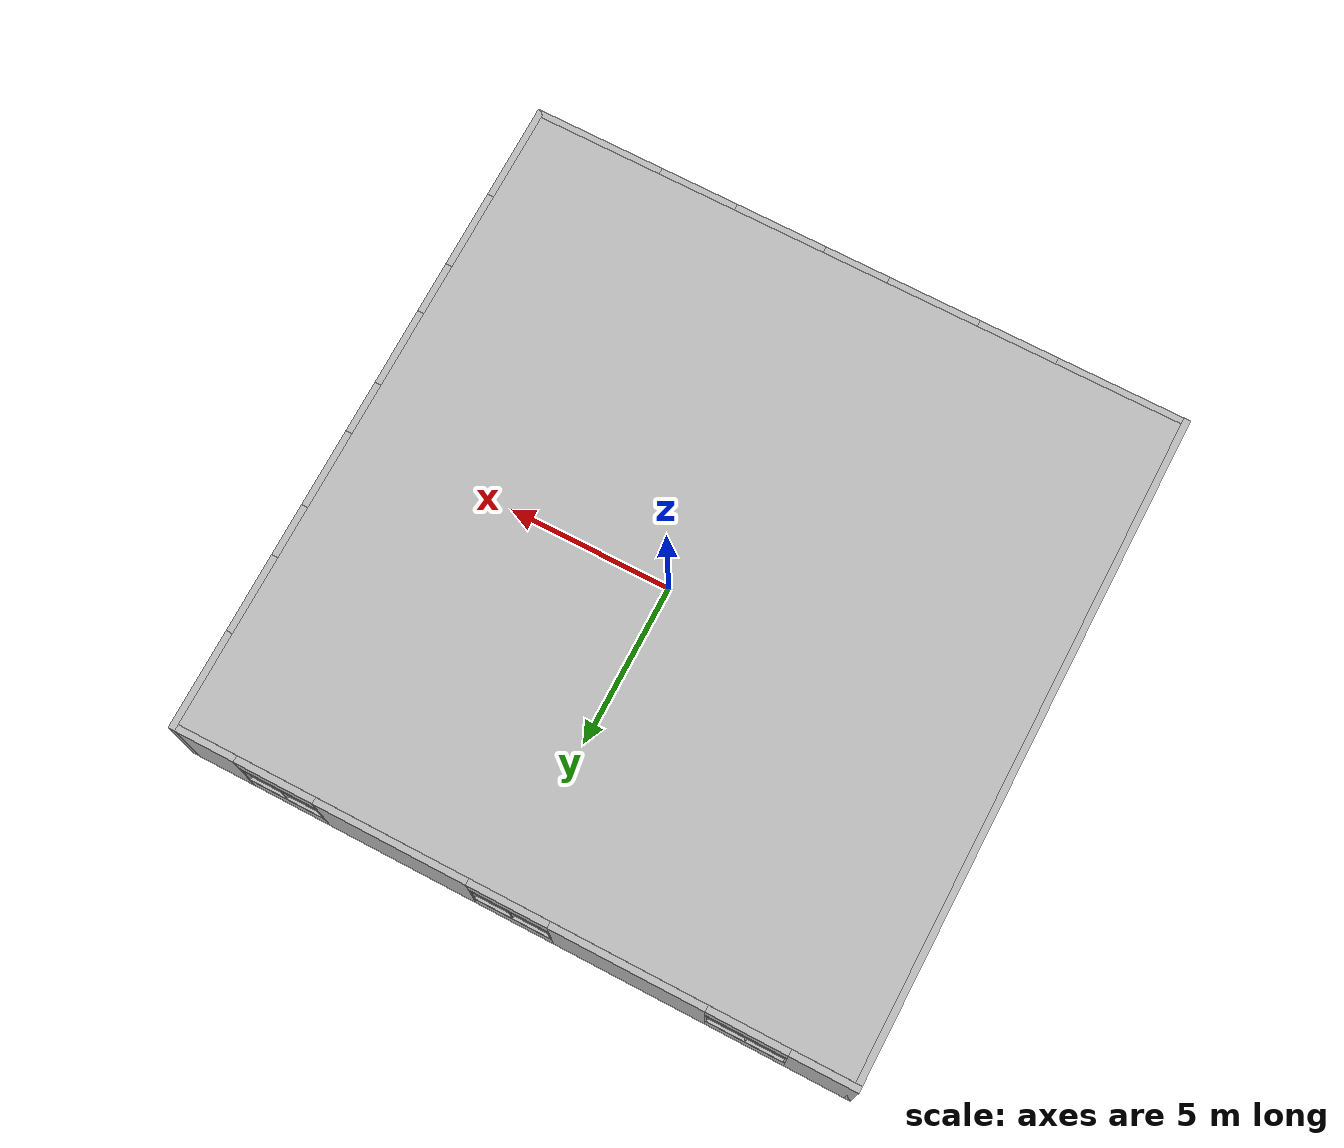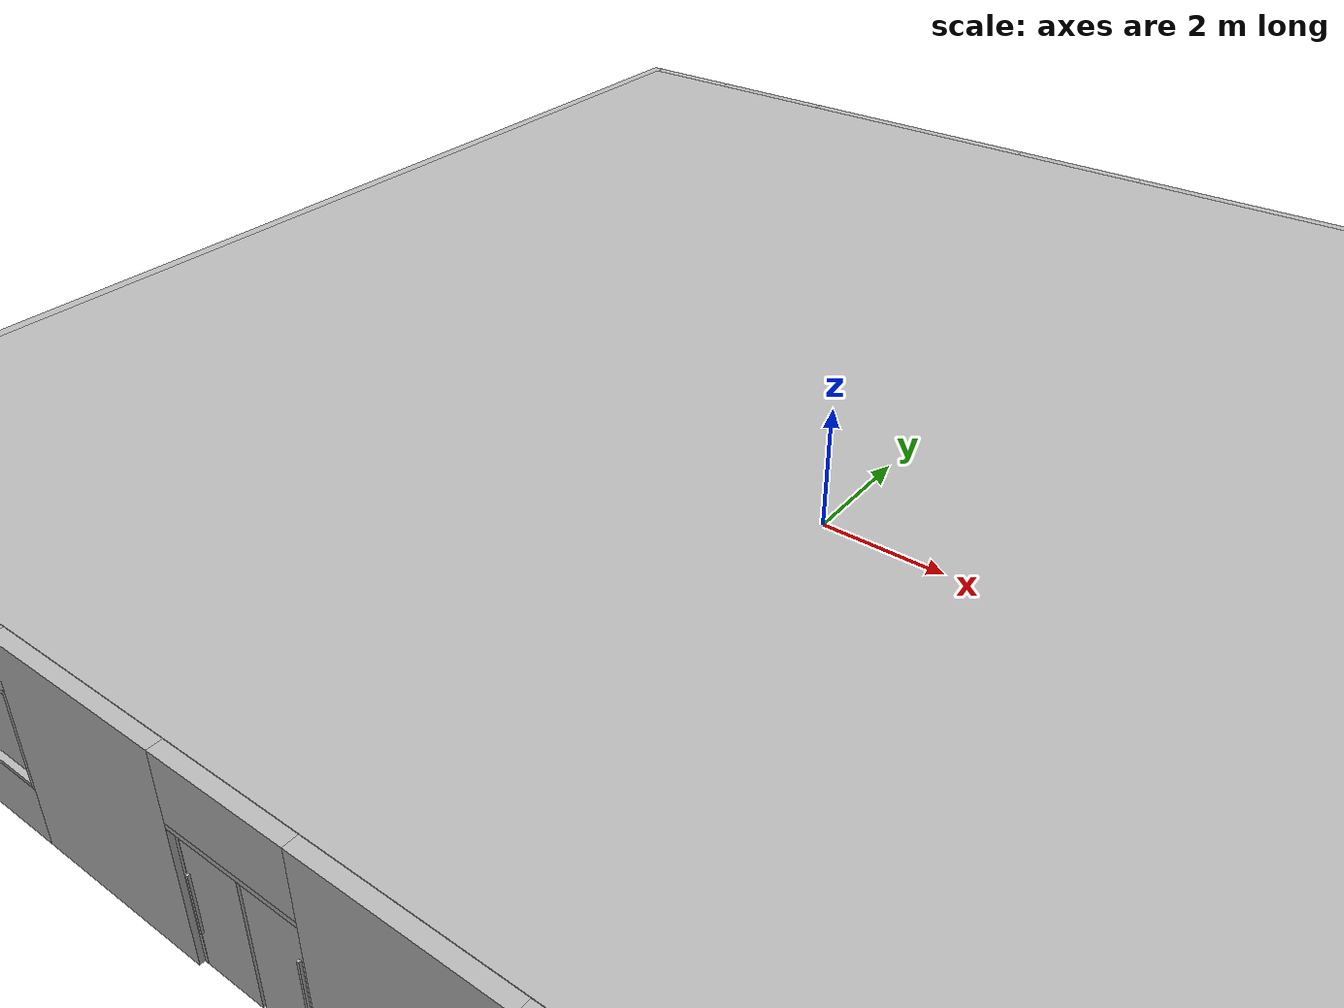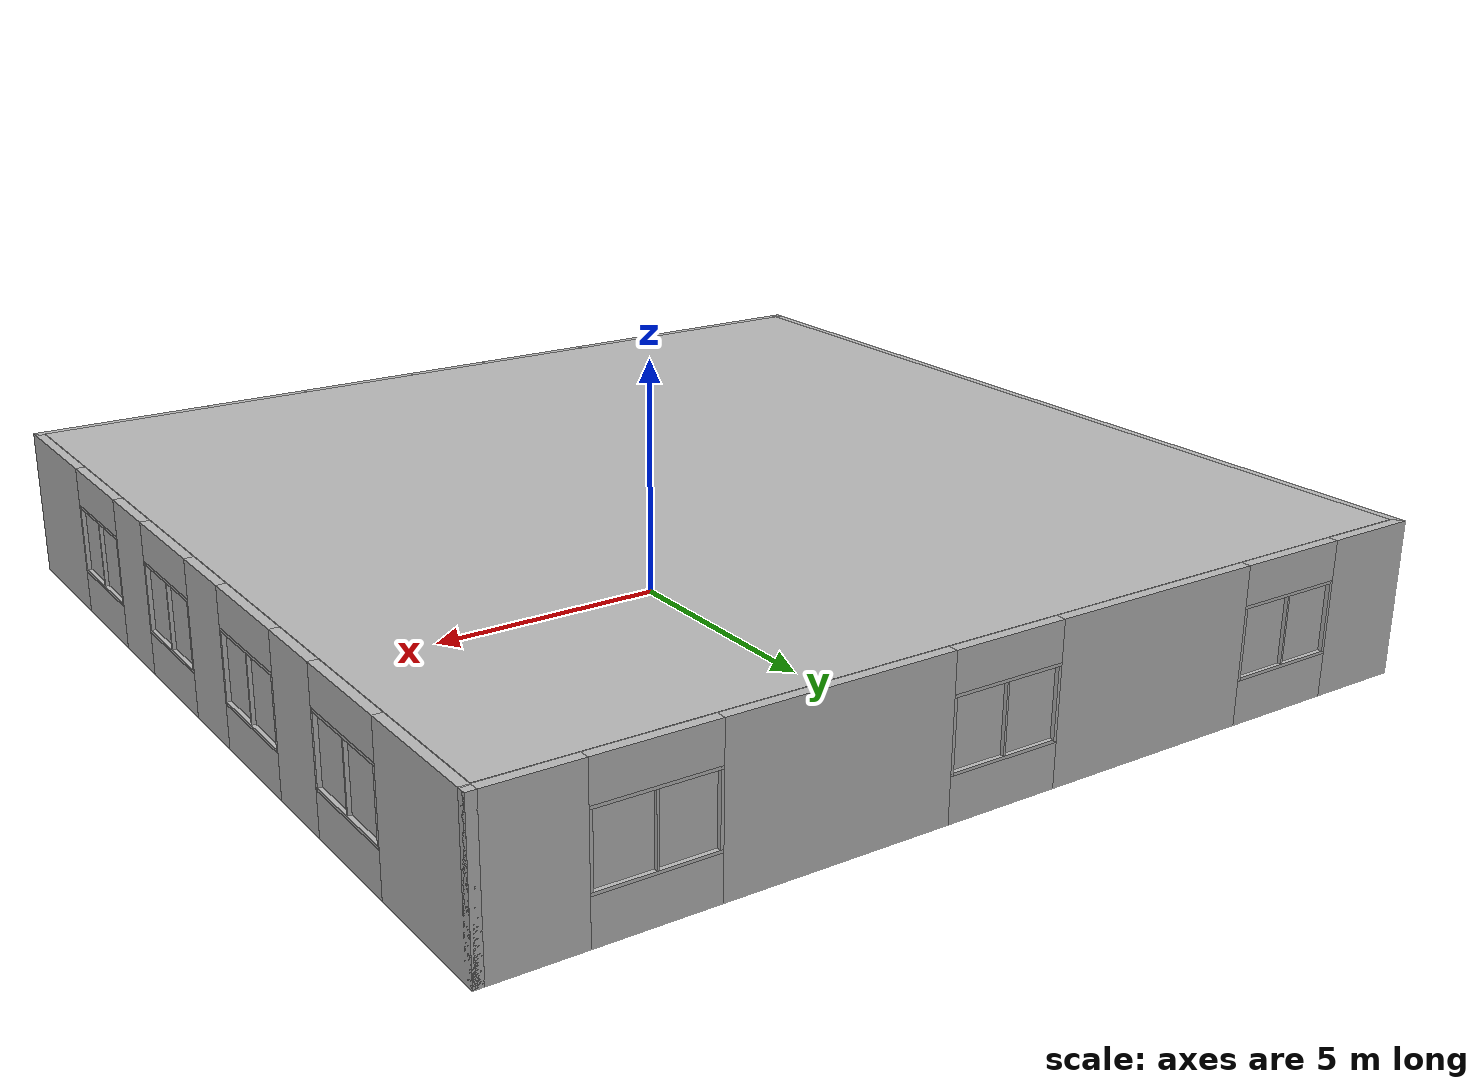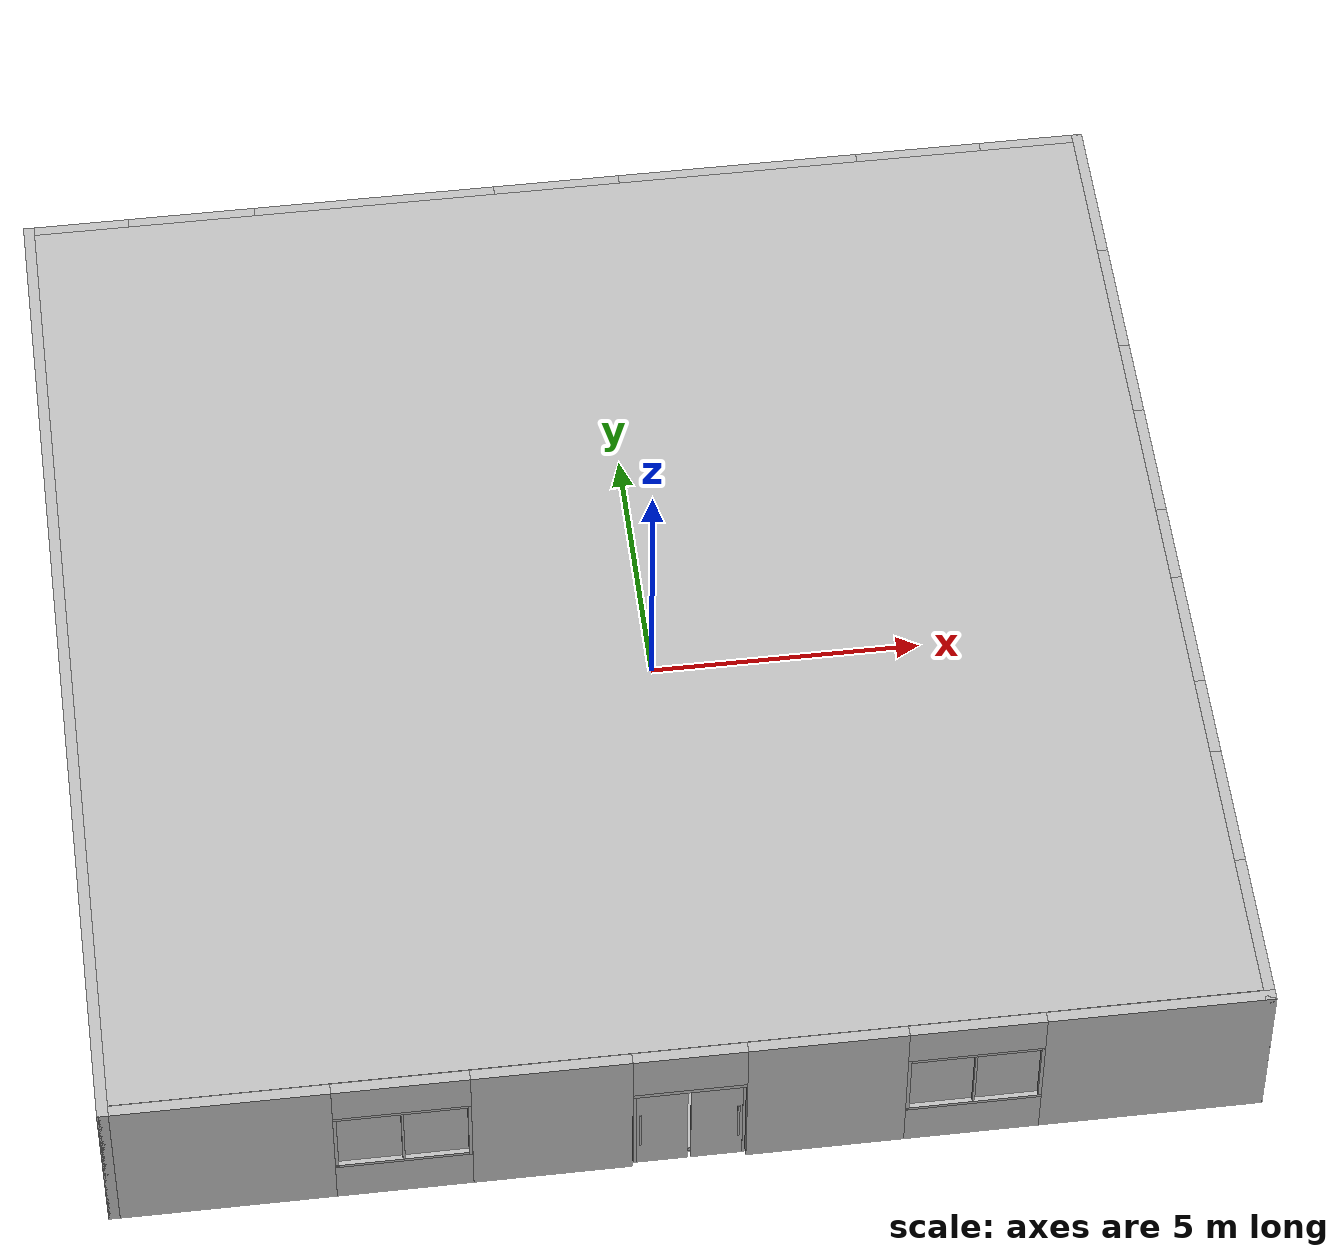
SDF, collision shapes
<?xml version="1.0" ?>
<sdf version="1.10">
  <model name="office_scene">
    <static>true</static>
    <link name="SchoolChair_01">
      <pose>1.55000 6.60000 0.00000 0.00000 0.00000 0.00000</pose>
      <!-- school chair | furniture | zone: break_area -->
      <visual name="SchoolChair_01_visual">
        <geometry><mesh>
          <uri>model://office_scene/meshes/SchoolChair_01.glb</uri>
        </mesh></geometry>
      </visual>
      <collision name="SchoolChair_01_c0">
        <pose>-0.60379 -0.08456 -0.24202 0.00000 -0.00000 -3.14159</pose>
        <geometry><box><size>0.5659 0.6753 1.0060</size></box></geometry>
      </collision>
    </link>
    <link name="baseball_01">
      <pose>-9.40000 6.05000 1.03000 0.00000 0.00000 0.00000</pose>
      <!-- baseball | toy | zone: private_office -->
      <visual name="baseball_01_visual">
        <geometry><mesh>
          <uri>model://office_scene/meshes/baseball_01.glb</uri>
        </mesh></geometry>
      </visual>
    </link>
    <link name="break_table">
      <pose>0.60000 6.60000 0.00000 0.00000 0.00000 0.00000</pose>
      <!-- round break-room table | furniture | zone: break_area -->
      <visual name="break_table_visual">
        <geometry><mesh>
          <uri>model://office_scene/meshes/break_table.glb</uri>
        </mesh></geometry>
      </visual>
      <collision name="break_table_c0">
        <pose>-0.60379 -0.08456 -0.40333 0.00000 -0.00000 0.00000</pose>
        <geometry><box><size>0.1200 0.1200 0.6800</size></box></geometry>
      </collision>
      <collision name="break_table_c1">
        <pose>-0.60379 -0.08456 -0.72833 0.00000 -0.00000 0.00000</pose>
        <geometry><box><size>0.6800 0.6800 0.0300</size></box></geometry>
      </collision>
      <collision name="break_table_c2">
        <pose>-0.60379 -0.08456 -0.02333 0.00000 -0.00000 0.00000</pose>
        <geometry><box><size>1.2000 1.2000 0.0400</size></box></geometry>
      </collision>
    </link>
    <link name="clock_west">
      <pose>-9.92000 -1.00000 2.35000 0.00000 0.00000 0.00000</pose>
      <!-- wall clock | decor | zone: open_plan -->
      <visual name="clock_west_visual">
        <geometry><mesh>
          <uri>model://office_scene/meshes/clock_west.glb</uri>
        </mesh></geometry>
      </visual>
      <collision name="clock_west_c0">
        <pose>-0.60379 -0.08456 -0.74333 1.57080 -0.00000 1.57080</pose>
        <geometry><box><size>0.3400 0.3400 0.0500</size></box></geometry>
      </collision>
      <collision name="clock_west_c1">
        <pose>-0.57379 -0.04456 -0.77333 1.57080 -0.00000 2.47080</pose>
        <geometry><box><size>0.0200 0.1400 0.0200</size></box></geometry>
      </collision>
    </link>
    <link name="coffee_machine">
      <pose>-3.00000 9.60000 0.90000 0.00000 0.00000 0.00000</pose>
      <!-- coffee machine | appliance | zone: break_area -->
      <visual name="coffee_machine_visual">
        <geometry><mesh>
          <uri>model://office_scene/meshes/coffee_machine.glb</uri>
        </mesh></geometry>
      </visual>
      <collision name="coffee_machine_c0">
        <pose>-0.60379 -0.08456 -0.53333 0.00000 -0.00000 0.00000</pose>
        <geometry><box><size>0.3000 0.3400 0.4200</size></box></geometry>
      </collision>
      <collision name="coffee_machine_c1">
        <pose>-0.60379 -0.24456 -0.66333 0.00000 -0.00000 0.00000</pose>
        <geometry><box><size>0.1400 0.1400 0.1600</size></box></geometry>
      </collision>
      <collision name="coffee_machine_c2">
        <pose>-0.60379 -0.24456 -0.67333 0.00000 -0.00000 0.00000</pose>
        <geometry><box><size>0.1400 0.1200 0.1000</size></box></geometry>
      </collision>
    </link>
    <link name="collab_table">
      <pose>2.60000 -4.70000 0.00000 0.00000 0.00000 0.00000</pose>
      <!-- standing collaboration table | furniture | zone: open_plan -->
      <visual name="collab_table_visual">
        <geometry><mesh>
          <uri>model://office_scene/meshes/collab_table.glb</uri>
        </mesh></geometry>
      </visual>
      <collision name="collab_table_c0">
        <pose>-0.60379 -0.08456 -0.23333 0.00000 -0.00000 0.00000</pose>
        <geometry><box><size>0.1100 0.1100 1.0000</size></box></geometry>
      </collision>
      <collision name="collab_table_c1">
        <pose>-0.60379 -0.08456 -0.72833 0.00000 -0.00000 0.00000</pose>
        <geometry><box><size>0.6800 0.6800 0.0300</size></box></geometry>
      </collision>
      <collision name="collab_table_c2">
        <pose>-0.60379 -0.08456 0.28667 0.00000 -0.00000 0.00000</pose>
        <geometry><box><size>1.0400 1.0400 0.0450</size></box></geometry>
      </collision>
    </link>
    <link name="cone_orange">
      <pose>3.60000 -0.60000 0.26000 0.00000 0.00000 0.00000</pose>
      <!-- orange traffic cone | cone | zone: open_plan -->
      <visual name="cone_orange_visual">
        <geometry><mesh>
          <uri>model://office_scene/meshes/cone_orange.glb</uri>
        </mesh></geometry>
      </visual>
      <collision name="cone_orange_c0">
        <pose>-0.60379 -0.08456 -0.72333 0.00000 -0.00000 0.00000</pose>
        <geometry><box><size>0.3800 0.3800 0.5200</size></box></geometry>
      </collision>
    </link>
    <link name="cone_red">
      <pose>3.60000 -1.70000 0.26000 0.00000 0.00000 0.00000</pose>
      <!-- red traffic cone | cone | zone: open_plan -->
      <visual name="cone_red_visual">
        <geometry><mesh>
          <uri>model://office_scene/meshes/cone_red.glb</uri>
        </mesh></geometry>
      </visual>
      <collision name="cone_red_c0">
        <pose>-0.60379 -0.08456 -0.72333 0.00000 -0.00000 0.00000</pose>
        <geometry><box><size>0.3800 0.3800 0.5200</size></box></geometry>
      </collision>
    </link>
    <link name="cone_white">
      <pose>0.80000 -5.60000 0.26000 0.00000 0.00000 0.00000</pose>
      <!-- white traffic cone | cone | zone: open_plan -->
      <visual name="cone_white_visual">
        <geometry><mesh>
          <uri>model://office_scene/meshes/cone_white.glb</uri>
        </mesh></geometry>
      </visual>
      <collision name="cone_white_c0">
        <pose>-0.60379 -0.08456 -0.72333 0.00000 -0.00000 0.00000</pose>
        <geometry><box><size>0.3800 0.3800 0.5200</size></box></geometry>
      </collision>
    </link>
    <link name="cone_yellow">
      <pose>-3.40000 2.20000 0.26000 0.00000 0.00000 0.00000</pose>
      <!-- yellow traffic cone | cone | zone: open_plan -->
      <visual name="cone_yellow_visual">
        <geometry><mesh>
          <uri>model://office_scene/meshes/cone_yellow.glb</uri>
        </mesh></geometry>
      </visual>
      <collision name="cone_yellow_c0">
        <pose>-0.60379 -0.08456 -0.72333 0.00000 -0.00000 0.00000</pose>
        <geometry><box><size>0.3800 0.3800 0.5200</size></box></geometry>
      </collision>
    </link>
    <link name="conference_credenza">
      <pose>3.60000 8.60000 0.00000 0.00000 0.00000 0.00000</pose>
      <!-- credenza cabinet | furniture | zone: conference_room -->
      <visual name="conference_credenza_visual">
        <geometry><mesh>
          <uri>model://office_scene/meshes/conference_credenza.glb</uri>
        </mesh></geometry>
      </visual>
      <collision name="conference_credenza_c0">
        <pose>-0.60379 -0.08456 -0.36833 0.00000 -0.00000 1.57080</pose>
        <geometry><box><size>1.6000 0.4500 0.7500</size></box></geometry>
      </collision>
      <collision name="conference_credenza_c1">
        <pose>-0.37379 -0.08456 -0.55583 0.00000 -0.00000 1.57080</pose>
        <geometry><box><size>1.5500 0.0200 0.3450</size></box></geometry>
      </collision>
      <collision name="conference_credenza_c2">
        <pose>-0.37379 -0.08456 -0.18083 0.00000 -0.00000 1.57080</pose>
        <geometry><box><size>1.5500 0.0200 0.3450</size></box></geometry>
      </collision>
      <collision name="conference_credenza_c3">
        <pose>-0.35379 -0.08456 -0.45083 0.00000 -0.00000 1.57080</pose>
        <geometry><box><size>0.2200 0.0250 0.0200</size></box></geometry>
      </collision>
      <collision name="conference_credenza_c4">
        <pose>-0.35379 -0.08456 -0.07583 0.00000 -0.00000 1.57080</pose>
        <geometry><box><size>0.2200 0.0250 0.0200</size></box></geometry>
      </collision>
    </link>
    <link name="conference_screen">
      <pose>8.60000 9.92000 1.70000 0.00000 0.00000 0.00000</pose>
      <!-- wall-mounted display screen | appliance | zone: conference_room -->
      <visual name="conference_screen_visual">
        <geometry><mesh>
          <uri>model://office_scene/meshes/conference_screen.glb</uri>
        </mesh></geometry>
      </visual>
      <collision name="conference_screen_c0">
        <pose>-0.60379 -0.08456 -0.74333 0.00000 -0.00000 0.00000</pose>
        <geometry><box><size>1.6000 0.0600 0.9200</size></box></geometry>
      </collision>
      <collision name="conference_screen_c1">
        <pose>-0.60379 -0.11956 -0.74333 0.00000 -0.00000 0.00000</pose>
        <geometry><box><size>1.5600 0.0200 0.8800</size></box></geometry>
      </collision>
    </link>
    <link name="conference_table">
      <pose>6.50000 6.40000 0.00000 0.00000 0.00000 0.00000</pose>
      <!-- conference table | furniture | zone: conference_room -->
      <visual name="conference_table_visual">
        <geometry><mesh>
          <uri>model://office_scene/meshes/conference_table.glb</uri>
        </mesh></geometry>
      </visual>
      <collision name="conference_table_c0">
        <pose>-0.60379 -0.08456 -0.29333 0.00000 -0.00000 0.00000</pose>
        <geometry><box><size>2.0000 0.1000 0.1000</size></box></geometry>
      </collision>
      <collision name="conference_table_c1">
        <pose>-1.70379 -0.08456 -0.71833 0.00000 -0.00000 0.00000</pose>
        <geometry><box><size>0.6000 1.0500 0.0500</size></box></geometry>
      </collision>
      <collision name="conference_table_c2">
        <pose>0.49621 -0.08456 -0.71833 0.00000 -0.00000 0.00000</pose>
        <geometry><box><size>0.6000 1.0500 0.0500</size></box></geometry>
      </collision>
      <collision name="conference_table_c3">
        <pose>-1.70379 -0.08456 -0.41333 0.00000 -0.00000 0.00000</pose>
        <geometry><box><size>0.1200 0.9000 0.6600</size></box></geometry>
      </collision>
      <collision name="conference_table_c4">
        <pose>0.49621 -0.08456 -0.41333 0.00000 -0.00000 0.00000</pose>
        <geometry><box><size>0.1200 0.9000 0.6600</size></box></geometry>
      </collision>
      <collision name="conference_table_c5">
        <pose>-0.60379 -0.08456 -0.01833 0.00000 -0.00000 0.00000</pose>
        <geometry><box><size>3.4000 1.4000 0.0500</size></box></geometry>
      </collision>
    </link>
    <link name="cube_blue_glossy">
      <pose>6.60000 -7.20000 0.20000 0.00000 0.00000 0.00000</pose>
      <!-- glossy blue cube | cube | zone: open_plan -->
      <visual name="cube_blue_glossy_visual">
        <geometry><mesh>
          <uri>model://office_scene/meshes/cube_blue_glossy.glb</uri>
        </mesh></geometry>
      </visual>
      <collision name="cube_blue_glossy_c0">
        <pose>-0.60379 -0.08456 -0.74333 0.00000 -0.00000 0.05937</pose>
        <geometry><box><size>0.4000 0.4000 0.4000</size></box></geometry>
      </collision>
    </link>
    <link name="cube_checker_green">
      <pose>-3.60000 -7.60000 0.20000 0.00000 0.00000 0.00000</pose>
      <!-- green checkered cube | cube | zone: reception -->
      <visual name="cube_checker_green_visual">
        <geometry><mesh>
          <uri>model://office_scene/meshes/cube_checker_green.glb</uri>
        </mesh></geometry>
      </visual>
      <collision name="cube_checker_green_c0">
        <pose>-0.60379 -0.08456 -0.74333 0.00000 -0.00000 0.86349</pose>
        <geometry><box><size>0.4000 0.4000 0.4000</size></box></geometry>
      </collision>
    </link>
    <link name="cube_marble_orange">
      <pose>1.40000 3.60000 0.20000 0.00000 0.00000 0.00000</pose>
      <!-- orange marbled cube | cube | zone: open_plan -->
      <visual name="cube_marble_orange_visual">
        <geometry><mesh>
          <uri>model://office_scene/meshes/cube_marble_orange.glb</uri>
        </mesh></geometry>
      </visual>
      <collision name="cube_marble_orange_c0">
        <pose>-0.60379 -0.08456 -0.74333 0.00000 -0.00000 0.54103</pose>
        <geometry><box><size>0.4000 0.4000 0.4000</size></box></geometry>
      </collision>
    </link>
    <link name="cube_red">
      <pose>2.20000 -6.40000 0.20000 0.00000 0.00000 0.00000</pose>
      <!-- red cube | cube | zone: reception -->
      <visual name="cube_red_visual">
        <geometry><mesh>
          <uri>model://office_scene/meshes/cube_red.glb</uri>
        </mesh></geometry>
      </visual>
      <collision name="cube_red_c0">
        <pose>-0.60379 -0.08456 -0.74333 0.00000 -0.00000 0.65907</pose>
        <geometry><box><size>0.4000 0.4000 0.4000</size></box></geometry>
      </collision>
    </link>
    <link name="cube_stripe_purple">
      <pose>8.60000 4.60000 0.20000 0.00000 0.00000 0.00000</pose>
      <!-- purple striped cube | cube | zone: conference_room -->
      <visual name="cube_stripe_purple_visual">
        <geometry><mesh>
          <uri>model://office_scene/meshes/cube_stripe_purple.glb</uri>
        </mesh></geometry>
      </visual>
      <collision name="cube_stripe_purple_c0">
        <pose>-0.60379 -0.08456 -0.74333 0.00000 -0.00000 0.90320</pose>
        <geometry><box><size>0.4000 0.4000 0.4000</size></box></geometry>
      </collision>
    </link>
    <link name="cube_wood_yellow">
      <pose>-8.30000 -8.60000 0.20000 0.00000 0.00000 0.00000</pose>
      <!-- wooden cube | cube | zone: open_plan -->
      <visual name="cube_wood_yellow_visual">
        <geometry><mesh>
          <uri>model://office_scene/meshes/cube_wood_yellow.glb</uri>
        </mesh></geometry>
      </visual>
      <collision name="cube_wood_yellow_c0">
        <pose>-0.60379 -0.08456 -0.74333 0.00000 -0.00000 0.87882</pose>
        <geometry><box><size>0.4000 0.4000 0.4000</size></box></geometry>
      </collision>
    </link>
    <link name="filing_cabinet_1">
      <pose>-9.55000 -5.35000 0.00000 0.00000 0.00000 0.00000</pose>
      <!-- filing cabinets | furniture | zone: open_plan -->
      <visual name="filing_cabinet_1_visual">
        <geometry><mesh>
          <uri>model://office_scene/meshes/filing_cabinet_1.glb</uri>
        </mesh></geometry>
      </visual>
      <collision name="filing_cabinet_1_c0">
        <pose>-0.60379 -0.08456 -0.21833 0.00000 -0.00000 1.57080</pose>
        <geometry><box><size>0.8000 0.4500 1.0500</size></box></geometry>
      </collision>
      <collision name="filing_cabinet_1_c1">
        <pose>-0.37379 -0.08456 -0.56833 0.00000 -0.00000 1.57080</pose>
        <geometry><box><size>0.7500 0.0200 0.3200</size></box></geometry>
      </collision>
      <collision name="filing_cabinet_1_c2">
        <pose>-0.37379 -0.08456 -0.21833 0.00000 -0.00000 1.57080</pose>
        <geometry><box><size>0.7500 0.0200 0.3200</size></box></geometry>
      </collision>
      <collision name="filing_cabinet_1_c3">
        <pose>-0.37379 -0.08456 0.13167 0.00000 -0.00000 1.57080</pose>
        <geometry><box><size>0.7500 0.0200 0.3200</size></box></geometry>
      </collision>
      <collision name="filing_cabinet_1_c4">
        <pose>-0.35379 -0.08456 -0.47033 0.00000 -0.00000 1.57080</pose>
        <geometry><box><size>0.2200 0.0250 0.0200</size></box></geometry>
      </collision>
      <collision name="filing_cabinet_1_c5">
        <pose>-0.35379 -0.08456 -0.12033 0.00000 -0.00000 1.57080</pose>
        <geometry><box><size>0.2200 0.0250 0.0200</size></box></geometry>
      </collision>
      <collision name="filing_cabinet_1_c6">
        <pose>-0.35379 -0.08456 0.22967 0.00000 -0.00000 1.57080</pose>
        <geometry><box><size>0.2200 0.0250 0.0200</size></box></geometry>
      </collision>
    </link>
    <link name="floor_lamp">
      <pose>8.80000 -3.40000 0.00000 0.00000 0.00000 0.00000</pose>
      <!-- floor lamp | appliance | zone: lounge -->
      <visual name="floor_lamp_visual">
        <geometry><mesh>
          <uri>model://office_scene/meshes/floor_lamp.glb</uri>
        </mesh></geometry>
      </visual>
      <collision name="floor_lamp_c0">
        <pose>-0.60379 -0.08456 -0.72833 0.00000 -0.00000 0.00000</pose>
        <geometry><box><size>0.3200 0.3200 0.0300</size></box></geometry>
      </collision>
      <collision name="floor_lamp_c1">
        <pose>-0.60379 -0.08456 0.87667 -3.14159 -0.00000 0.00000</pose>
        <geometry><box><size>0.4000 0.4000 0.2600</size></box></geometry>
      </collision>
      <collision name="floor_lamp_c2">
        <pose>-0.60379 -0.08456 0.04667 0.00000 -0.00000 0.00000</pose>
        <geometry><box><size>0.0360 0.0360 1.5500</size></box></geometry>
      </collision>
    </link>
    <link name="furniture_misc">
      <pose>0.00000 0.00000 0.00000 0.00000 0.00000 0.00000</pose>
      <visual name="furniture_misc_visual">
        <geometry><mesh>
          <uri>model://office_scene/meshes/furniture_misc.glb</uri>
        </mesh></geometry>
      </visual>
      <collision name="furniture_misc_c0">
        <pose>-2.60379 -10.02456 1.10667 0.00000 -0.00000 0.00000</pose>
        <geometry><box><size>1.2000 0.0200 0.8000</size></box></geometry>
      </collision>
      <collision name="furniture_misc_c1">
        <pose>-2.60379 -10.00456 1.10667 0.00000 -0.00000 0.00000</pose>
        <geometry><box><size>1.2500 0.0400 0.8500</size></box></geometry>
      </collision>
      <collision name="furniture_misc_c2">
        <pose>-10.50379 2.91544 1.05667 0.00000 -0.00000 1.57080</pose>
        <geometry><box><size>0.9000 0.0200 1.2000</size></box></geometry>
      </collision>
      <collision name="furniture_misc_c3">
        <pose>-10.52379 2.91544 1.05667 0.00000 -0.00000 1.57080</pose>
        <geometry><box><size>0.9500 0.0400 1.2500</size></box></geometry>
      </collision>
      <collision name="furniture_misc_c4">
        <pose>-9.90379 -8.68456 -0.53333 0.00000 -0.00000 0.00000</pose>
        <geometry><box><size>0.3400 0.3400 0.4200</size></box></geometry>
      </collision>
      <collision name="furniture_misc_c5">
        <pose>-9.90379 -8.68456 -0.32333 0.00000 -0.00000 0.00000</pose>
        <geometry><box><size>0.3600 0.3600 0.0300</size></box></geometry>
      </collision>
      <collision name="furniture_misc_c6">
        <pose>2.91621 7.96544 0.16167 0.00000 0.05105 1.57080</pose>
        <geometry><box><size>0.0550 0.2600 0.3100</size></box></geometry>
      </collision>
      <collision name="furniture_misc_c7">
        <pose>2.91621 8.03044 0.16167 0.00000 0.04251 1.57080</pose>
        <geometry><box><size>0.0550 0.2600 0.3100</size></box></geometry>
      </collision>
      <collision name="furniture_misc_c8">
        <pose>2.91621 8.09544 0.16167 0.00000 -0.04779 1.57080</pose>
        <geometry><box><size>0.0550 0.2600 0.3100</size></box></geometry>
      </collision>
      <collision name="furniture_misc_c9">
        <pose>2.91621 8.16044 0.16167 0.00000 -0.02573 1.57080</pose>
        <geometry><box><size>0.0550 0.2600 0.3100</size></box></geometry>
      </collision>
      <collision name="furniture_misc_c10">
        <pose>2.91621 8.22544 0.16167 0.00000 -0.03008 1.57080</pose>
        <geometry><box><size>0.0550 0.2600 0.3100</size></box></geometry>
      </collision>
      <collision name="furniture_misc_c11">
        <pose>2.91621 8.29044 0.16167 0.00000 -0.00765 1.57080</pose>
        <geometry><box><size>0.0550 0.2600 0.3100</size></box></geometry>
      </collision>
      <collision name="furniture_misc_c12">
        <pose>2.91621 8.35544 0.16167 0.00000 -0.03722 1.57080</pose>
        <geometry><box><size>0.0550 0.2600 0.3100</size></box></geometry>
      </collision>
      <collision name="furniture_misc_c13">
        <pose>5.39621 -1.68456 -0.31461 0.00000 -0.00000 0.20944</pose>
        <geometry><box><size>0.5532 0.5532 0.0200</size></box></geometry>
      </collision>
      <collision name="furniture_misc_c14">
        <pose>5.74621 -2.03456 -0.30533 0.00000 -0.00000 0.14257</pose>
        <geometry><box><size>0.2100 0.2800 0.0350</size></box></geometry>
      </collision>
      <collision name="furniture_misc_c15">
        <pose>5.74621 -2.03456 -0.26933 0.00000 -0.00000 0.19213</pose>
        <geometry><box><size>0.2100 0.2800 0.0350</size></box></geometry>
      </collision>
      <collision name="furniture_misc_c16">
        <pose>5.74621 -2.03456 -0.23333 0.00000 -0.00000 -0.04998</pose>
        <geometry><box><size>0.2100 0.2800 0.0350</size></box></geometry>
      </collision>
      <collision name="furniture_misc_c17">
        <pose>-10.15379 -6.28456 -0.21833 0.00000 -0.00000 1.57080</pose>
        <geometry><box><size>0.8000 0.4500 1.0500</size></box></geometry>
      </collision>
      <collision name="furniture_misc_c18">
        <pose>-9.92379 -6.28456 -0.56833 0.00000 -0.00000 1.57080</pose>
        <geometry><box><size>0.7500 0.0200 0.3200</size></box></geometry>
      </collision>
      <collision name="furniture_misc_c19">
        <pose>-9.92379 -6.28456 -0.21833 0.00000 -0.00000 1.57080</pose>
        <geometry><box><size>0.7500 0.0200 0.3200</size></box></geometry>
      </collision>
      <collision name="furniture_misc_c20">
        <pose>-9.92379 -6.28456 0.13167 0.00000 -0.00000 1.57080</pose>
        <geometry><box><size>0.7500 0.0200 0.3200</size></box></geometry>
      </collision>
      <collision name="furniture_misc_c21">
        <pose>-9.90379 -6.28456 -0.47033 0.00000 -0.00000 1.57080</pose>
        <geometry><box><size>0.2200 0.0250 0.0200</size></box></geometry>
      </collision>
      <collision name="furniture_misc_c22">
        <pose>-9.90379 -6.28456 -0.12033 0.00000 -0.00000 1.57080</pose>
        <geometry><box><size>0.2200 0.0250 0.0200</size></box></geometry>
      </collision>
      <collision name="furniture_misc_c23">
        <pose>-9.90379 -6.28456 0.22967 0.00000 -0.00000 1.57080</pose>
        <geometry><box><size>0.2200 0.0250 0.0200</size></box></geometry>
      </collision>
      <collision name="furniture_misc_c24">
        <pose>-10.15379 -4.58456 -0.21833 0.00000 -0.00000 1.57080</pose>
        <geometry><box><size>0.8000 0.4500 1.0500</size></box></geometry>
      </collision>
      <collision name="furniture_misc_c25">
        <pose>-9.92379 -4.58456 -0.56833 0.00000 -0.00000 1.57080</pose>
        <geometry><box><size>0.7500 0.0200 0.3200</size></box></geometry>
      </collision>
      <collision name="furniture_misc_c26">
        <pose>-9.92379 -4.58456 -0.21833 0.00000 -0.00000 1.57080</pose>
        <geometry><box><size>0.7500 0.0200 0.3200</size></box></geometry>
      </collision>
      <collision name="furniture_misc_c27">
        <pose>-9.92379 -4.58456 0.13167 0.00000 -0.00000 1.57080</pose>
        <geometry><box><size>0.7500 0.0200 0.3200</size></box></geometry>
      </collision>
      <collision name="furniture_misc_c28">
        <pose>-9.90379 -4.58456 -0.47033 0.00000 -0.00000 1.57080</pose>
        <geometry><box><size>0.2200 0.0250 0.0200</size></box></geometry>
      </collision>
      <collision name="furniture_misc_c29">
        <pose>-9.90379 -4.58456 -0.12033 0.00000 -0.00000 1.57080</pose>
        <geometry><box><size>0.2200 0.0250 0.0200</size></box></geometry>
      </collision>
      <collision name="furniture_misc_c30">
        <pose>-9.90379 -4.58456 0.22967 0.00000 -0.00000 1.57080</pose>
        <geometry><box><size>0.2200 0.0250 0.0200</size></box></geometry>
      </collision>
      <collision name="furniture_misc_c31">
        <pose>2.99621 -0.68456 -0.72533 0.00000 -0.00000 0.00000</pose>
        <geometry><box><size>0.4400 0.4400 0.0350</size></box></geometry>
      </collision>
      <collision name="furniture_misc_c32">
        <pose>2.99621 -1.78456 -0.72533 0.00000 -0.00000 0.00000</pose>
        <geometry><box><size>0.4400 0.4400 0.0350</size></box></geometry>
      </collision>
      <collision name="furniture_misc_c33">
        <pose>0.19621 -5.68456 -0.72533 0.00000 -0.00000 0.00000</pose>
        <geometry><box><size>0.4400 0.4400 0.0350</size></box></geometry>
      </collision>
      <collision name="furniture_misc_c34">
        <pose>-4.00379 2.11544 -0.72533 0.00000 -0.00000 0.00000</pose>
        <geometry><box><size>0.4400 0.4400 0.0350</size></box></geometry>
      </collision>
      <collision name="furniture_misc_c35">
        <pose>8.16621 6.57544 -0.07333 0.00000 -0.00000 -1.57080</pose>
        <geometry><box><size>0.0500 0.3200 0.0400</size></box></geometry>
      </collision>
      <collision name="furniture_misc_c36">
        <pose>8.16621 6.05544 -0.07333 0.00000 -0.00000 -1.57080</pose>
        <geometry><box><size>0.0500 0.3200 0.0400</size></box></geometry>
      </collision>
      <collision name="furniture_misc_c37">
        <pose>8.24621 6.57544 -0.16333 0.00000 -0.00000 -1.57080</pose>
        <geometry><box><size>0.0400 0.0500 0.1600</size></box></geometry>
      </collision>
      <collision name="furniture_misc_c38">
        <pose>8.24621 6.05544 -0.16333 0.00000 -0.00000 -1.57080</pose>
        <geometry><box><size>0.0400 0.0500 0.1600</size></box></geometry>
      </collision>
      <collision name="furniture_misc_c39">
        <pose>8.38121 6.31544 0.04667 -0.13963 -0.00000 -1.57080</pose>
        <geometry><box><size>0.4500 0.0700 0.5200</size></box></geometry>
      </collision>
      <collision name="furniture_misc_c40">
        <pose>8.36621 6.31544 -0.22333 0.00000 -0.00000 -1.57080</pose>
        <geometry><box><size>0.0700 0.0600 0.1800</size></box></geometry>
      </collision>
      <collision name="furniture_misc_c41">
        <pose>8.14621 6.31544 -0.47333 0.00000 -0.00000 0.00000</pose>
        <geometry><box><size>0.0700 0.0700 0.2800</size></box></geometry>
      </collision>
      <collision name="furniture_misc_c42">
        <pose>8.14621 6.31544 -0.28333 0.00000 -0.00000 -1.57080</pose>
        <geometry><box><size>0.4800 0.4700 0.0900</size></box></geometry>
      </collision>
      <collision name="furniture_misc_c43">
        <pose>8.14621 6.16544 -0.67333 0.00000 -0.00000 -1.57080</pose>
        <geometry><box><size>0.3000 0.0450 0.0350</size></box></geometry>
      </collision>
      <collision name="furniture_misc_c44">
        <pose>8.28887 6.26908 -0.67333 0.00000 -0.00000 -0.31416</pose>
        <geometry><box><size>0.3000 0.0450 0.0350</size></box></geometry>
      </collision>
      <collision name="furniture_misc_c45">
        <pose>8.23438 6.43679 -0.67333 0.00000 -0.00000 0.94248</pose>
        <geometry><box><size>0.3000 0.0450 0.0350</size></box></geometry>
      </collision>
      <collision name="furniture_misc_c46">
        <pose>8.05804 6.43679 -0.67333 0.00000 -0.00000 2.19911</pose>
        <geometry><box><size>0.3000 0.0450 0.0350</size></box></geometry>
      </collision>
      <collision name="furniture_misc_c47">
        <pose>8.00355 6.26908 -0.67333 0.00000 -0.00000 -2.82743</pose>
        <geometry><box><size>0.3000 0.0450 0.0350</size></box></geometry>
      </collision>
      <collision name="furniture_misc_c48">
        <pose>4.48621 7.53544 -0.07333 0.00000 -0.00000 0.00000</pose>
        <geometry><box><size>0.0500 0.3200 0.0400</size></box></geometry>
      </collision>
      <collision name="furniture_misc_c49">
        <pose>5.00621 7.53544 -0.07333 0.00000 -0.00000 0.00000</pose>
        <geometry><box><size>0.0500 0.3200 0.0400</size></box></geometry>
      </collision>
      <collision name="furniture_misc_c50">
        <pose>4.48621 7.61544 -0.16333 0.00000 -0.00000 0.00000</pose>
        <geometry><box><size>0.0400 0.0500 0.1600</size></box></geometry>
      </collision>
      <collision name="furniture_misc_c51">
        <pose>5.00621 7.61544 -0.16333 0.00000 -0.00000 0.00000</pose>
        <geometry><box><size>0.0400 0.0500 0.1600</size></box></geometry>
      </collision>
      <collision name="furniture_misc_c52">
        <pose>4.74621 7.75044 0.04667 -0.13963 -0.00000 0.00000</pose>
        <geometry><box><size>0.4500 0.0700 0.5200</size></box></geometry>
      </collision>
      <collision name="furniture_misc_c53">
        <pose>4.74621 7.73544 -0.22333 0.00000 -0.00000 0.00000</pose>
        <geometry><box><size>0.0700 0.0600 0.1800</size></box></geometry>
      </collision>
      <collision name="furniture_misc_c54">
        <pose>4.74621 7.51544 -0.47333 0.00000 -0.00000 0.00000</pose>
        <geometry><box><size>0.0700 0.0700 0.2800</size></box></geometry>
      </collision>
      <collision name="furniture_misc_c55">
        <pose>4.74621 7.51544 -0.28333 0.00000 -0.00000 0.00000</pose>
        <geometry><box><size>0.4800 0.4700 0.0900</size></box></geometry>
      </collision>
      <collision name="furniture_misc_c56">
        <pose>4.89621 7.51544 -0.67333 0.00000 -0.00000 0.00000</pose>
        <geometry><box><size>0.3000 0.0450 0.0350</size></box></geometry>
      </collision>
      <collision name="furniture_misc_c57">
        <pose>4.79256 7.65810 -0.67333 0.00000 -0.00000 1.25664</pose>
        <geometry><box><size>0.3000 0.0450 0.0350</size></box></geometry>
      </collision>
      <collision name="furniture_misc_c58">
        <pose>4.62486 7.60360 -0.67333 0.00000 -0.00000 2.51327</pose>
        <geometry><box><size>0.3000 0.0450 0.0350</size></box></geometry>
      </collision>
      <collision name="furniture_misc_c59">
        <pose>4.62486 7.42727 -0.67333 0.00000 -0.00000 -2.51327</pose>
        <geometry><box><size>0.3000 0.0450 0.0350</size></box></geometry>
      </collision>
      <collision name="furniture_misc_c60">
        <pose>4.79256 7.37278 -0.67333 0.00000 -0.00000 -1.25664</pose>
        <geometry><box><size>0.3000 0.0450 0.0350</size></box></geometry>
      </collision>
      <collision name="furniture_misc_c61">
        <pose>5.63621 7.53544 -0.07333 0.00000 -0.00000 0.00000</pose>
        <geometry><box><size>0.0500 0.3200 0.0400</size></box></geometry>
      </collision>
      <collision name="furniture_misc_c62">
        <pose>6.15621 7.53544 -0.07333 0.00000 -0.00000 0.00000</pose>
        <geometry><box><size>0.0500 0.3200 0.0400</size></box></geometry>
      </collision>
      <collision name="furniture_misc_c63">
        <pose>5.63621 7.61544 -0.16333 0.00000 -0.00000 0.00000</pose>
        <geometry><box><size>0.0400 0.0500 0.1600</size></box></geometry>
      </collision>
      <collision name="furniture_misc_c64">
        <pose>6.15621 7.61544 -0.16333 0.00000 -0.00000 0.00000</pose>
        <geometry><box><size>0.0400 0.0500 0.1600</size></box></geometry>
      </collision>
      <collision name="furniture_misc_c65">
        <pose>5.89621 7.75044 0.04667 -0.13963 -0.00000 0.00000</pose>
        <geometry><box><size>0.4500 0.0700 0.5200</size></box></geometry>
      </collision>
      <collision name="furniture_misc_c66">
        <pose>5.89621 7.73544 -0.22333 0.00000 -0.00000 0.00000</pose>
        <geometry><box><size>0.0700 0.0600 0.1800</size></box></geometry>
      </collision>
      <collision name="furniture_misc_c67">
        <pose>5.89621 7.51544 -0.47333 0.00000 -0.00000 0.00000</pose>
        <geometry><box><size>0.0700 0.0700 0.2800</size></box></geometry>
      </collision>
      <collision name="furniture_misc_c68">
        <pose>5.89621 7.51544 -0.28333 0.00000 -0.00000 0.00000</pose>
        <geometry><box><size>0.4800 0.4700 0.0900</size></box></geometry>
      </collision>
      <collision name="furniture_misc_c69">
        <pose>6.04621 7.51544 -0.67333 0.00000 -0.00000 0.00000</pose>
        <geometry><box><size>0.3000 0.0450 0.0350</size></box></geometry>
      </collision>
      <collision name="furniture_misc_c70">
        <pose>5.94256 7.65810 -0.67333 0.00000 -0.00000 1.25664</pose>
        <geometry><box><size>0.3000 0.0450 0.0350</size></box></geometry>
      </collision>
      <collision name="furniture_misc_c71">
        <pose>5.77486 7.60360 -0.67333 0.00000 -0.00000 2.51327</pose>
        <geometry><box><size>0.3000 0.0450 0.0350</size></box></geometry>
      </collision>
      <collision name="furniture_misc_c72">
        <pose>5.77486 7.42727 -0.67333 0.00000 -0.00000 -2.51327</pose>
        <geometry><box><size>0.3000 0.0450 0.0350</size></box></geometry>
      </collision>
      <collision name="furniture_misc_c73">
        <pose>5.94256 7.37278 -0.67333 0.00000 -0.00000 -1.25664</pose>
        <geometry><box><size>0.3000 0.0450 0.0350</size></box></geometry>
      </collision>
      <collision name="furniture_misc_c74">
        <pose>6.78621 7.53544 -0.07333 0.00000 -0.00000 0.00000</pose>
        <geometry><box><size>0.0500 0.3200 0.0400</size></box></geometry>
      </collision>
      <collision name="furniture_misc_c75">
        <pose>7.30621 7.53544 -0.07333 0.00000 -0.00000 0.00000</pose>
        <geometry><box><size>0.0500 0.3200 0.0400</size></box></geometry>
      </collision>
      <collision name="furniture_misc_c76">
        <pose>6.78621 7.61544 -0.16333 0.00000 -0.00000 0.00000</pose>
        <geometry><box><size>0.0400 0.0500 0.1600</size></box></geometry>
      </collision>
      <collision name="furniture_misc_c77">
        <pose>7.30621 7.61544 -0.16333 0.00000 -0.00000 0.00000</pose>
        <geometry><box><size>0.0400 0.0500 0.1600</size></box></geometry>
      </collision>
      <collision name="furniture_misc_c78">
        <pose>7.04621 7.75044 0.04667 -0.13963 -0.00000 0.00000</pose>
        <geometry><box><size>0.4500 0.0700 0.5200</size></box></geometry>
      </collision>
      <collision name="furniture_misc_c79">
        <pose>7.04621 7.73544 -0.22333 0.00000 -0.00000 0.00000</pose>
        <geometry><box><size>0.0700 0.0600 0.1800</size></box></geometry>
      </collision>
      <collision name="furniture_misc_c80">
        <pose>7.04621 7.51544 -0.47333 0.00000 -0.00000 0.00000</pose>
        <geometry><box><size>0.0700 0.0700 0.2800</size></box></geometry>
      </collision>
      <collision name="furniture_misc_c81">
        <pose>7.04621 7.51544 -0.28333 0.00000 -0.00000 0.00000</pose>
        <geometry><box><size>0.4800 0.4700 0.0900</size></box></geometry>
      </collision>
      <collision name="furniture_misc_c82">
        <pose>7.19621 7.51544 -0.67333 0.00000 -0.00000 0.00000</pose>
        <geometry><box><size>0.3000 0.0450 0.0350</size></box></geometry>
      </collision>
      <collision name="furniture_misc_c83">
        <pose>7.09256 7.65810 -0.67333 0.00000 -0.00000 1.25664</pose>
        <geometry><box><size>0.3000 0.0450 0.0350</size></box></geometry>
      </collision>
      <collision name="furniture_misc_c84">
        <pose>6.92486 7.60360 -0.67333 0.00000 -0.00000 2.51327</pose>
        <geometry><box><size>0.3000 0.0450 0.0350</size></box></geometry>
      </collision>
      <collision name="furniture_misc_c85">
        <pose>6.92486 7.42727 -0.67333 0.00000 -0.00000 -2.51327</pose>
        <geometry><box><size>0.3000 0.0450 0.0350</size></box></geometry>
      </collision>
      <collision name="furniture_misc_c86">
        <pose>7.09256 7.37278 -0.67333 0.00000 -0.00000 -1.25664</pose>
        <geometry><box><size>0.3000 0.0450 0.0350</size></box></geometry>
      </collision>
      <collision name="furniture_misc_c87">
        <pose>5.00621 5.09544 -0.07333 0.00000 -0.00000 -3.14159</pose>
        <geometry><box><size>0.0500 0.3200 0.0400</size></box></geometry>
      </collision>
      <collision name="furniture_misc_c88">
        <pose>4.48621 5.09544 -0.07333 0.00000 -0.00000 -3.14159</pose>
        <geometry><box><size>0.0500 0.3200 0.0400</size></box></geometry>
      </collision>
      <collision name="furniture_misc_c89">
        <pose>5.00621 5.01544 -0.16333 0.00000 -0.00000 -3.14159</pose>
        <geometry><box><size>0.0400 0.0500 0.1600</size></box></geometry>
      </collision>
      <collision name="furniture_misc_c90">
        <pose>4.48621 5.01544 -0.16333 0.00000 -0.00000 -3.14159</pose>
        <geometry><box><size>0.0400 0.0500 0.1600</size></box></geometry>
      </collision>
      <collision name="furniture_misc_c91">
        <pose>4.74621 4.88044 0.04667 -0.13963 -0.00000 -3.14159</pose>
        <geometry><box><size>0.4500 0.0700 0.5200</size></box></geometry>
      </collision>
      <collision name="furniture_misc_c92">
        <pose>4.74621 4.89544 -0.22333 0.00000 -0.00000 -3.14159</pose>
        <geometry><box><size>0.0700 0.0600 0.1800</size></box></geometry>
      </collision>
      <collision name="furniture_misc_c93">
        <pose>4.74621 5.11544 -0.47333 0.00000 -0.00000 0.00000</pose>
        <geometry><box><size>0.0700 0.0700 0.2800</size></box></geometry>
      </collision>
      <collision name="furniture_misc_c94">
        <pose>4.74621 5.11544 -0.28333 0.00000 -0.00000 -3.14159</pose>
        <geometry><box><size>0.4800 0.4700 0.0900</size></box></geometry>
      </collision>
      <collision name="furniture_misc_c95">
        <pose>4.59621 5.11544 -0.67333 0.00000 -0.00000 -3.14159</pose>
        <geometry><box><size>0.3000 0.0450 0.0350</size></box></geometry>
      </collision>
      <collision name="furniture_misc_c96">
        <pose>4.69986 4.97278 -0.67333 0.00000 -0.00000 -1.88496</pose>
        <geometry><box><size>0.3000 0.0450 0.0350</size></box></geometry>
      </collision>
      <collision name="furniture_misc_c97">
        <pose>4.86756 5.02727 -0.67333 0.00000 -0.00000 -0.62832</pose>
        <geometry><box><size>0.3000 0.0450 0.0350</size></box></geometry>
      </collision>
      <collision name="furniture_misc_c98">
        <pose>4.86756 5.20361 -0.67333 0.00000 -0.00000 0.62832</pose>
        <geometry><box><size>0.3000 0.0450 0.0350</size></box></geometry>
      </collision>
      <collision name="furniture_misc_c99">
        <pose>4.69986 5.25810 -0.67333 0.00000 -0.00000 1.88496</pose>
        <geometry><box><size>0.3000 0.0450 0.0350</size></box></geometry>
      </collision>
      <collision name="furniture_misc_c100">
        <pose>6.15621 5.09544 -0.07333 0.00000 -0.00000 -3.14159</pose>
        <geometry><box><size>0.0500 0.3200 0.0400</size></box></geometry>
      </collision>
      <collision name="furniture_misc_c101">
        <pose>5.63621 5.09544 -0.07333 0.00000 -0.00000 -3.14159</pose>
        <geometry><box><size>0.0500 0.3200 0.0400</size></box></geometry>
      </collision>
      <collision name="furniture_misc_c102">
        <pose>6.15621 5.01544 -0.16333 0.00000 -0.00000 -3.14159</pose>
        <geometry><box><size>0.0400 0.0500 0.1600</size></box></geometry>
      </collision>
      <collision name="furniture_misc_c103">
        <pose>5.63621 5.01544 -0.16333 0.00000 -0.00000 -3.14159</pose>
        <geometry><box><size>0.0400 0.0500 0.1600</size></box></geometry>
      </collision>
      <collision name="furniture_misc_c104">
        <pose>5.89621 4.88044 0.04667 -0.13963 -0.00000 -3.14159</pose>
        <geometry><box><size>0.4500 0.0700 0.5200</size></box></geometry>
      </collision>
      <collision name="furniture_misc_c105">
        <pose>5.89621 4.89544 -0.22333 0.00000 -0.00000 -3.14159</pose>
        <geometry><box><size>0.0700 0.0600 0.1800</size></box></geometry>
      </collision>
      <collision name="furniture_misc_c106">
        <pose>5.89621 5.11544 -0.47333 0.00000 -0.00000 0.00000</pose>
        <geometry><box><size>0.0700 0.0700 0.2800</size></box></geometry>
      </collision>
      <collision name="furniture_misc_c107">
        <pose>5.89621 5.11544 -0.28333 0.00000 -0.00000 -3.14159</pose>
        <geometry><box><size>0.4800 0.4700 0.0900</size></box></geometry>
      </collision>
      <collision name="furniture_misc_c108">
        <pose>5.74621 5.11544 -0.67333 0.00000 -0.00000 -3.14159</pose>
        <geometry><box><size>0.3000 0.0450 0.0350</size></box></geometry>
      </collision>
      <collision name="furniture_misc_c109">
        <pose>5.84986 4.97278 -0.67333 0.00000 -0.00000 -1.88496</pose>
        <geometry><box><size>0.3000 0.0450 0.0350</size></box></geometry>
      </collision>
      <collision name="furniture_misc_c110">
        <pose>6.01756 5.02727 -0.67333 0.00000 -0.00000 -0.62832</pose>
        <geometry><box><size>0.3000 0.0450 0.0350</size></box></geometry>
      </collision>
      <collision name="furniture_misc_c111">
        <pose>6.01756 5.20361 -0.67333 0.00000 -0.00000 0.62832</pose>
        <geometry><box><size>0.3000 0.0450 0.0350</size></box></geometry>
      </collision>
      <collision name="furniture_misc_c112">
        <pose>5.84986 5.25810 -0.67333 0.00000 -0.00000 1.88496</pose>
        <geometry><box><size>0.3000 0.0450 0.0350</size></box></geometry>
      </collision>
      <collision name="furniture_misc_c113">
        <pose>7.30621 5.09544 -0.07333 0.00000 -0.00000 -3.14159</pose>
        <geometry><box><size>0.0500 0.3200 0.0400</size></box></geometry>
      </collision>
      <collision name="furniture_misc_c114">
        <pose>6.78621 5.09544 -0.07333 0.00000 -0.00000 -3.14159</pose>
        <geometry><box><size>0.0500 0.3200 0.0400</size></box></geometry>
      </collision>
      <collision name="furniture_misc_c115">
        <pose>7.30621 5.01544 -0.16333 0.00000 -0.00000 -3.14159</pose>
        <geometry><box><size>0.0400 0.0500 0.1600</size></box></geometry>
      </collision>
      <collision name="furniture_misc_c116">
        <pose>6.78621 5.01544 -0.16333 0.00000 -0.00000 -3.14159</pose>
        <geometry><box><size>0.0400 0.0500 0.1600</size></box></geometry>
      </collision>
      <collision name="furniture_misc_c117">
        <pose>7.04621 4.88044 0.04667 -0.13963 -0.00000 -3.14159</pose>
        <geometry><box><size>0.4500 0.0700 0.5200</size></box></geometry>
      </collision>
      <collision name="furniture_misc_c118">
        <pose>7.04621 4.89544 -0.22333 0.00000 -0.00000 -3.14159</pose>
        <geometry><box><size>0.0700 0.0600 0.1800</size></box></geometry>
      </collision>
      <collision name="furniture_misc_c119">
        <pose>7.04621 5.11544 -0.47333 0.00000 -0.00000 0.00000</pose>
        <geometry><box><size>0.0700 0.0700 0.2800</size></box></geometry>
      </collision>
      <collision name="furniture_misc_c120">
        <pose>7.04621 5.11544 -0.28333 0.00000 -0.00000 -3.14159</pose>
        <geometry><box><size>0.4800 0.4700 0.0900</size></box></geometry>
      </collision>
      <collision name="furniture_misc_c121">
        <pose>6.89621 5.11544 -0.67333 0.00000 -0.00000 -3.14159</pose>
        <geometry><box><size>0.3000 0.0450 0.0350</size></box></geometry>
      </collision>
      <collision name="furniture_misc_c122">
        <pose>6.99986 4.97278 -0.67333 0.00000 -0.00000 -1.88496</pose>
        <geometry><box><size>0.3000 0.0450 0.0350</size></box></geometry>
      </collision>
      <collision name="furniture_misc_c123">
        <pose>7.16756 5.02727 -0.67333 0.00000 -0.00000 -0.62832</pose>
        <geometry><box><size>0.3000 0.0450 0.0350</size></box></geometry>
      </collision>
      <collision name="furniture_misc_c124">
        <pose>7.16756 5.20361 -0.67333 0.00000 -0.00000 0.62832</pose>
        <geometry><box><size>0.3000 0.0450 0.0350</size></box></geometry>
      </collision>
      <collision name="furniture_misc_c125">
        <pose>6.99986 5.25810 -0.67333 0.00000 -0.00000 1.88496</pose>
        <geometry><box><size>0.3000 0.0450 0.0350</size></box></geometry>
      </collision>
      <collision name="furniture_misc_c126">
        <pose>3.62621 6.05544 -0.07333 0.00000 -0.00000 1.57080</pose>
        <geometry><box><size>0.0500 0.3200 0.0400</size></box></geometry>
      </collision>
      <collision name="furniture_misc_c127">
        <pose>3.62621 6.57544 -0.07333 0.00000 -0.00000 1.57080</pose>
        <geometry><box><size>0.0500 0.3200 0.0400</size></box></geometry>
      </collision>
      <collision name="furniture_misc_c128">
        <pose>3.54621 6.05544 -0.16333 0.00000 -0.00000 1.57080</pose>
        <geometry><box><size>0.0400 0.0500 0.1600</size></box></geometry>
      </collision>
      <collision name="furniture_misc_c129">
        <pose>3.54621 6.57544 -0.16333 0.00000 -0.00000 1.57080</pose>
        <geometry><box><size>0.0400 0.0500 0.1600</size></box></geometry>
      </collision>
      <collision name="furniture_misc_c130">
        <pose>3.41121 6.31544 0.04667 -0.13963 -0.00000 1.57080</pose>
        <geometry><box><size>0.4500 0.0700 0.5200</size></box></geometry>
      </collision>
      <collision name="furniture_misc_c131">
        <pose>3.42621 6.31544 -0.22333 0.00000 -0.00000 1.57080</pose>
        <geometry><box><size>0.0700 0.0600 0.1800</size></box></geometry>
      </collision>
      <collision name="furniture_misc_c132">
        <pose>3.64621 6.31544 -0.47333 0.00000 -0.00000 0.00000</pose>
        <geometry><box><size>0.0700 0.0700 0.2800</size></box></geometry>
      </collision>
      <collision name="furniture_misc_c133">
        <pose>3.64621 6.31544 -0.28333 0.00000 -0.00000 1.57080</pose>
        <geometry><box><size>0.4800 0.4700 0.0900</size></box></geometry>
      </collision>
      <collision name="furniture_misc_c134">
        <pose>3.64621 6.46544 -0.67333 0.00000 -0.00000 1.57080</pose>
        <geometry><box><size>0.3000 0.0450 0.0350</size></box></geometry>
      </collision>
      <collision name="furniture_misc_c135">
        <pose>3.50355 6.36179 -0.67333 0.00000 -0.00000 2.82743</pose>
        <geometry><box><size>0.3000 0.0450 0.0350</size></box></geometry>
      </collision>
      <collision name="furniture_misc_c136">
        <pose>3.55804 6.19408 -0.67333 0.00000 -0.00000 -2.19911</pose>
        <geometry><box><size>0.3000 0.0450 0.0350</size></box></geometry>
      </collision>
      <collision name="furniture_misc_c137">
        <pose>3.73438 6.19408 -0.67333 0.00000 -0.00000 -0.94248</pose>
        <geometry><box><size>0.3000 0.0450 0.0350</size></box></geometry>
      </collision>
      <collision name="furniture_misc_c138">
        <pose>3.78887 6.36179 -0.67333 0.00000 -0.00000 0.31416</pose>
        <geometry><box><size>0.3000 0.0450 0.0350</size></box></geometry>
      </collision>
      <collision name="furniture_misc_c139">
        <pose>8.52804 3.72929 -0.01677 -0.03226 0.24668 -2.24022</pose>
        <geometry><box><size>0.2429 0.2081 0.1249</size></box></geometry>
      </collision>
      <collision name="furniture_misc_c140">
        <pose>8.81660 3.96345 -0.06193 -0.27629 0.20632 0.59141</pose>
        <geometry><box><size>0.3383 0.2898 0.1739</size></box></geometry>
      </collision>
      <collision name="furniture_misc_c141">
        <pose>8.80128 3.87252 0.32574 -0.23810 -0.31885 0.27147</pose>
        <geometry><box><size>0.3925 0.3363 0.2018</size></box></geometry>
      </collision>
      <collision name="furniture_misc_c142">
        <pose>8.76798 3.73755 0.12222 -0.05431 0.17216 -0.42571</pose>
        <geometry><box><size>0.2553 0.2187 0.1312</size></box></geometry>
      </collision>
      <collision name="furniture_misc_c143">
        <pose>8.56521 4.05454 0.35392 -0.48157 0.00565 1.69974</pose>
        <geometry><box><size>0.2249 0.1927 0.1156</size></box></geometry>
      </collision>
      <collision name="furniture_misc_c144">
        <pose>8.74902 3.79423 -0.02049 0.15832 0.15011 -0.13791</pose>
        <geometry><box><size>0.2986 0.2558 0.1535</size></box></geometry>
      </collision>
      <collision name="furniture_misc_c145">
        <pose>8.50545 3.67912 0.30104 -0.19222 -0.28482 -2.15822</pose>
        <geometry><box><size>0.3927 0.3364 0.2019</size></box></geometry>
      </collision>
      <collision name="furniture_misc_c146">
        <pose>8.60384 3.87453 0.29764 -0.36028 0.48944 1.44241</pose>
        <geometry><box><size>0.3493 0.2992 0.1795</size></box></geometry>
      </collision>
      <collision name="furniture_misc_c147">
        <pose>8.84568 3.78691 -0.13620 0.37985 -0.06926 -0.11384</pose>
        <geometry><box><size>0.3307 0.2833 0.1700</size></box></geometry>
      </collision>
      <collision name="furniture_misc_c148">
        <pose>8.78381 3.88351 0.04712 0.47093 0.09878 0.34810</pose>
        <geometry><box><size>0.3092 0.2649 0.1589</size></box></geometry>
      </collision>
      <collision name="furniture_misc_c149">
        <pose>8.71727 3.81093 0.06731 -0.40781 -0.13405 -0.03724</pose>
        <geometry><box><size>0.2824 0.2419 0.1452</size></box></geometry>
      </collision>
      <collision name="furniture_misc_c150">
        <pose>8.52396 3.93254 0.20825 0.01743 -0.20455 2.12359</pose>
        <geometry><box><size>0.2874 0.2462 0.1477</size></box></geometry>
      </collision>
      <collision name="furniture_misc_c151">
        <pose>8.62904 3.80718 0.31595 0.37639 -0.41594 -0.24646</pose>
        <geometry><box><size>0.2594 0.2222 0.1333</size></box></geometry>
      </collision>
      <collision name="furniture_misc_c152">
        <pose>8.55890 4.08463 -0.05255 0.31978 0.34959 1.70853</pose>
        <geometry><box><size>0.3541 0.3034 0.1820</size></box></geometry>
      </collision>
      <collision name="furniture_misc_c153">
        <pose>8.46892 3.56179 0.05965 0.01478 -0.00539 -2.03592</pose>
        <geometry><box><size>0.3147 0.2696 0.1618</size></box></geometry>
      </collision>
      <collision name="furniture_misc_c154">
        <pose>8.55725 3.88954 0.25647 0.39529 -0.23108 2.05491</pose>
        <geometry><box><size>0.2512 0.2152 0.1291</size></box></geometry>
      </collision>
      <collision name="furniture_misc_c155">
        <pose>8.62263 3.81824 -0.01305 -0.27759 -0.23555 0.10576</pose>
        <geometry><box><size>0.3276 0.2807 0.1684</size></box></geometry>
      </collision>
      <collision name="furniture_misc_c156">
        <pose>8.59871 3.81783 0.35383 0.41543 0.12170 0.76452</pose>
        <geometry><box><size>0.2934 0.2513 0.1508</size></box></geometry>
      </collision>
      <collision name="furniture_misc_c157">
        <pose>8.59621 3.81544 -0.57333 0.00000 -0.00000 0.00000</pose>
        <geometry><box><size>0.4800 0.4800 0.3400</size></box></geometry>
      </collision>
      <collision name="furniture_misc_c158">
        <pose>8.59621 3.81544 -0.40833 0.00000 -0.00000 0.00000</pose>
        <geometry><box><size>0.4300 0.4300 0.0200</size></box></geometry>
      </collision>
      <collision name="furniture_misc_c159">
        <pose>8.64542 3.80656 -0.18333 -0.01889 -0.03001 -0.17845</pose>
        <geometry><box><size>0.0320 0.0320 0.5500</size></box></geometry>
      </collision>
      <collision name="furniture_misc_c160">
        <pose>8.59944 3.86533 -0.18333 -0.06625 0.06162 1.50621</pose>
        <geometry><box><size>0.0320 0.0320 0.5500</size></box></geometry>
      </collision>
      <collision name="furniture_misc_c161">
        <pose>8.54626 3.81759 -0.18333 -0.10343 -0.07100 3.09860</pose>
        <geometry><box><size>0.0320 0.0320 0.5500</size></box></geometry>
      </collision>
      <collision name="furniture_misc_c162">
        <pose>8.58498 3.76672 -0.18333 0.09970 0.15822 -1.79739</pose>
        <geometry><box><size>0.0320 0.0320 0.5500</size></box></geometry>
      </collision>
      <collision name="furniture_misc_c163">
        <pose>-9.40379 6.31544 -0.53333 0.00000 -0.00000 0.00000</pose>
        <geometry><box><size>0.3400 0.3400 0.4200</size></box></geometry>
      </collision>
      <collision name="furniture_misc_c164">
        <pose>-9.40379 6.31544 -0.32333 0.00000 -0.00000 0.00000</pose>
        <geometry><box><size>0.3600 0.3600 0.0300</size></box></geometry>
      </collision>
      <collision name="furniture_misc_c165">
        <pose>-8.26379 8.38544 -0.07333 0.00000 -0.00000 0.00000</pose>
        <geometry><box><size>0.0500 0.3200 0.0400</size></box></geometry>
      </collision>
      <collision name="furniture_misc_c166">
        <pose>-7.74379 8.38544 -0.07333 0.00000 -0.00000 0.00000</pose>
        <geometry><box><size>0.0500 0.3200 0.0400</size></box></geometry>
      </collision>
      <collision name="furniture_misc_c167">
        <pose>-8.26379 8.46544 -0.16333 0.00000 -0.00000 0.00000</pose>
        <geometry><box><size>0.0400 0.0500 0.1600</size></box></geometry>
      </collision>
      <collision name="furniture_misc_c168">
        <pose>-7.74379 8.46544 -0.16333 0.00000 -0.00000 0.00000</pose>
        <geometry><box><size>0.0400 0.0500 0.1600</size></box></geometry>
      </collision>
      <collision name="furniture_misc_c169">
        <pose>-8.00379 8.60044 0.04667 -0.13963 -0.00000 0.00000</pose>
        <geometry><box><size>0.4500 0.0700 0.5200</size></box></geometry>
      </collision>
      <collision name="furniture_misc_c170">
        <pose>-8.00379 8.58544 -0.22333 0.00000 -0.00000 0.00000</pose>
        <geometry><box><size>0.0700 0.0600 0.1800</size></box></geometry>
      </collision>
      <collision name="furniture_misc_c171">
        <pose>-8.00379 8.36544 -0.47333 0.00000 -0.00000 0.00000</pose>
        <geometry><box><size>0.0700 0.0700 0.2800</size></box></geometry>
      </collision>
      <collision name="furniture_misc_c172">
        <pose>-8.00379 8.36544 -0.28333 0.00000 -0.00000 0.00000</pose>
        <geometry><box><size>0.4800 0.4700 0.0900</size></box></geometry>
      </collision>
      <collision name="furniture_misc_c173">
        <pose>-7.85379 8.36544 -0.67333 0.00000 -0.00000 0.00000</pose>
        <geometry><box><size>0.3000 0.0450 0.0350</size></box></geometry>
      </collision>
      <collision name="furniture_misc_c174">
        <pose>-7.95744 8.50809 -0.67333 0.00000 -0.00000 1.25664</pose>
        <geometry><box><size>0.3000 0.0450 0.0350</size></box></geometry>
      </collision>
      <collision name="furniture_misc_c175">
        <pose>-8.12514 8.45360 -0.67333 0.00000 -0.00000 2.51327</pose>
        <geometry><box><size>0.3000 0.0450 0.0350</size></box></geometry>
      </collision>
      <collision name="furniture_misc_c176">
        <pose>-8.12514 8.27727 -0.67333 0.00000 -0.00000 -2.51327</pose>
        <geometry><box><size>0.3000 0.0450 0.0350</size></box></geometry>
      </collision>
      <collision name="furniture_misc_c177">
        <pose>-7.95744 8.22278 -0.67333 0.00000 -0.00000 -1.25664</pose>
        <geometry><box><size>0.3000 0.0450 0.0350</size></box></geometry>
      </collision>
      <collision name="furniture_misc_c178">
        <pose>-8.45783 6.32883 -0.07333 0.00000 -0.00000 2.87979</pose>
        <geometry><box><size>0.0500 0.3200 0.0400</size></box></geometry>
      </collision>
      <collision name="furniture_misc_c179">
        <pose>-8.96011 6.46341 -0.07333 0.00000 -0.00000 2.87979</pose>
        <geometry><box><size>0.0500 0.3200 0.0400</size></box></geometry>
      </collision>
      <collision name="furniture_misc_c180">
        <pose>-8.47853 6.25155 -0.16333 0.00000 -0.00000 2.87979</pose>
        <geometry><box><size>0.0400 0.0500 0.1600</size></box></geometry>
      </collision>
      <collision name="furniture_misc_c181">
        <pose>-8.98081 6.38614 -0.16333 0.00000 -0.00000 2.87979</pose>
        <geometry><box><size>0.0400 0.0500 0.1600</size></box></geometry>
      </collision>
      <collision name="furniture_misc_c182">
        <pose>-8.76461 6.18844 0.04667 -0.13963 -0.00000 2.87979</pose>
        <geometry><box><size>0.4500 0.0700 0.5200</size></box></geometry>
      </collision>
      <collision name="furniture_misc_c183">
        <pose>-8.76073 6.20293 -0.22333 0.00000 -0.00000 2.87979</pose>
        <geometry><box><size>0.0700 0.0600 0.1800</size></box></geometry>
      </collision>
      <collision name="furniture_misc_c184">
        <pose>-8.70379 6.41544 -0.47333 0.00000 -0.00000 0.00000</pose>
        <geometry><box><size>0.0700 0.0700 0.2800</size></box></geometry>
      </collision>
      <collision name="furniture_misc_c185">
        <pose>-8.70379 6.41544 -0.28333 0.00000 -0.00000 2.87979</pose>
        <geometry><box><size>0.4800 0.4700 0.0900</size></box></geometry>
      </collision>
      <collision name="furniture_misc_c186">
        <pose>-8.84868 6.45426 -0.67333 0.00000 -0.00000 2.87979</pose>
        <geometry><box><size>0.3000 0.0450 0.0350</size></box></geometry>
      </collision>
      <collision name="furniture_misc_c187">
        <pose>-8.78549 6.28964 -0.67333 0.00000 -0.00000 -2.14675</pose>
        <geometry><box><size>0.3000 0.0450 0.0350</size></box></geometry>
      </collision>
      <collision name="furniture_misc_c188">
        <pose>-8.60939 6.29887 -0.67333 0.00000 -0.00000 -0.89012</pose>
        <geometry><box><size>0.3000 0.0450 0.0350</size></box></geometry>
      </collision>
      <collision name="furniture_misc_c189">
        <pose>-8.56375 6.46919 -0.67333 0.00000 -0.00000 0.36652</pose>
        <geometry><box><size>0.3000 0.0450 0.0350</size></box></geometry>
      </collision>
      <collision name="furniture_misc_c190">
        <pose>-8.71164 6.56523 -0.67333 0.00000 -0.00000 1.62316</pose>
        <geometry><box><size>0.3000 0.0450 0.0350</size></box></geometry>
      </collision>
      <collision name="furniture_misc_c191">
        <pose>-7.04747 6.46341 -0.07333 0.00000 -0.00000 -2.87979</pose>
        <geometry><box><size>0.0500 0.3200 0.0400</size></box></geometry>
      </collision>
      <collision name="furniture_misc_c192">
        <pose>-7.54975 6.32883 -0.07333 0.00000 -0.00000 -2.87979</pose>
        <geometry><box><size>0.0500 0.3200 0.0400</size></box></geometry>
      </collision>
      <collision name="furniture_misc_c193">
        <pose>-7.02677 6.38614 -0.16333 0.00000 -0.00000 -2.87979</pose>
        <geometry><box><size>0.0400 0.0500 0.1600</size></box></geometry>
      </collision>
      <collision name="furniture_misc_c194">
        <pose>-7.52905 6.25155 -0.16333 0.00000 -0.00000 -2.87979</pose>
        <geometry><box><size>0.0400 0.0500 0.1600</size></box></geometry>
      </collision>
      <collision name="furniture_misc_c195">
        <pose>-7.24297 6.18844 0.04667 -0.13963 -0.00000 -2.87979</pose>
        <geometry><box><size>0.4500 0.0700 0.5200</size></box></geometry>
      </collision>
      <collision name="furniture_misc_c196">
        <pose>-7.24685 6.20293 -0.22333 0.00000 -0.00000 -2.87979</pose>
        <geometry><box><size>0.0700 0.0600 0.1800</size></box></geometry>
      </collision>
      <collision name="furniture_misc_c197">
        <pose>-7.30379 6.41544 -0.47333 0.00000 -0.00000 0.00000</pose>
        <geometry><box><size>0.0700 0.0700 0.2800</size></box></geometry>
      </collision>
      <collision name="furniture_misc_c198">
        <pose>-7.30379 6.41544 -0.28333 0.00000 -0.00000 -2.87979</pose>
        <geometry><box><size>0.4800 0.4700 0.0900</size></box></geometry>
      </collision>
      <collision name="furniture_misc_c199">
        <pose>-7.44868 6.37661 -0.67333 0.00000 -0.00000 -2.87979</pose>
        <geometry><box><size>0.3000 0.0450 0.0350</size></box></geometry>
      </collision>
      <collision name="furniture_misc_c200">
        <pose>-7.31164 6.26564 -0.67333 0.00000 -0.00000 -1.62316</pose>
        <geometry><box><size>0.3000 0.0450 0.0350</size></box></geometry>
      </collision>
      <collision name="furniture_misc_c201">
        <pose>-7.16375 6.36168 -0.67333 0.00000 -0.00000 -0.36652</pose>
        <geometry><box><size>0.3000 0.0450 0.0350</size></box></geometry>
      </collision>
      <collision name="furniture_misc_c202">
        <pose>-7.20939 6.53201 -0.67333 0.00000 -0.00000 0.89012</pose>
        <geometry><box><size>0.3000 0.0450 0.0350</size></box></geometry>
      </collision>
      <collision name="furniture_misc_c203">
        <pose>-7.38549 6.54124 -0.67333 0.00000 -0.00000 2.14675</pose>
        <geometry><box><size>0.3000 0.0450 0.0350</size></box></geometry>
      </collision>
      <collision name="furniture_misc_c204">
        <pose>-9.86106 9.01444 0.06642 -0.23583 -0.41025 -3.12423</pose>
        <geometry><box><size>0.2082 0.1784 0.1070</size></box></geometry>
      </collision>
      <collision name="furniture_misc_c205">
        <pose>-9.81338 9.02245 -0.16264 -0.26719 0.08558 2.51020</pose>
        <geometry><box><size>0.2593 0.2222 0.1333</size></box></geometry>
      </collision>
      <collision name="furniture_misc_c206">
        <pose>-9.82408 9.22231 -0.07585 0.47574 -0.00605 1.66855</pose>
        <geometry><box><size>0.3337 0.2859 0.1715</size></box></geometry>
      </collision>
      <collision name="furniture_misc_c207">
        <pose>-9.90480 9.10728 0.15143 0.11697 0.14276 2.40370</pose>
        <geometry><box><size>0.3383 0.2899 0.1739</size></box></geometry>
      </collision>
      <collision name="furniture_misc_c208">
        <pose>-9.76665 9.03509 -0.05270 -0.19558 0.06776 0.48677</pose>
        <geometry><box><size>0.3343 0.2864 0.1718</size></box></geometry>
      </collision>
      <collision name="furniture_misc_c209">
        <pose>-9.78656 9.01679 -0.04566 0.19219 0.17571 0.07835</pose>
        <geometry><box><size>0.3221 0.2760 0.1656</size></box></geometry>
      </collision>
      <collision name="furniture_misc_c210">
        <pose>-9.84117 9.15783 0.04739 -0.38150 0.39366 1.82751</pose>
        <geometry><box><size>0.2870 0.2459 0.1475</size></box></geometry>
      </collision>
      <collision name="furniture_misc_c211">
        <pose>-9.71640 9.28015 0.27140 -0.04103 0.31990 1.25192</pose>
        <geometry><box><size>0.2103 0.1802 0.1081</size></box></geometry>
      </collision>
      <collision name="furniture_misc_c212">
        <pose>-9.67826 8.98994 -0.04571 0.44559 -0.28929 -0.20038</pose>
        <geometry><box><size>0.2432 0.2083 0.1250</size></box></geometry>
      </collision>
      <collision name="furniture_misc_c213">
        <pose>-9.83901 8.99565 0.07561 -0.36739 0.32022 -2.62969</pose>
        <geometry><box><size>0.3700 0.3170 0.1902</size></box></geometry>
      </collision>
      <collision name="furniture_misc_c214">
        <pose>-10.01411 8.97643 0.13901 0.37909 -0.11048 -2.95819</pose>
        <geometry><box><size>0.3296 0.2824 0.1694</size></box></geometry>
      </collision>
      <collision name="furniture_misc_c215">
        <pose>-9.93298 9.26458 -0.10233 0.14322 -0.45621 2.04917</pose>
        <geometry><box><size>0.3310 0.2836 0.1702</size></box></geometry>
      </collision>
      <collision name="furniture_misc_c216">
        <pose>-9.67399 8.79687 0.12466 0.31222 -0.36069 -1.03491</pose>
        <geometry><box><size>0.3327 0.2850 0.1710</size></box></geometry>
      </collision>
      <collision name="furniture_misc_c217">
        <pose>-9.94594 8.99406 0.22327 0.32641 0.08406 -2.99232</pose>
        <geometry><box><size>0.3448 0.2954 0.1772</size></box></geometry>
      </collision>
      <collision name="furniture_misc_c218">
        <pose>-9.65165 8.89406 0.15600 -0.46884 -0.36691 -0.67337</pose>
        <geometry><box><size>0.2466 0.2113 0.1268</size></box></geometry>
      </collision>
      <collision name="furniture_misc_c219">
        <pose>-9.82295 9.03839 0.22369 0.12777 0.12623 2.26639</pose>
        <geometry><box><size>0.3027 0.2594 0.1556</size></box></geometry>
      </collision>
      <collision name="furniture_misc_c220">
        <pose>-9.86264 8.88901 -0.17175 0.24827 0.00297 -2.00645</pose>
        <geometry><box><size>0.3436 0.2944 0.1766</size></box></geometry>
      </collision>
      <collision name="furniture_misc_c221">
        <pose>-9.98711 8.97422 -0.14195 -0.24781 -0.42555 -2.92043</pose>
        <geometry><box><size>0.3332 0.2854 0.1713</size></box></geometry>
      </collision>
      <collision name="furniture_misc_c222">
        <pose>-9.80379 9.01544 -0.58183 0.00000 -0.00000 0.00000</pose>
        <geometry><box><size>0.4560 0.4560 0.3230</size></box></geometry>
      </collision>
      <collision name="furniture_misc_c223">
        <pose>-9.80379 9.01544 -0.42533 0.00000 -0.00000 0.00000</pose>
        <geometry><box><size>0.4085 0.4085 0.0200</size></box></geometry>
      </collision>
      <collision name="furniture_misc_c224">
        <pose>-9.75632 9.01389 -0.21133 -0.08523 0.16624 -0.03251</pose>
        <geometry><box><size>0.0304 0.0304 0.5225</size></box></geometry>
      </collision>
      <collision name="furniture_misc_c225">
        <pose>-9.81708 9.06104 -0.21133 0.01695 -0.09200 1.85437</pose>
        <geometry><box><size>0.0304 0.0304 0.5225</size></box></geometry>
      </collision>
      <collision name="furniture_misc_c226">
        <pose>-9.84945 9.00234 -0.21133 -0.06856 -0.05163 -2.86219</pose>
        <geometry><box><size>0.0304 0.0304 0.5225</size></box></geometry>
      </collision>
      <collision name="furniture_misc_c227">
        <pose>-9.81780 8.97005 -0.21133 -0.04261 -0.00913 -1.87016</pose>
        <geometry><box><size>0.0304 0.0304 0.5225</size></box></geometry>
      </collision>
      <collision name="furniture_misc_c228">
        <pose>-7.10379 1.11544 0.20667 0.00000 -0.00000 0.00000</pose>
        <geometry><box><size>3.5000 0.0500 0.4200</size></box></geometry>
      </collision>
      <collision name="furniture_misc_c229">
        <pose>-6.83379 0.86544 0.06167 0.00000 -0.00000 0.00000</pose>
        <geometry><box><size>0.1300 0.1300 0.1300</size></box></geometry>
      </collision>
      <collision name="furniture_misc_c230">
        <pose>-6.83379 0.86544 0.16667 0.00000 -0.00000 0.00000</pose>
        <geometry><box><size>0.2511 0.2640 0.1980</size></box></geometry>
      </collision>
      <collision name="furniture_misc_c231">
        <pose>-7.10379 -3.68456 0.20667 0.00000 -0.00000 0.00000</pose>
        <geometry><box><size>3.5000 0.0500 0.4200</size></box></geometry>
      </collision>
      <collision name="furniture_misc_c232">
        <pose>-5.67379 -3.43456 0.06167 0.00000 -0.00000 0.00000</pose>
        <geometry><box><size>0.1300 0.1300 0.1300</size></box></geometry>
      </collision>
      <collision name="furniture_misc_c233">
        <pose>-5.67379 -3.43456 0.16667 0.00000 -0.00000 0.00000</pose>
        <geometry><box><size>0.2511 0.2640 0.1980</size></box></geometry>
      </collision>
      <collision name="furniture_misc_c234">
        <pose>-1.60379 -1.28456 0.20667 0.00000 -0.00000 1.57080</pose>
        <geometry><box><size>3.5000 0.0500 0.4200</size></box></geometry>
      </collision>
      <collision name="furniture_misc_c235">
        <pose>-1.35379 -2.71456 0.06167 0.00000 -0.00000 0.00000</pose>
        <geometry><box><size>0.1300 0.1300 0.1300</size></box></geometry>
      </collision>
      <collision name="furniture_misc_c236">
        <pose>-1.35379 -2.71456 0.16667 0.00000 -0.00000 0.00000</pose>
        <geometry><box><size>0.2511 0.2640 0.1980</size></box></geometry>
      </collision>
      <collision name="furniture_misc_c237">
        <pose>-0.00379 7.46544 -0.24202 0.00000 -0.00000 -1.57080</pose>
        <geometry><box><size>0.5659 0.6753 1.0060</size></box></geometry>
      </collision>
      <collision name="furniture_misc_c238">
        <pose>-0.95379 6.51544 -0.24202 0.00000 -0.00000 0.00000</pose>
        <geometry><box><size>0.5659 0.6753 1.0060</size></box></geometry>
      </collision>
      <collision name="furniture_misc_c239">
        <pose>-0.00379 5.56544 -0.24202 0.00000 -0.00000 1.57080</pose>
        <geometry><box><size>0.5659 0.6753 1.0060</size></box></geometry>
      </collision>
      <collision name="furniture_misc_c240">
        <pose>2.73233 -4.35956 -0.40333 0.00000 -0.00000 0.00000</pose>
        <geometry><box><size>0.0585 0.0600 0.6800</size></box></geometry>
      </collision>
      <collision name="furniture_misc_c241">
        <pose>2.73233 -4.35956 -0.73133 0.00000 -0.00000 0.00000</pose>
        <geometry><box><size>0.4400 0.4400 0.0250</size></box></geometry>
      </collision>
      <collision name="furniture_misc_c242">
        <pose>2.73233 -4.35956 -0.52333 0.00000 -0.00000 0.00000</pose>
        <geometry><box><size>0.3200 0.3200 0.0200</size></box></geometry>
      </collision>
      <collision name="furniture_misc_c243">
        <pose>2.73233 -4.35956 -0.02333 0.00000 -0.00000 0.00000</pose>
        <geometry><box><size>0.3600 0.3600 0.0700</size></box></geometry>
      </collision>
      <collision name="furniture_misc_c244">
        <pose>1.26009 -4.35956 -0.40333 0.00000 -0.00000 0.00000</pose>
        <geometry><box><size>0.0585 0.0600 0.6800</size></box></geometry>
      </collision>
      <collision name="furniture_misc_c245">
        <pose>1.26009 -4.35956 -0.73133 0.00000 -0.00000 0.00000</pose>
        <geometry><box><size>0.4400 0.4400 0.0250</size></box></geometry>
      </collision>
      <collision name="furniture_misc_c246">
        <pose>1.26009 -4.35956 -0.52333 0.00000 -0.00000 0.00000</pose>
        <geometry><box><size>0.3200 0.3200 0.0200</size></box></geometry>
      </collision>
      <collision name="furniture_misc_c247">
        <pose>1.26009 -4.35956 -0.02333 0.00000 -0.00000 0.00000</pose>
        <geometry><box><size>0.3600 0.3600 0.0700</size></box></geometry>
      </collision>
      <collision name="furniture_misc_c248">
        <pose>1.99621 -5.63456 -0.40333 0.00000 -0.00000 0.00000</pose>
        <geometry><box><size>0.0585 0.0600 0.6800</size></box></geometry>
      </collision>
      <collision name="furniture_misc_c249">
        <pose>1.99621 -5.63456 -0.73133 0.00000 -0.00000 0.00000</pose>
        <geometry><box><size>0.4400 0.4400 0.0250</size></box></geometry>
      </collision>
      <collision name="furniture_misc_c250">
        <pose>1.99621 -5.63456 -0.52333 0.00000 -0.00000 0.00000</pose>
        <geometry><box><size>0.3200 0.3200 0.0200</size></box></geometry>
      </collision>
      <collision name="furniture_misc_c251">
        <pose>1.99621 -5.63456 -0.02333 0.00000 -0.00000 0.00000</pose>
        <geometry><box><size>0.3600 0.3600 0.0700</size></box></geometry>
      </collision>
      <collision name="furniture_misc_c252">
        <pose>-3.05783 -9.07117 -0.07333 0.00000 -0.00000 2.87979</pose>
        <geometry><box><size>0.0500 0.3200 0.0400</size></box></geometry>
      </collision>
      <collision name="furniture_misc_c253">
        <pose>-3.56011 -8.93659 -0.07333 0.00000 -0.00000 2.87979</pose>
        <geometry><box><size>0.0500 0.3200 0.0400</size></box></geometry>
      </collision>
      <collision name="furniture_misc_c254">
        <pose>-3.07853 -9.14845 -0.16333 0.00000 -0.00000 2.87979</pose>
        <geometry><box><size>0.0400 0.0500 0.1600</size></box></geometry>
      </collision>
      <collision name="furniture_misc_c255">
        <pose>-3.58081 -9.01386 -0.16333 0.00000 -0.00000 2.87979</pose>
        <geometry><box><size>0.0400 0.0500 0.1600</size></box></geometry>
      </collision>
      <collision name="furniture_misc_c256">
        <pose>-3.36461 -9.21156 0.04667 -0.13963 -0.00000 2.87979</pose>
        <geometry><box><size>0.4500 0.0700 0.5200</size></box></geometry>
      </collision>
      <collision name="furniture_misc_c257">
        <pose>-3.36073 -9.19707 -0.22333 0.00000 -0.00000 2.87979</pose>
        <geometry><box><size>0.0700 0.0600 0.1800</size></box></geometry>
      </collision>
      <collision name="furniture_misc_c258">
        <pose>-3.30379 -8.98456 -0.47333 0.00000 -0.00000 0.00000</pose>
        <geometry><box><size>0.0700 0.0700 0.2800</size></box></geometry>
      </collision>
      <collision name="furniture_misc_c259">
        <pose>-3.30379 -8.98456 -0.28333 0.00000 -0.00000 2.87979</pose>
        <geometry><box><size>0.4800 0.4700 0.0900</size></box></geometry>
      </collision>
      <collision name="furniture_misc_c260">
        <pose>-3.44868 -8.94574 -0.67333 0.00000 -0.00000 2.87979</pose>
        <geometry><box><size>0.3000 0.0450 0.0350</size></box></geometry>
      </collision>
      <collision name="furniture_misc_c261">
        <pose>-3.38549 -9.11036 -0.67333 0.00000 -0.00000 -2.14675</pose>
        <geometry><box><size>0.3000 0.0450 0.0350</size></box></geometry>
      </collision>
      <collision name="furniture_misc_c262">
        <pose>-3.20939 -9.10114 -0.67333 0.00000 -0.00000 -0.89012</pose>
        <geometry><box><size>0.3000 0.0450 0.0350</size></box></geometry>
      </collision>
      <collision name="furniture_misc_c263">
        <pose>-3.16375 -8.93081 -0.67333 0.00000 -0.00000 0.36652</pose>
        <geometry><box><size>0.3000 0.0450 0.0350</size></box></geometry>
      </collision>
      <collision name="furniture_misc_c264">
        <pose>-3.31164 -8.83477 -0.67333 0.00000 -0.00000 1.62316</pose>
        <geometry><box><size>0.3000 0.0450 0.0350</size></box></geometry>
      </collision>
      <collision name="furniture_misc_c265">
        <pose>-3.94427 -8.95911 -0.07333 0.00000 -0.00000 -2.96706</pose>
        <geometry><box><size>0.0500 0.3200 0.0400</size></box></geometry>
      </collision>
      <collision name="furniture_misc_c266">
        <pose>-4.45637 -9.04941 -0.07333 0.00000 -0.00000 -2.96706</pose>
        <geometry><box><size>0.0500 0.3200 0.0400</size></box></geometry>
      </collision>
      <collision name="furniture_misc_c267">
        <pose>-3.93038 -9.03790 -0.16333 0.00000 -0.00000 -2.96706</pose>
        <geometry><box><size>0.0400 0.0500 0.1600</size></box></geometry>
      </collision>
      <collision name="furniture_misc_c268">
        <pose>-4.44248 -9.12819 -0.16333 0.00000 -0.00000 -2.96706</pose>
        <geometry><box><size>0.0400 0.0500 0.1600</size></box></geometry>
      </collision>
      <collision name="furniture_misc_c269">
        <pose>-4.16298 -9.21599 0.04667 -0.13963 -0.00000 -2.96706</pose>
        <geometry><box><size>0.4500 0.0700 0.5200</size></box></geometry>
      </collision>
      <collision name="furniture_misc_c270">
        <pose>-4.16559 -9.20122 -0.22333 0.00000 -0.00000 -2.96706</pose>
        <geometry><box><size>0.0700 0.0600 0.1800</size></box></geometry>
      </collision>
      <collision name="furniture_misc_c271">
        <pose>-4.20379 -8.98456 -0.47333 0.00000 -0.00000 0.00000</pose>
        <geometry><box><size>0.0700 0.0700 0.2800</size></box></geometry>
      </collision>
      <collision name="furniture_misc_c272">
        <pose>-4.20379 -8.98456 -0.28333 0.00000 -0.00000 -2.96706</pose>
        <geometry><box><size>0.4800 0.4700 0.0900</size></box></geometry>
      </collision>
      <collision name="furniture_misc_c273">
        <pose>-4.35151 -9.01061 -0.67333 0.00000 -0.00000 -2.96706</pose>
        <geometry><box><size>0.3000 0.0450 0.0350</size></box></geometry>
      </collision>
      <collision name="furniture_misc_c274">
        <pose>-4.22467 -9.13310 -0.67333 0.00000 -0.00000 -1.71042</pose>
        <geometry><box><size>0.3000 0.0450 0.0350</size></box></geometry>
      </collision>
      <collision name="furniture_misc_c275">
        <pose>-4.06897 -9.05032 -0.67333 0.00000 -0.00000 -0.45379</pose>
        <geometry><box><size>0.3000 0.0450 0.0350</size></box></geometry>
      </collision>
      <collision name="furniture_misc_c276">
        <pose>-4.09959 -8.87666 -0.67333 0.00000 -0.00000 0.80285</pose>
        <geometry><box><size>0.3000 0.0450 0.0350</size></box></geometry>
      </collision>
      <collision name="furniture_misc_c277">
        <pose>-4.27421 -8.85212 -0.67333 0.00000 -0.00000 2.05949</pose>
        <geometry><box><size>0.3000 0.0450 0.0350</size></box></geometry>
      </collision>
      <collision name="furniture_misc_c278">
        <pose>-10.00379 6.86566 -0.53065 0.00000 -0.00000 -1.57080</pose>
        <geometry><box><size>0.3250 0.3303 0.3498</size></box></geometry>
      </collision>
      <collision name="furniture_misc_c279">
        <pose>3.04599 -9.43456 -0.53065 0.00000 -0.00000 -0.00000</pose>
        <geometry><box><size>0.3250 0.3303 0.3498</size></box></geometry>
      </collision>
      <collision name="furniture_misc_c280">
        <pose>-10.00379 6.51553 -0.53065 0.00000 -0.00000 -1.57080</pose>
        <geometry><box><size>0.3250 0.3303 0.3498</size></box></geometry>
      </collision>
      <collision name="furniture_misc_c281">
        <pose>3.39612 -9.43456 -0.53065 0.00000 -0.00000 -0.00000</pose>
        <geometry><box><size>0.3250 0.3303 0.3498</size></box></geometry>
      </collision>
      <collision name="furniture_misc_c282">
        <pose>-10.00379 6.16429 -0.53065 0.00000 -0.00000 -1.57080</pose>
        <geometry><box><size>0.3250 0.3303 0.3498</size></box></geometry>
      </collision>
      <collision name="furniture_misc_c283">
        <pose>3.74736 -9.43456 -0.53065 0.00000 -0.00000 -0.00000</pose>
        <geometry><box><size>0.3250 0.3303 0.3498</size></box></geometry>
      </collision>
    </link>
    <link name="kitchen_counter">
      <pose>-1.90000 9.60000 0.00000 0.00000 0.00000 0.00000</pose>
      <!-- kitchen counter / kitchenette | furniture | zone: break_area -->
      <visual name="kitchen_counter_visual">
        <geometry><mesh>
          <uri>model://office_scene/meshes/kitchen_counter.glb</uri>
        </mesh></geometry>
      </visual>
      <collision name="kitchen_counter_c0">
        <pose>-0.60379 -0.08456 -0.31333 0.00000 -0.00000 0.00000</pose>
        <geometry><box><size>3.0000 0.6200 0.8600</size></box></geometry>
      </collision>
      <collision name="kitchen_counter_c1">
        <pose>-1.72879 -0.40456 -0.30333 0.00000 -0.00000 0.00000</pose>
        <geometry><box><size>0.7200 0.0200 0.7800</size></box></geometry>
      </collision>
      <collision name="kitchen_counter_c2">
        <pose>-0.97879 -0.40456 -0.30333 0.00000 -0.00000 0.00000</pose>
        <geometry><box><size>0.7200 0.0200 0.7800</size></box></geometry>
      </collision>
      <collision name="kitchen_counter_c3">
        <pose>-0.22879 -0.40456 -0.30333 0.00000 -0.00000 0.00000</pose>
        <geometry><box><size>0.7200 0.0200 0.7800</size></box></geometry>
      </collision>
      <collision name="kitchen_counter_c4">
        <pose>0.52121 -0.40456 -0.30333 0.00000 -0.00000 0.00000</pose>
        <geometry><box><size>0.7200 0.0200 0.7800</size></box></geometry>
      </collision>
      <collision name="kitchen_counter_c5">
        <pose>-1.72879 -0.42956 0.03667 0.00000 -0.00000 0.00000</pose>
        <geometry><box><size>0.4000 0.0200 0.0200</size></box></geometry>
      </collision>
      <collision name="kitchen_counter_c6">
        <pose>-0.97879 -0.42956 0.03667 0.00000 -0.00000 0.00000</pose>
        <geometry><box><size>0.4000 0.0200 0.0200</size></box></geometry>
      </collision>
      <collision name="kitchen_counter_c7">
        <pose>-0.22879 -0.42956 0.03667 0.00000 -0.00000 0.00000</pose>
        <geometry><box><size>0.4000 0.0200 0.0200</size></box></geometry>
      </collision>
      <collision name="kitchen_counter_c8">
        <pose>0.52121 -0.42956 0.03667 0.00000 -0.00000 0.00000</pose>
        <geometry><box><size>0.4000 0.0200 0.0200</size></box></geometry>
      </collision>
      <collision name="kitchen_counter_c9">
        <pose>0.19621 -0.08456 0.14667 0.00000 -0.00000 0.00000</pose>
        <geometry><box><size>0.5000 0.4000 0.0200</size></box></geometry>
      </collision>
      <collision name="kitchen_counter_c10">
        <pose>-0.60379 0.24544 0.40667 0.00000 -0.00000 0.00000</pose>
        <geometry><box><size>3.0600 0.0200 0.5000</size></box></geometry>
      </collision>
      <collision name="kitchen_counter_c11">
        <pose>0.19621 0.13544 0.29667 0.00000 -0.00000 0.00000</pose>
        <geometry><box><size>0.0360 0.0360 0.2800</size></box></geometry>
      </collision>
      <collision name="kitchen_counter_c12">
        <pose>-0.60379 -0.08456 0.13667 0.00000 -0.00000 0.00000</pose>
        <geometry><box><size>3.0600 0.6600 0.0450</size></box></geometry>
      </collision>
      <collision name="kitchen_counter_c13">
        <pose>-0.60379 0.05544 1.20667 0.00000 -0.00000 0.00000</pose>
        <geometry><box><size>3.0000 0.3600 0.7000</size></box></geometry>
      </collision>
    </link>
    <link name="lockers">
      <pose>-4.05000 6.20000 0.00000 0.00000 0.00000 0.00000</pose>
      <!-- staff lockers | furniture | zone: break_area -->
      <visual name="lockers_visual">
        <geometry><mesh>
          <uri>model://office_scene/meshes/lockers.glb</uri>
        </mesh></geometry>
      </visual>
      <collision name="lockers_c0">
        <pose>-0.60379 -0.68456 0.18167 0.00000 -0.00000 0.00000</pose>
        <geometry><box><size>0.4500 0.4000 1.8500</size></box></geometry>
      </collision>
      <collision name="lockers_c1">
        <pose>-0.60379 -0.26456 0.18167 0.00000 -0.00000 0.00000</pose>
        <geometry><box><size>0.4500 0.4000 1.8500</size></box></geometry>
      </collision>
      <collision name="lockers_c2">
        <pose>-0.60379 0.15544 0.18167 0.00000 -0.00000 0.00000</pose>
        <geometry><box><size>0.4500 0.4000 1.8500</size></box></geometry>
      </collision>
      <collision name="lockers_c3">
        <pose>-0.60379 0.57544 0.18167 0.00000 -0.00000 0.00000</pose>
        <geometry><box><size>0.4500 0.4000 1.8500</size></box></geometry>
      </collision>
      <collision name="lockers_c4">
        <pose>-0.36379 -0.68456 0.20667 0.00000 -0.00000 0.00000</pose>
        <geometry><box><size>0.0200 0.3600 1.7500</size></box></geometry>
      </collision>
      <collision name="lockers_c5">
        <pose>-0.36379 -0.26456 0.20667 0.00000 -0.00000 0.00000</pose>
        <geometry><box><size>0.0200 0.3600 1.7500</size></box></geometry>
      </collision>
      <collision name="lockers_c6">
        <pose>-0.36379 0.15544 0.20667 0.00000 -0.00000 0.00000</pose>
        <geometry><box><size>0.0200 0.3600 1.7500</size></box></geometry>
      </collision>
      <collision name="lockers_c7">
        <pose>-0.36379 0.57544 0.20667 0.00000 -0.00000 0.00000</pose>
        <geometry><box><size>0.0200 0.3600 1.7500</size></box></geometry>
      </collision>
      <collision name="lockers_c8">
        <pose>-0.34379 -0.55456 0.40667 0.00000 -0.00000 0.00000</pose>
        <geometry><box><size>0.0200 0.0300 0.1400</size></box></geometry>
      </collision>
      <collision name="lockers_c9">
        <pose>-0.34379 -0.13456 0.40667 0.00000 -0.00000 0.00000</pose>
        <geometry><box><size>0.0200 0.0300 0.1400</size></box></geometry>
      </collision>
      <collision name="lockers_c10">
        <pose>-0.34379 0.28544 0.40667 0.00000 -0.00000 0.00000</pose>
        <geometry><box><size>0.0200 0.0300 0.1400</size></box></geometry>
      </collision>
      <collision name="lockers_c11">
        <pose>-0.34379 0.70544 0.40667 0.00000 -0.00000 0.00000</pose>
        <geometry><box><size>0.0200 0.0300 0.1400</size></box></geometry>
      </collision>
    </link>
    <link name="lounge_armchair_0">
      <pose>5.50000 -3.50000 0.00000 0.00000 0.00000 0.00000</pose>
      <!-- mustard accent armchair | furniture | zone: lounge -->
      <visual name="lounge_armchair_0_visual">
        <geometry><mesh>
          <uri>model://office_scene/meshes/lounge_armchair_0.glb</uri>
        </mesh></geometry>
      </visual>
      <collision name="lounge_armchair_0_c0">
        <pose>-0.23731 -0.21795 -0.28333 0.00000 -0.00000 2.79253</pose>
        <geometry><box><size>0.1700 0.8200 0.2400</size></box></geometry>
      </collision>
      <collision name="lounge_armchair_0_c1">
        <pose>-0.97027 0.04882 -0.28333 0.00000 -0.00000 2.79253</pose>
        <geometry><box><size>0.1700 0.8200 0.2400</size></box></geometry>
      </collision>
      <collision name="lounge_armchair_0_c2">
        <pose>-0.70982 -0.37587 -0.14333 0.00000 -0.00000 2.79253</pose>
        <geometry><box><size>0.9500 0.2000 0.5200</size></box></geometry>
      </collision>
      <collision name="lounge_armchair_0_c3">
        <pose>-0.60379 -0.08456 -0.57333 0.00000 -0.00000 2.79253</pose>
        <geometry><box><size>0.9500 0.8200 0.3400</size></box></geometry>
      </collision>
      <collision name="lounge_armchair_0_c4">
        <pose>-0.66193 -0.24431 -0.12333 0.10472 -0.00000 2.79253</pose>
        <geometry><box><size>0.5300 0.1400 0.4200</size></box></geometry>
      </collision>
      <collision name="lounge_armchair_0_c5">
        <pose>-0.59011 -0.04698 -0.33333 0.00000 -0.00000 2.79253</pose>
        <geometry><box><size>0.6500 0.6600 0.1400</size></box></geometry>
      </collision>
      <collision name="lounge_armchair_0_c6">
        <pose>-0.58327 -0.02818 -0.25333 0.00000 -0.00000 2.79253</pose>
        <geometry><box><size>0.5500 0.5200 0.1000</size></box></geometry>
      </collision>
    </link>
    <link name="lounge_armchair_1">
      <pose>5.50000 0.35000 0.00000 0.00000 0.00000 0.00000</pose>
      <!-- rust-coloured accent armchair | furniture | zone: lounge -->
      <visual name="lounge_armchair_1_visual">
        <geometry><mesh>
          <uri>model://office_scene/meshes/lounge_armchair_1.glb</uri>
        </mesh></geometry>
      </visual>
      <collision name="lounge_armchair_1_c0">
        <pose>-0.97027 -0.21795 -0.28333 0.00000 -0.00000 0.34907</pose>
        <geometry><box><size>0.1700 0.8200 0.2400</size></box></geometry>
      </collision>
      <collision name="lounge_armchair_1_c1">
        <pose>-0.23731 0.04882 -0.28333 0.00000 -0.00000 0.34907</pose>
        <geometry><box><size>0.1700 0.8200 0.2400</size></box></geometry>
      </collision>
      <collision name="lounge_armchair_1_c2">
        <pose>-0.70982 0.20674 -0.14333 0.00000 -0.00000 0.34907</pose>
        <geometry><box><size>0.9500 0.2000 0.5200</size></box></geometry>
      </collision>
      <collision name="lounge_armchair_1_c3">
        <pose>-0.60379 -0.08456 -0.57333 0.00000 -0.00000 0.34907</pose>
        <geometry><box><size>0.9500 0.8200 0.3400</size></box></geometry>
      </collision>
      <collision name="lounge_armchair_1_c4">
        <pose>-0.66193 0.07518 -0.12333 0.10472 -0.00000 0.34907</pose>
        <geometry><box><size>0.5300 0.1400 0.4200</size></box></geometry>
      </collision>
      <collision name="lounge_armchair_1_c5">
        <pose>-0.59011 -0.12215 -0.33333 0.00000 -0.00000 0.34907</pose>
        <geometry><box><size>0.6500 0.6600 0.1400</size></box></geometry>
      </collision>
      <collision name="lounge_armchair_1_c6">
        <pose>-0.58327 -0.14094 -0.25333 0.00000 -0.00000 0.34907</pose>
        <geometry><box><size>0.5500 0.5200 0.1000</size></box></geometry>
      </collision>
    </link>
    <link name="lounge_coffee_table">
      <pose>6.00000 -1.60000 0.00000 0.00000 0.00000 0.00000</pose>
      <!-- coffee table in the lounge | furniture | zone: lounge -->
      <visual name="lounge_coffee_table_visual">
        <geometry><mesh>
          <uri>model://office_scene/meshes/lounge_coffee_table.glb</uri>
        </mesh></geometry>
      </visual>
      <collision name="lounge_coffee_table_c0">
        <pose>-1.07379 -0.31456 -0.55333 0.00000 -0.00000 0.00000</pose>
        <geometry><box><size>0.0450 0.0450 0.3800</size></box></geometry>
      </collision>
      <collision name="lounge_coffee_table_c1">
        <pose>-1.07379 0.14544 -0.55333 0.00000 -0.00000 0.00000</pose>
        <geometry><box><size>0.0450 0.0450 0.3800</size></box></geometry>
      </collision>
      <collision name="lounge_coffee_table_c2">
        <pose>-0.13379 -0.31456 -0.55333 0.00000 -0.00000 0.00000</pose>
        <geometry><box><size>0.0450 0.0450 0.3800</size></box></geometry>
      </collision>
      <collision name="lounge_coffee_table_c3">
        <pose>-0.13379 0.14544 -0.55333 0.00000 -0.00000 0.00000</pose>
        <geometry><box><size>0.0450 0.0450 0.3800</size></box></geometry>
      </collision>
      <collision name="lounge_coffee_table_c4">
        <pose>-0.60379 -0.08456 -0.34333 0.00000 -0.00000 0.00000</pose>
        <geometry><box><size>1.1000 0.6000 0.0400</size></box></geometry>
      </collision>
    </link>
    <link name="lounge_plant">
      <pose>8.90000 0.90000 0.00000 0.00000 0.00000 0.00000</pose>
      <!-- large potted plant in the lounge | plant | zone: lounge -->
      <visual name="lounge_plant_visual">
        <geometry><mesh>
          <uri>model://office_scene/meshes/lounge_plant.glb</uri>
        </mesh></geometry>
      </visual>
      <collision name="lounge_plant_c0">
        <pose>-0.66958 -0.07297 0.29463 0.30857 0.22313 2.96717</pose>
        <geometry><box><size>0.3222 0.2760 0.1656</size></box></geometry>
      </collision>
      <collision name="lounge_plant_c1">
        <pose>-0.80059 0.18803 -0.00702 -0.02992 -0.16226 2.19610</pose>
        <geometry><box><size>0.2721 0.2331 0.1399</size></box></geometry>
      </collision>
      <collision name="lounge_plant_c2">
        <pose>-0.59319 -0.10270 0.37213 0.16247 0.31505 -1.04178</pose>
        <geometry><box><size>0.4366 0.3740 0.2244</size></box></geometry>
      </collision>
      <collision name="lounge_plant_c3">
        <pose>-0.88757 -0.11456 0.45162 -0.34816 0.01055 -3.03628</pose>
        <geometry><box><size>0.2780 0.2382 0.1429</size></box></geometry>
      </collision>
      <collision name="lounge_plant_c4">
        <pose>-0.41699 -0.27659 0.29659 -0.35020 -0.35844 -0.79919</pose>
        <geometry><box><size>0.4114 0.3525 0.2115</size></box></geometry>
      </collision>
      <collision name="lounge_plant_c5">
        <pose>-0.63421 -0.11281 -0.01782 0.03073 -0.01751 -2.39326</pose>
        <geometry><box><size>0.3921 0.3359 0.2015</size></box></geometry>
      </collision>
      <collision name="lounge_plant_c6">
        <pose>-0.55331 -0.38507 -0.02065 -0.45780 -0.40225 -1.40435</pose>
        <geometry><box><size>0.2906 0.2489 0.1494</size></box></geometry>
      </collision>
      <collision name="lounge_plant_c7">
        <pose>-0.61297 -0.08172 0.46073 -0.17439 0.47336 2.84111</pose>
        <geometry><box><size>0.2641 0.2263 0.1358</size></box></geometry>
      </collision>
      <collision name="lounge_plant_c8">
        <pose>-0.65785 -0.12711 0.10606 0.30736 0.00775 -2.47471</pose>
        <geometry><box><size>0.3561 0.3050 0.1830</size></box></geometry>
      </collision>
      <collision name="lounge_plant_c9">
        <pose>-0.60113 0.09592 0.45036 0.42278 0.39275 1.55607</pose>
        <geometry><box><size>0.4428 0.3794 0.2276</size></box></geometry>
      </collision>
      <collision name="lounge_plant_c10">
        <pose>-0.94168 -0.04759 0.29758 0.40920 -0.15599 3.03260</pose>
        <geometry><box><size>0.2514 0.2154 0.1292</size></box></geometry>
      </collision>
      <collision name="lounge_plant_c11">
        <pose>-0.78294 -0.31001 0.01562 0.21149 -0.30068 -2.24226</pose>
        <geometry><box><size>0.3313 0.2839 0.1703</size></box></geometry>
      </collision>
      <collision name="lounge_plant_c12">
        <pose>-0.48904 -0.18070 0.31228 0.44617 0.22182 -0.69736</pose>
        <geometry><box><size>0.2689 0.2304 0.1382</size></box></geometry>
      </collision>
      <collision name="lounge_plant_c13">
        <pose>-0.85341 -0.02573 -0.00450 0.49311 -0.47245 2.91012</pose>
        <geometry><box><size>0.2838 0.2432 0.1459</size></box></geometry>
      </collision>
      <collision name="lounge_plant_c14">
        <pose>-0.73890 -0.17128 0.32379 0.09587 -0.02564 -2.57100</pose>
        <geometry><box><size>0.3774 0.3234 0.1940</size></box></geometry>
      </collision>
      <collision name="lounge_plant_c15">
        <pose>-0.55410 -0.10516 0.26194 0.29936 0.22637 -0.39290</pose>
        <geometry><box><size>0.2554 0.2188 0.1313</size></box></geometry>
      </collision>
      <collision name="lounge_plant_c16">
        <pose>-0.39728 0.07104 0.02674 -0.30519 0.37391 0.64574</pose>
        <geometry><box><size>0.4549 0.3898 0.2339</size></box></geometry>
      </collision>
      <collision name="lounge_plant_c17">
        <pose>-0.53151 -0.07172 0.23484 -0.17401 0.04435 0.17589</pose>
        <geometry><box><size>0.4089 0.3503 0.2102</size></box></geometry>
      </collision>
      <collision name="lounge_plant_c18">
        <pose>-0.60379 -0.08456 -0.54783 0.00000 -0.00000 0.00000</pose>
        <geometry><box><size>0.5520 0.5520 0.3910</size></box></geometry>
      </collision>
      <collision name="lounge_plant_c19">
        <pose>-0.60379 -0.08456 -0.35733 0.00000 -0.00000 0.00000</pose>
        <geometry><box><size>0.4945 0.4945 0.0200</size></box></geometry>
      </collision>
      <collision name="lounge_plant_c20">
        <pose>-0.54642 -0.08066 -0.09933 0.10382 0.09300 0.06794</pose>
        <geometry><box><size>0.0368 0.0368 0.6325</size></box></geometry>
      </collision>
      <collision name="lounge_plant_c21">
        <pose>-0.59333 -0.02802 -0.09933 -0.09382 -0.03575 1.38788</pose>
        <geometry><box><size>0.0368 0.0368 0.6325</size></box></geometry>
      </collision>
      <collision name="lounge_plant_c22">
        <pose>-0.66034 -0.09497 -0.09933 -0.10803 -0.00260 -2.95960</pose>
        <geometry><box><size>0.0368 0.0368 0.6325</size></box></geometry>
      </collision>
      <collision name="lounge_plant_c23">
        <pose>-0.59585 -0.14151 -0.09933 0.17626 0.10444 -1.43219</pose>
        <geometry><box><size>0.0368 0.0368 0.6325</size></box></geometry>
      </collision>
    </link>
    <link name="lounge_sofa">
      <pose>7.60000 -1.60000 0.00000 0.00000 0.00000 0.00000</pose>
      <!-- grey sofa in the lounge | furniture | zone: lounge -->
      <visual name="lounge_sofa_visual">
        <geometry><mesh>
          <uri>model://office_scene/meshes/lounge_sofa.glb</uri>
        </mesh></geometry>
      </visual>
      <collision name="lounge_sofa_c0">
        <pose>-0.60379 0.88044 -0.28333 0.00000 -0.00000 -1.57080</pose>
        <geometry><box><size>0.1700 0.8800 0.2400</size></box></geometry>
      </collision>
      <collision name="lounge_sofa_c1">
        <pose>-0.60379 -1.04956 -0.28333 0.00000 -0.00000 -1.57080</pose>
        <geometry><box><size>0.1700 0.8800 0.2400</size></box></geometry>
      </collision>
      <collision name="lounge_sofa_c2">
        <pose>-0.26379 -0.08456 -0.14333 0.00000 -0.00000 -1.57080</pose>
        <geometry><box><size>2.1000 0.2000 0.5200</size></box></geometry>
      </collision>
      <collision name="lounge_sofa_c3">
        <pose>-0.60379 -0.08456 -0.57333 0.00000 -0.00000 -1.57080</pose>
        <geometry><box><size>2.1000 0.8800 0.3400</size></box></geometry>
      </collision>
      <collision name="lounge_sofa_c4">
        <pose>-0.40379 0.41044 -0.12333 0.10472 -0.00000 -1.57080</pose>
        <geometry><box><size>0.8100 0.1400 0.4200</size></box></geometry>
      </collision>
      <collision name="lounge_sofa_c5">
        <pose>-0.40379 -0.57956 -0.12333 0.10472 -0.00000 -1.57080</pose>
        <geometry><box><size>0.8100 0.1400 0.4200</size></box></geometry>
      </collision>
      <collision name="lounge_sofa_c6">
        <pose>-0.64379 -0.08456 -0.33333 0.00000 -0.00000 -1.57080</pose>
        <geometry><box><size>1.8000 0.7200 0.1400</size></box></geometry>
      </collision>
      <collision name="lounge_sofa_c7">
        <pose>-0.66379 0.42044 -0.25333 0.00000 -0.00000 -1.57080</pose>
        <geometry><box><size>0.8300 0.5800 0.1000</size></box></geometry>
      </collision>
      <collision name="lounge_sofa_c8">
        <pose>-0.66379 -0.58956 -0.25333 0.00000 -0.00000 -1.57080</pose>
        <geometry><box><size>0.8300 0.5800 0.1000</size></box></geometry>
      </collision>
    </link>
    <link name="noticeboard">
      <pose>-4.14000 8.30000 1.60000 0.00000 0.00000 0.00000</pose>
      <!-- notice board | decor | zone: break_area -->
      <visual name="noticeboard_visual">
        <geometry><mesh>
          <uri>model://office_scene/meshes/noticeboard.glb</uri>
        </mesh></geometry>
      </visual>
      <collision name="noticeboard_c0">
        <pose>-0.58379 -0.07582 -0.52668 0.04067 -0.00000 0.00000</pose>
        <geometry><box><size>0.0200 0.2100 0.2970</size></box></geometry>
      </collision>
      <collision name="noticeboard_c1">
        <pose>-0.58379 -0.35318 -0.52061 -0.00277 -0.00000 0.00000</pose>
        <geometry><box><size>0.0200 0.2100 0.2970</size></box></geometry>
      </collision>
      <collision name="noticeboard_c2">
        <pose>-0.58379 -0.55973 -1.02131 -0.00166 -0.00000 0.00000</pose>
        <geometry><box><size>0.0200 0.2100 0.2970</size></box></geometry>
      </collision>
      <collision name="noticeboard_c3">
        <pose>-0.58379 -0.13380 -0.85423 -0.07186 -0.00000 0.00000</pose>
        <geometry><box><size>0.0200 0.2100 0.2970</size></box></geometry>
      </collision>
      <collision name="noticeboard_c4">
        <pose>-0.58379 -0.24060 -0.84632 0.06805 -0.00000 0.00000</pose>
        <geometry><box><size>0.0200 0.2100 0.2970</size></box></geometry>
      </collision>
      <collision name="noticeboard_c5">
        <pose>-0.60379 -0.08456 -0.74333 0.00000 -0.00000 0.00000</pose>
        <geometry><box><size>0.0200 1.4200 0.9200</size></box></geometry>
      </collision>
      <collision name="noticeboard_c6">
        <pose>-0.64379 -0.08456 -0.74333 0.00000 -0.00000 0.00000</pose>
        <geometry><box><size>0.0500 1.5000 1.0000</size></box></geometry>
      </collision>
    </link>
    <link name="podA_workstation0">
      <pose>-7.35000 1.65000 0.00000 0.00000 0.00000 0.00000</pose>
      <!-- desk / workstation 1 | workstation | zone: open_plan -->
      <visual name="podA_workstation0_visual">
        <geometry><mesh>
          <uri>model://office_scene/meshes/podA_workstation0.glb</uri>
        </mesh></geometry>
      </visual>
      <collision name="podA_workstation0_c0">
        <pose>-0.85870 0.64047 -0.07333 0.00000 -0.00000 0.28915</pose>
        <geometry><box><size>0.0500 0.3200 0.0400</size></box></geometry>
      </collision>
      <collision name="podA_workstation0_c1">
        <pose>-0.36029 0.78874 -0.07333 0.00000 -0.00000 0.28915</pose>
        <geometry><box><size>0.0500 0.3200 0.0400</size></box></geometry>
      </collision>
      <collision name="podA_workstation0_c2">
        <pose>-0.88151 0.71715 -0.16333 0.00000 -0.00000 0.28915</pose>
        <geometry><box><size>0.0400 0.0500 0.1600</size></box></geometry>
      </collision>
      <collision name="podA_workstation0_c3">
        <pose>-0.38310 0.86542 -0.16333 0.00000 -0.00000 0.28915</pose>
        <geometry><box><size>0.0400 0.0500 0.1600</size></box></geometry>
      </collision>
      <collision name="podA_workstation0_c4">
        <pose>-0.67080 0.92068 0.04667 -0.13963 -0.00000 0.28915</pose>
        <geometry><box><size>0.4500 0.0700 0.5200</size></box></geometry>
      </collision>
      <collision name="podA_workstation0_c5">
        <pose>-0.66652 0.90630 -0.22333 0.00000 -0.00000 0.28915</pose>
        <geometry><box><size>0.0700 0.0600 0.1800</size></box></geometry>
      </collision>
      <collision name="podA_workstation0_c6">
        <pose>-0.60379 0.69544 -0.47333 0.00000 -0.00000 0.00000</pose>
        <geometry><box><size>0.0700 0.0700 0.2800</size></box></geometry>
      </collision>
      <collision name="podA_workstation0_c7">
        <pose>-0.60379 0.69544 -0.28333 0.00000 -0.00000 0.28915</pose>
        <geometry><box><size>0.4800 0.4700 0.0900</size></box></geometry>
      </collision>
      <collision name="podA_workstation0_c8">
        <pose>-0.46002 0.73821 -0.67333 0.00000 -0.00000 0.28915</pose>
        <geometry><box><size>0.3000 0.0450 0.0350</size></box></geometry>
      </collision>
      <collision name="podA_workstation0_c9">
        <pose>-0.60004 0.84539 -0.67333 0.00000 -0.00000 1.54578</pose>
        <geometry><box><size>0.3000 0.0450 0.0350</size></box></geometry>
      </collision>
      <collision name="podA_workstation0_c10">
        <pose>-0.74524 0.74534 -0.67333 0.00000 -0.00000 2.80242</pose>
        <geometry><box><size>0.3000 0.0450 0.0350</size></box></geometry>
      </collision>
      <collision name="podA_workstation0_c11">
        <pose>-0.69496 0.57633 -0.67333 0.00000 -0.00000 -2.22413</pose>
        <geometry><box><size>0.3000 0.0450 0.0350</size></box></geometry>
      </collision>
      <collision name="podA_workstation0_c12">
        <pose>-0.51868 0.57192 -0.67333 0.00000 -0.00000 -0.96749</pose>
        <geometry><box><size>0.3000 0.0450 0.0350</size></box></geometry>
      </collision>
      <collision name="podA_workstation0_c13">
        <pose>-0.55379 0.13544 0.00567 0.00000 -0.00000 -3.14159</pose>
        <geometry><box><size>0.4300 0.1400 0.0200</size></box></geometry>
      </collision>
      <collision name="podA_workstation0_c14">
        <pose>-1.10379 -0.13456 0.00267 0.00000 -0.00000 2.87056</pose>
        <geometry><box><size>0.2200 0.3000 0.0200</size></box></geometry>
      </collision>
      <collision name="podA_workstation0_c15">
        <pose>0.12621 0.24544 -0.39333 0.00000 -0.00000 -3.14159</pose>
        <geometry><box><size>0.0500 0.0500 0.7000</size></box></geometry>
      </collision>
      <collision name="podA_workstation0_c16">
        <pose>0.12621 -0.41456 -0.39333 0.00000 -0.00000 -3.14159</pose>
        <geometry><box><size>0.0500 0.0500 0.7000</size></box></geometry>
      </collision>
      <collision name="podA_workstation0_c17">
        <pose>-1.33379 0.24544 -0.39333 0.00000 -0.00000 -3.14159</pose>
        <geometry><box><size>0.0500 0.0500 0.7000</size></box></geometry>
      </collision>
      <collision name="podA_workstation0_c18">
        <pose>-1.33379 -0.41456 -0.39333 0.00000 -0.00000 -3.14159</pose>
        <geometry><box><size>0.0500 0.0500 0.7000</size></box></geometry>
      </collision>
      <collision name="podA_workstation0_c19">
        <pose>-0.60379 -0.40456 -0.30333 0.00000 -0.00000 -3.14159</pose>
        <geometry><box><size>1.4000 0.0200 0.3400</size></box></geometry>
      </collision>
      <collision name="podA_workstation0_c20">
        <pose>0.12621 -0.08456 -0.10333 0.00000 -0.00000 -3.14159</pose>
        <geometry><box><size>0.0400 0.6600 0.0400</size></box></geometry>
      </collision>
      <collision name="podA_workstation0_c21">
        <pose>-1.33379 -0.08456 -0.10333 0.00000 -0.00000 -3.14159</pose>
        <geometry><box><size>0.0400 0.6600 0.0400</size></box></geometry>
      </collision>
      <collision name="podA_workstation0_c22">
        <pose>-0.60379 -0.08456 -0.02233 0.00000 -0.00000 -3.14159</pose>
        <geometry><box><size>1.6000 0.8000 0.0380</size></box></geometry>
      </collision>
      <collision name="podA_workstation0_c23">
        <pose>-0.60379 -0.34456 0.00667 0.00000 -0.00000 0.00000</pose>
        <geometry><box><size>0.2200 0.2200 0.0200</size></box></geometry>
      </collision>
      <collision name="podA_workstation0_c24">
        <pose>-0.60379 -0.34456 0.11667 0.00000 -0.00000 -3.14159</pose>
        <geometry><box><size>0.0500 0.0400 0.2000</size></box></geometry>
      </collision>
      <collision name="podA_workstation0_c25">
        <pose>-0.60379 -0.34456 0.38667 0.00000 -0.00000 -3.14159</pose>
        <geometry><box><size>0.5600 0.0220 0.3400</size></box></geometry>
      </collision>
      <collision name="podA_workstation0_c26">
        <pose>-0.60379 -0.33056 0.38667 0.00000 -0.00000 -3.14159</pose>
        <geometry><box><size>0.5300 0.0200 0.3050</size></box></geometry>
      </collision>
    </link>
    <link name="podA_workstation1">
      <pose>-5.65000 1.65000 0.00000 0.00000 0.00000 0.00000</pose>
      <!-- desk / workstation 2 | workstation | zone: open_plan -->
      <visual name="podA_workstation1_visual">
        <geometry><mesh>
          <uri>model://office_scene/meshes/podA_workstation1.glb</uri>
        </mesh></geometry>
      </visual>
      <collision name="podA_workstation1_c0">
        <pose>-0.83350 0.81886 -0.07333 0.00000 -0.00000 -0.41625</pose>
        <geometry><box><size>0.0500 0.3200 0.0400</size></box></geometry>
      </collision>
      <collision name="podA_workstation1_c1">
        <pose>-0.35790 0.60860 -0.07333 0.00000 -0.00000 -0.41625</pose>
        <geometry><box><size>0.0500 0.3200 0.0400</size></box></geometry>
      </collision>
      <collision name="podA_workstation1_c2">
        <pose>-0.80115 0.89203 -0.16333 0.00000 -0.00000 -0.41625</pose>
        <geometry><box><size>0.0400 0.0500 0.1600</size></box></geometry>
      </collision>
      <collision name="podA_workstation1_c3">
        <pose>-0.32556 0.68177 -0.16333 0.00000 -0.00000 -0.41625</pose>
        <geometry><box><size>0.0400 0.0500 0.1600</size></box></geometry>
      </collision>
      <collision name="podA_workstation1_c4">
        <pose>-0.50877 0.91037 0.04667 -0.13963 -0.00000 -0.41625</pose>
        <geometry><box><size>0.4500 0.0700 0.5200</size></box></geometry>
      </collision>
      <collision name="podA_workstation1_c5">
        <pose>-0.51484 0.89665 -0.22333 0.00000 -0.00000 -0.41625</pose>
        <geometry><box><size>0.0700 0.0600 0.1800</size></box></geometry>
      </collision>
      <collision name="podA_workstation1_c6">
        <pose>-0.60379 0.69544 -0.47333 0.00000 -0.00000 0.00000</pose>
        <geometry><box><size>0.0700 0.0700 0.2800</size></box></geometry>
      </collision>
      <collision name="podA_workstation1_c7">
        <pose>-0.60379 0.69544 -0.28333 0.00000 -0.00000 -0.41625</pose>
        <geometry><box><size>0.4800 0.4700 0.0900</size></box></geometry>
      </collision>
      <collision name="podA_workstation1_c8">
        <pose>-0.46660 0.63479 -0.67333 0.00000 -0.00000 -0.41625</pose>
        <geometry><box><size>0.3000 0.0450 0.0350</size></box></geometry>
      </collision>
      <collision name="podA_workstation1_c9">
        <pose>-0.50371 0.80717 -0.67333 0.00000 -0.00000 0.84038</pose>
        <geometry><box><size>0.3000 0.0450 0.0350</size></box></geometry>
      </collision>
      <collision name="podA_workstation1_c10">
        <pose>-0.67913 0.82514 -0.67333 0.00000 -0.00000 2.09702</pose>
        <geometry><box><size>0.3000 0.0450 0.0350</size></box></geometry>
      </collision>
      <collision name="podA_workstation1_c11">
        <pose>-0.75043 0.66387 -0.67333 0.00000 -0.00000 -2.92953</pose>
        <geometry><box><size>0.3000 0.0450 0.0350</size></box></geometry>
      </collision>
      <collision name="podA_workstation1_c12">
        <pose>-0.61908 0.54622 -0.67333 0.00000 -0.00000 -1.67289</pose>
        <geometry><box><size>0.3000 0.0450 0.0350</size></box></geometry>
      </collision>
      <collision name="podA_workstation1_c13">
        <pose>-0.55379 0.13544 0.00567 0.00000 -0.00000 -3.14159</pose>
        <geometry><box><size>0.4300 0.1400 0.0200</size></box></geometry>
      </collision>
      <collision name="podA_workstation1_c14">
        <pose>-1.10379 -0.13456 0.00267 0.00000 -0.00000 -3.13713</pose>
        <geometry><box><size>0.2200 0.3000 0.0200</size></box></geometry>
      </collision>
      <collision name="podA_workstation1_c15">
        <pose>0.12621 0.24544 -0.39333 0.00000 -0.00000 -3.14159</pose>
        <geometry><box><size>0.0500 0.0500 0.7000</size></box></geometry>
      </collision>
      <collision name="podA_workstation1_c16">
        <pose>0.12621 -0.41456 -0.39333 0.00000 -0.00000 -3.14159</pose>
        <geometry><box><size>0.0500 0.0500 0.7000</size></box></geometry>
      </collision>
      <collision name="podA_workstation1_c17">
        <pose>-1.33379 0.24544 -0.39333 0.00000 -0.00000 -3.14159</pose>
        <geometry><box><size>0.0500 0.0500 0.7000</size></box></geometry>
      </collision>
      <collision name="podA_workstation1_c18">
        <pose>-1.33379 -0.41456 -0.39333 0.00000 -0.00000 -3.14159</pose>
        <geometry><box><size>0.0500 0.0500 0.7000</size></box></geometry>
      </collision>
      <collision name="podA_workstation1_c19">
        <pose>-0.60379 -0.40456 -0.30333 0.00000 -0.00000 -3.14159</pose>
        <geometry><box><size>1.4000 0.0200 0.3400</size></box></geometry>
      </collision>
      <collision name="podA_workstation1_c20">
        <pose>0.12621 -0.08456 -0.10333 0.00000 -0.00000 -3.14159</pose>
        <geometry><box><size>0.0400 0.6600 0.0400</size></box></geometry>
      </collision>
      <collision name="podA_workstation1_c21">
        <pose>-1.33379 -0.08456 -0.10333 0.00000 -0.00000 -3.14159</pose>
        <geometry><box><size>0.0400 0.6600 0.0400</size></box></geometry>
      </collision>
      <collision name="podA_workstation1_c22">
        <pose>-0.60379 -0.08456 -0.02233 0.00000 -0.00000 -3.14159</pose>
        <geometry><box><size>1.6000 0.8000 0.0380</size></box></geometry>
      </collision>
      <collision name="podA_workstation1_c23">
        <pose>-0.60379 -0.34456 0.00667 0.00000 -0.00000 0.00000</pose>
        <geometry><box><size>0.2200 0.2200 0.0200</size></box></geometry>
      </collision>
      <collision name="podA_workstation1_c24">
        <pose>-0.60379 -0.34456 0.11667 0.00000 -0.00000 -3.14159</pose>
        <geometry><box><size>0.0500 0.0400 0.2000</size></box></geometry>
      </collision>
      <collision name="podA_workstation1_c25">
        <pose>-0.60379 -0.34456 0.38667 0.00000 -0.00000 -3.14159</pose>
        <geometry><box><size>0.5600 0.0220 0.3400</size></box></geometry>
      </collision>
      <collision name="podA_workstation1_c26">
        <pose>-0.60379 -0.33056 0.38667 0.00000 -0.00000 -3.14159</pose>
        <geometry><box><size>0.5300 0.0200 0.3050</size></box></geometry>
      </collision>
    </link>
    <link name="podA_workstation2">
      <pose>-7.35000 0.75000 0.00000 0.00000 0.00000 0.00000</pose>
      <!-- desk / workstation 3 | workstation | zone: open_plan -->
      <visual name="podA_workstation2_visual">
        <geometry><mesh>
          <uri>model://office_scene/meshes/podA_workstation2.glb</uri>
        </mesh></geometry>
      </visual>
      <collision name="podA_workstation2_c0">
        <pose>-0.37172 -0.98349 -0.07333 0.00000 -0.00000 2.74479</pose>
        <geometry><box><size>0.0500 0.3200 0.0400</size></box></geometry>
      </collision>
      <collision name="podA_workstation2_c1">
        <pose>-0.85132 -0.78253 -0.07333 0.00000 -0.00000 2.74479</pose>
        <geometry><box><size>0.0500 0.3200 0.0400</size></box></geometry>
      </collision>
      <collision name="podA_workstation2_c2">
        <pose>-0.40264 -1.05728 -0.16333 0.00000 -0.00000 2.74479</pose>
        <geometry><box><size>0.0400 0.0500 0.1600</size></box></geometry>
      </collision>
      <collision name="podA_workstation2_c3">
        <pose>-0.88224 -0.85631 -0.16333 0.00000 -0.00000 2.74479</pose>
        <geometry><box><size>0.0400 0.0500 0.1600</size></box></geometry>
      </collision>
      <collision name="podA_workstation2_c4">
        <pose>-0.69461 -1.08130 0.04667 -0.13963 -0.00000 2.74479</pose>
        <geometry><box><size>0.4500 0.0700 0.5200</size></box></geometry>
      </collision>
      <collision name="podA_workstation2_c5">
        <pose>-0.68881 -1.06747 -0.22333 0.00000 -0.00000 2.74479</pose>
        <geometry><box><size>0.0700 0.0600 0.1800</size></box></geometry>
      </collision>
      <collision name="podA_workstation2_c6">
        <pose>-0.60379 -0.86456 -0.47333 0.00000 -0.00000 0.00000</pose>
        <geometry><box><size>0.0700 0.0700 0.2800</size></box></geometry>
      </collision>
      <collision name="podA_workstation2_c7">
        <pose>-0.60379 -0.86456 -0.28333 0.00000 -0.00000 2.74479</pose>
        <geometry><box><size>0.4800 0.4700 0.0900</size></box></geometry>
      </collision>
      <collision name="podA_workstation2_c8">
        <pose>-0.74213 -0.80659 -0.67333 0.00000 -0.00000 2.74479</pose>
        <geometry><box><size>0.3000 0.0450 0.0350</size></box></geometry>
      </collision>
      <collision name="podA_workstation2_c9">
        <pose>-0.70167 -0.97822 -0.67333 0.00000 -0.00000 -2.28176</pose>
        <geometry><box><size>0.3000 0.0450 0.0350</size></box></geometry>
      </collision>
      <collision name="podA_workstation2_c10">
        <pose>-0.52594 -0.99278 -0.67333 0.00000 -0.00000 -1.02512</pose>
        <geometry><box><size>0.3000 0.0450 0.0350</size></box></geometry>
      </collision>
      <collision name="podA_workstation2_c11">
        <pose>-0.45779 -0.83014 -0.67333 0.00000 -0.00000 0.23152</pose>
        <geometry><box><size>0.3000 0.0450 0.0350</size></box></geometry>
      </collision>
      <collision name="podA_workstation2_c12">
        <pose>-0.59141 -0.71507 -0.67333 0.00000 -0.00000 1.48816</pose>
        <geometry><box><size>0.3000 0.0450 0.0350</size></box></geometry>
      </collision>
      <collision name="podA_workstation2_c13">
        <pose>-0.65379 -0.30456 0.00567 0.00000 -0.00000 0.00000</pose>
        <geometry><box><size>0.4300 0.1400 0.0200</size></box></geometry>
      </collision>
      <collision name="podA_workstation2_c14">
        <pose>-0.10379 -0.03456 0.00267 0.00000 -0.00000 0.03063</pose>
        <geometry><box><size>0.2200 0.3000 0.0200</size></box></geometry>
      </collision>
      <collision name="podA_workstation2_c15">
        <pose>-1.33379 -0.41456 -0.39333 0.00000 -0.00000 0.00000</pose>
        <geometry><box><size>0.0500 0.0500 0.7000</size></box></geometry>
      </collision>
      <collision name="podA_workstation2_c16">
        <pose>-1.33379 0.24544 -0.39333 0.00000 -0.00000 0.00000</pose>
        <geometry><box><size>0.0500 0.0500 0.7000</size></box></geometry>
      </collision>
      <collision name="podA_workstation2_c17">
        <pose>0.12621 -0.41456 -0.39333 0.00000 -0.00000 0.00000</pose>
        <geometry><box><size>0.0500 0.0500 0.7000</size></box></geometry>
      </collision>
      <collision name="podA_workstation2_c18">
        <pose>0.12621 0.24544 -0.39333 0.00000 -0.00000 0.00000</pose>
        <geometry><box><size>0.0500 0.0500 0.7000</size></box></geometry>
      </collision>
      <collision name="podA_workstation2_c19">
        <pose>-0.60379 0.23544 -0.30333 0.00000 -0.00000 0.00000</pose>
        <geometry><box><size>1.4000 0.0200 0.3400</size></box></geometry>
      </collision>
      <collision name="podA_workstation2_c20">
        <pose>-1.33379 -0.08456 -0.10333 0.00000 -0.00000 0.00000</pose>
        <geometry><box><size>0.0400 0.6600 0.0400</size></box></geometry>
      </collision>
      <collision name="podA_workstation2_c21">
        <pose>0.12621 -0.08456 -0.10333 0.00000 -0.00000 0.00000</pose>
        <geometry><box><size>0.0400 0.6600 0.0400</size></box></geometry>
      </collision>
      <collision name="podA_workstation2_c22">
        <pose>-0.60379 -0.08456 -0.02233 0.00000 -0.00000 0.00000</pose>
        <geometry><box><size>1.6000 0.8000 0.0380</size></box></geometry>
      </collision>
      <collision name="podA_workstation2_c23">
        <pose>-0.60379 0.17544 0.00667 0.00000 -0.00000 0.00000</pose>
        <geometry><box><size>0.2200 0.2200 0.0200</size></box></geometry>
      </collision>
      <collision name="podA_workstation2_c24">
        <pose>-0.60379 0.17544 0.11667 0.00000 -0.00000 0.00000</pose>
        <geometry><box><size>0.0500 0.0400 0.2000</size></box></geometry>
      </collision>
      <collision name="podA_workstation2_c25">
        <pose>-0.60379 0.17544 0.38667 0.00000 -0.00000 0.00000</pose>
        <geometry><box><size>0.5600 0.0220 0.3400</size></box></geometry>
      </collision>
      <collision name="podA_workstation2_c26">
        <pose>-0.60379 0.16144 0.38667 0.00000 -0.00000 0.00000</pose>
        <geometry><box><size>0.5300 0.0200 0.3050</size></box></geometry>
      </collision>
    </link>
    <link name="podA_workstation3">
      <pose>-5.65000 0.75000 0.00000 0.00000 0.00000 0.00000</pose>
      <!-- desk / workstation 4 | workstation | zone: open_plan -->
      <visual name="podA_workstation3_visual">
        <geometry><mesh>
          <uri>model://office_scene/meshes/podA_workstation3.glb</uri>
        </mesh></geometry>
      </visual>
      <collision name="podA_workstation3_c0">
        <pose>-0.34302 -0.86510 -0.07333 0.00000 -0.00000 -3.06690</pose>
        <geometry><box><size>0.0500 0.3200 0.0400</size></box></geometry>
      </collision>
      <collision name="podA_workstation3_c1">
        <pose>-0.86157 -0.90391 -0.07333 0.00000 -0.00000 -3.06690</pose>
        <geometry><box><size>0.0500 0.3200 0.0400</size></box></geometry>
      </collision>
      <collision name="podA_workstation3_c2">
        <pose>-0.33705 -0.94488 -0.16333 0.00000 -0.00000 -3.06690</pose>
        <geometry><box><size>0.0400 0.0500 0.1600</size></box></geometry>
      </collision>
      <collision name="podA_workstation3_c3">
        <pose>-0.85560 -0.98369 -0.16333 0.00000 -0.00000 -3.06690</pose>
        <geometry><box><size>0.0400 0.0500 0.1600</size></box></geometry>
      </collision>
      <collision name="podA_workstation3_c4">
        <pose>-0.58625 -1.09891 0.04667 -0.13963 -0.00000 -3.06690</pose>
        <geometry><box><size>0.4500 0.0700 0.5200</size></box></geometry>
      </collision>
      <collision name="podA_workstation3_c5">
        <pose>-0.58737 -1.08395 -0.22333 0.00000 -0.00000 -3.06690</pose>
        <geometry><box><size>0.0700 0.0600 0.1800</size></box></geometry>
      </collision>
      <collision name="podA_workstation3_c6">
        <pose>-0.60379 -0.86456 -0.47333 0.00000 -0.00000 0.00000</pose>
        <geometry><box><size>0.0700 0.0700 0.2800</size></box></geometry>
      </collision>
      <collision name="podA_workstation3_c7">
        <pose>-0.60379 -0.86456 -0.28333 0.00000 -0.00000 -3.06690</pose>
        <geometry><box><size>0.4800 0.4700 0.0900</size></box></geometry>
      </collision>
      <collision name="podA_workstation3_c8">
        <pose>-0.75337 -0.87576 -0.67333 0.00000 -0.00000 -3.06690</pose>
        <geometry><box><size>0.3000 0.0450 0.0350</size></box></geometry>
      </collision>
      <collision name="podA_workstation3_c9">
        <pose>-0.63937 -1.01028 -0.67333 0.00000 -0.00000 -1.81026</pose>
        <geometry><box><size>0.3000 0.0450 0.0350</size></box></geometry>
      </collision>
      <collision name="podA_workstation3_c10">
        <pose>-0.47620 -0.94343 -0.67333 0.00000 -0.00000 -0.55362</pose>
        <geometry><box><size>0.3000 0.0450 0.0350</size></box></geometry>
      </collision>
      <collision name="podA_workstation3_c11">
        <pose>-0.48936 -0.76758 -0.67333 0.00000 -0.00000 0.70302</pose>
        <geometry><box><size>0.3000 0.0450 0.0350</size></box></geometry>
      </collision>
      <collision name="podA_workstation3_c12">
        <pose>-0.66066 -0.72576 -0.67333 0.00000 -0.00000 1.95965</pose>
        <geometry><box><size>0.3000 0.0450 0.0350</size></box></geometry>
      </collision>
      <collision name="podA_workstation3_c13">
        <pose>-0.65379 -0.30456 0.00567 0.00000 -0.00000 0.00000</pose>
        <geometry><box><size>0.4300 0.1400 0.0200</size></box></geometry>
      </collision>
      <collision name="podA_workstation3_c14">
        <pose>-1.33379 -0.41456 -0.39333 0.00000 -0.00000 0.00000</pose>
        <geometry><box><size>0.0500 0.0500 0.7000</size></box></geometry>
      </collision>
      <collision name="podA_workstation3_c15">
        <pose>-1.33379 0.24544 -0.39333 0.00000 -0.00000 0.00000</pose>
        <geometry><box><size>0.0500 0.0500 0.7000</size></box></geometry>
      </collision>
      <collision name="podA_workstation3_c16">
        <pose>0.12621 -0.41456 -0.39333 0.00000 -0.00000 0.00000</pose>
        <geometry><box><size>0.0500 0.0500 0.7000</size></box></geometry>
      </collision>
      <collision name="podA_workstation3_c17">
        <pose>0.12621 0.24544 -0.39333 0.00000 -0.00000 0.00000</pose>
        <geometry><box><size>0.0500 0.0500 0.7000</size></box></geometry>
      </collision>
      <collision name="podA_workstation3_c18">
        <pose>-0.60379 0.23544 -0.30333 0.00000 -0.00000 0.00000</pose>
        <geometry><box><size>1.4000 0.0200 0.3400</size></box></geometry>
      </collision>
      <collision name="podA_workstation3_c19">
        <pose>-1.33379 -0.08456 -0.10333 0.00000 -0.00000 0.00000</pose>
        <geometry><box><size>0.0400 0.6600 0.0400</size></box></geometry>
      </collision>
      <collision name="podA_workstation3_c20">
        <pose>0.12621 -0.08456 -0.10333 0.00000 -0.00000 0.00000</pose>
        <geometry><box><size>0.0400 0.6600 0.0400</size></box></geometry>
      </collision>
      <collision name="podA_workstation3_c21">
        <pose>-0.60379 -0.08456 -0.02233 0.00000 -0.00000 0.00000</pose>
        <geometry><box><size>1.6000 0.8000 0.0380</size></box></geometry>
      </collision>
      <collision name="podA_workstation3_c22">
        <pose>-0.60379 0.17544 0.00667 0.00000 -0.00000 0.00000</pose>
        <geometry><box><size>0.2200 0.2200 0.0200</size></box></geometry>
      </collision>
      <collision name="podA_workstation3_c23">
        <pose>-0.60379 0.17544 0.11667 0.00000 -0.00000 0.00000</pose>
        <geometry><box><size>0.0500 0.0400 0.2000</size></box></geometry>
      </collision>
      <collision name="podA_workstation3_c24">
        <pose>-0.60379 0.17544 0.38667 0.00000 -0.00000 0.00000</pose>
        <geometry><box><size>0.5600 0.0220 0.3400</size></box></geometry>
      </collision>
      <collision name="podA_workstation3_c25">
        <pose>-0.60379 0.16144 0.38667 0.00000 -0.00000 0.00000</pose>
        <geometry><box><size>0.5300 0.0200 0.3050</size></box></geometry>
      </collision>
    </link>
    <link name="podB_workstation0">
      <pose>-7.35000 -3.15000 0.00000 0.00000 0.00000 0.00000</pose>
      <!-- desk / workstation 1 | workstation | zone: open_plan -->
      <visual name="podB_workstation0_visual">
        <geometry><mesh>
          <uri>model://office_scene/meshes/podB_workstation0.glb</uri>
        </mesh></geometry>
      </visual>
      <collision name="podB_workstation0_c0">
        <pose>-0.83450 0.81697 -0.07333 0.00000 -0.00000 -0.40808</pose>
        <geometry><box><size>0.0500 0.3200 0.0400</size></box></geometry>
      </collision>
      <collision name="podB_workstation0_c1">
        <pose>-0.35720 0.61062 -0.07333 0.00000 -0.00000 -0.40808</pose>
        <geometry><box><size>0.0500 0.3200 0.0400</size></box></geometry>
      </collision>
      <collision name="podB_workstation0_c2">
        <pose>-0.80276 0.89040 -0.16333 0.00000 -0.00000 -0.40808</pose>
        <geometry><box><size>0.0400 0.0500 0.1600</size></box></geometry>
      </collision>
      <collision name="podB_workstation0_c3">
        <pose>-0.32546 0.68405 -0.16333 0.00000 -0.00000 -0.40808</pose>
        <geometry><box><size>0.0400 0.0500 0.1600</size></box></geometry>
      </collision>
      <collision name="podB_workstation0_c4">
        <pose>-0.51053 0.91114 0.04667 -0.13963 -0.00000 -0.40808</pose>
        <geometry><box><size>0.4500 0.0700 0.5200</size></box></geometry>
      </collision>
      <collision name="podB_workstation0_c5">
        <pose>-0.51648 0.89737 -0.22333 0.00000 -0.00000 -0.40808</pose>
        <geometry><box><size>0.0700 0.0600 0.1800</size></box></geometry>
      </collision>
      <collision name="podB_workstation0_c6">
        <pose>-0.60379 0.69544 -0.47333 0.00000 -0.00000 0.00000</pose>
        <geometry><box><size>0.0700 0.0700 0.2800</size></box></geometry>
      </collision>
      <collision name="podB_workstation0_c7">
        <pose>-0.60379 0.69544 -0.28333 0.00000 -0.00000 -0.40808</pose>
        <geometry><box><size>0.4800 0.4700 0.0900</size></box></geometry>
      </collision>
      <collision name="podB_workstation0_c8">
        <pose>-0.46611 0.63591 -0.67333 0.00000 -0.00000 -0.40808</pose>
        <geometry><box><size>0.3000 0.0450 0.0350</size></box></geometry>
      </collision>
      <collision name="podB_workstation0_c9">
        <pose>-0.50463 0.80799 -0.67333 0.00000 -0.00000 0.84856</pose>
        <geometry><box><size>0.3000 0.0450 0.0350</size></box></geometry>
      </collision>
      <collision name="podB_workstation0_c10">
        <pose>-0.68019 0.82452 -0.67333 0.00000 -0.00000 2.10520</pose>
        <geometry><box><size>0.3000 0.0450 0.0350</size></box></geometry>
      </collision>
      <collision name="podB_workstation0_c11">
        <pose>-0.75017 0.66267 -0.67333 0.00000 -0.00000 -2.92135</pose>
        <geometry><box><size>0.3000 0.0450 0.0350</size></box></geometry>
      </collision>
      <collision name="podB_workstation0_c12">
        <pose>-0.61786 0.54610 -0.67333 0.00000 -0.00000 -1.66471</pose>
        <geometry><box><size>0.3000 0.0450 0.0350</size></box></geometry>
      </collision>
      <collision name="podB_workstation0_c13">
        <pose>-0.55379 0.13544 0.00567 0.00000 -0.00000 -3.14159</pose>
        <geometry><box><size>0.4300 0.1400 0.0200</size></box></geometry>
      </collision>
      <collision name="podB_workstation0_c14">
        <pose>-1.10379 -0.13456 0.00267 0.00000 -0.00000 -2.85584</pose>
        <geometry><box><size>0.2200 0.3000 0.0200</size></box></geometry>
      </collision>
      <collision name="podB_workstation0_c15">
        <pose>0.12621 0.24544 -0.39333 0.00000 -0.00000 -3.14159</pose>
        <geometry><box><size>0.0500 0.0500 0.7000</size></box></geometry>
      </collision>
      <collision name="podB_workstation0_c16">
        <pose>0.12621 -0.41456 -0.39333 0.00000 -0.00000 -3.14159</pose>
        <geometry><box><size>0.0500 0.0500 0.7000</size></box></geometry>
      </collision>
      <collision name="podB_workstation0_c17">
        <pose>-1.33379 0.24544 -0.39333 0.00000 -0.00000 -3.14159</pose>
        <geometry><box><size>0.0500 0.0500 0.7000</size></box></geometry>
      </collision>
      <collision name="podB_workstation0_c18">
        <pose>-1.33379 -0.41456 -0.39333 0.00000 -0.00000 -3.14159</pose>
        <geometry><box><size>0.0500 0.0500 0.7000</size></box></geometry>
      </collision>
      <collision name="podB_workstation0_c19">
        <pose>-0.60379 -0.40456 -0.30333 0.00000 -0.00000 -3.14159</pose>
        <geometry><box><size>1.4000 0.0200 0.3400</size></box></geometry>
      </collision>
      <collision name="podB_workstation0_c20">
        <pose>0.12621 -0.08456 -0.10333 0.00000 -0.00000 -3.14159</pose>
        <geometry><box><size>0.0400 0.6600 0.0400</size></box></geometry>
      </collision>
      <collision name="podB_workstation0_c21">
        <pose>-1.33379 -0.08456 -0.10333 0.00000 -0.00000 -3.14159</pose>
        <geometry><box><size>0.0400 0.6600 0.0400</size></box></geometry>
      </collision>
      <collision name="podB_workstation0_c22">
        <pose>-0.60379 -0.08456 -0.02233 0.00000 -0.00000 -3.14159</pose>
        <geometry><box><size>1.6000 0.8000 0.0380</size></box></geometry>
      </collision>
      <collision name="podB_workstation0_c23">
        <pose>-0.60379 -0.34456 0.00667 0.00000 -0.00000 0.00000</pose>
        <geometry><box><size>0.2200 0.2200 0.0200</size></box></geometry>
      </collision>
      <collision name="podB_workstation0_c24">
        <pose>-0.60379 -0.34456 0.11667 0.00000 -0.00000 -3.14159</pose>
        <geometry><box><size>0.0500 0.0400 0.2000</size></box></geometry>
      </collision>
      <collision name="podB_workstation0_c25">
        <pose>-0.60379 -0.34456 0.38667 0.00000 -0.00000 -3.14159</pose>
        <geometry><box><size>0.5600 0.0220 0.3400</size></box></geometry>
      </collision>
      <collision name="podB_workstation0_c26">
        <pose>-0.60379 -0.33056 0.38667 0.00000 -0.00000 -3.14159</pose>
        <geometry><box><size>0.5300 0.0200 0.3050</size></box></geometry>
      </collision>
    </link>
    <link name="podB_workstation1">
      <pose>-5.65000 -3.15000 0.00000 0.00000 0.00000 0.00000</pose>
      <!-- desk / workstation 2 | workstation | zone: open_plan -->
      <visual name="podB_workstation1_visual">
        <geometry><mesh>
          <uri>model://office_scene/meshes/podB_workstation1.glb</uri>
        </mesh></geometry>
      </visual>
      <collision name="podB_workstation1_c0">
        <pose>-0.84181 0.80195 -0.07333 0.00000 -0.00000 -0.34399</pose>
        <geometry><box><size>0.0500 0.3200 0.0400</size></box></geometry>
      </collision>
      <collision name="podB_workstation1_c1">
        <pose>-0.35228 0.62658 -0.07333 0.00000 -0.00000 -0.34399</pose>
        <geometry><box><size>0.0500 0.3200 0.0400</size></box></geometry>
      </collision>
      <collision name="podB_workstation1_c2">
        <pose>-0.81483 0.87726 -0.16333 0.00000 -0.00000 -0.34399</pose>
        <geometry><box><size>0.0400 0.0500 0.1600</size></box></geometry>
      </collision>
      <collision name="podB_workstation1_c3">
        <pose>-0.32530 0.70190 -0.16333 0.00000 -0.00000 -0.34399</pose>
        <geometry><box><size>0.0400 0.0500 0.1600</size></box></geometry>
      </collision>
      <collision name="podB_workstation1_c4">
        <pose>-0.52454 0.91667 0.04667 -0.13963 -0.00000 -0.34399</pose>
        <geometry><box><size>0.4500 0.0700 0.5200</size></box></geometry>
      </collision>
      <collision name="podB_workstation1_c5">
        <pose>-0.52960 0.90255 -0.22333 0.00000 -0.00000 -0.34399</pose>
        <geometry><box><size>0.0700 0.0600 0.1800</size></box></geometry>
      </collision>
      <collision name="podB_workstation1_c6">
        <pose>-0.60379 0.69544 -0.47333 0.00000 -0.00000 0.00000</pose>
        <geometry><box><size>0.0700 0.0700 0.2800</size></box></geometry>
      </collision>
      <collision name="podB_workstation1_c7">
        <pose>-0.60379 0.69544 -0.28333 0.00000 -0.00000 -0.34399</pose>
        <geometry><box><size>0.4800 0.4700 0.0900</size></box></geometry>
      </collision>
      <collision name="podB_workstation1_c8">
        <pose>-0.46258 0.64485 -0.67333 0.00000 -0.00000 -0.34399</pose>
        <geometry><box><size>0.3000 0.0450 0.0350</size></box></geometry>
      </collision>
      <collision name="podB_workstation1_c9">
        <pose>-0.51204 0.81411 -0.67333 0.00000 -0.00000 0.91265</pose>
        <geometry><box><size>0.3000 0.0450 0.0350</size></box></geometry>
      </collision>
      <collision name="podB_workstation1_c10">
        <pose>-0.68830 0.81937 -0.67333 0.00000 -0.00000 2.16929</pose>
        <geometry><box><size>0.3000 0.0450 0.0350</size></box></geometry>
      </collision>
      <collision name="podB_workstation1_c11">
        <pose>-0.74777 0.65336 -0.67333 0.00000 -0.00000 -2.85726</pose>
        <geometry><box><size>0.3000 0.0450 0.0350</size></box></geometry>
      </collision>
      <collision name="podB_workstation1_c12">
        <pose>-0.60826 0.54550 -0.67333 0.00000 -0.00000 -1.60062</pose>
        <geometry><box><size>0.3000 0.0450 0.0350</size></box></geometry>
      </collision>
      <collision name="podB_workstation1_c13">
        <pose>-0.55379 0.13544 0.00567 0.00000 -0.00000 -3.14159</pose>
        <geometry><box><size>0.4300 0.1400 0.0200</size></box></geometry>
      </collision>
      <collision name="podB_workstation1_c14">
        <pose>-1.10379 -0.13456 0.00267 0.00000 -0.00000 2.92815</pose>
        <geometry><box><size>0.2200 0.3000 0.0200</size></box></geometry>
      </collision>
      <collision name="podB_workstation1_c15">
        <pose>0.12621 0.24544 -0.39333 0.00000 -0.00000 -3.14159</pose>
        <geometry><box><size>0.0500 0.0500 0.7000</size></box></geometry>
      </collision>
      <collision name="podB_workstation1_c16">
        <pose>0.12621 -0.41456 -0.39333 0.00000 -0.00000 -3.14159</pose>
        <geometry><box><size>0.0500 0.0500 0.7000</size></box></geometry>
      </collision>
      <collision name="podB_workstation1_c17">
        <pose>-1.33379 0.24544 -0.39333 0.00000 -0.00000 -3.14159</pose>
        <geometry><box><size>0.0500 0.0500 0.7000</size></box></geometry>
      </collision>
      <collision name="podB_workstation1_c18">
        <pose>-1.33379 -0.41456 -0.39333 0.00000 -0.00000 -3.14159</pose>
        <geometry><box><size>0.0500 0.0500 0.7000</size></box></geometry>
      </collision>
      <collision name="podB_workstation1_c19">
        <pose>-0.60379 -0.40456 -0.30333 0.00000 -0.00000 -3.14159</pose>
        <geometry><box><size>1.4000 0.0200 0.3400</size></box></geometry>
      </collision>
      <collision name="podB_workstation1_c20">
        <pose>0.12621 -0.08456 -0.10333 0.00000 -0.00000 -3.14159</pose>
        <geometry><box><size>0.0400 0.6600 0.0400</size></box></geometry>
      </collision>
      <collision name="podB_workstation1_c21">
        <pose>-1.33379 -0.08456 -0.10333 0.00000 -0.00000 -3.14159</pose>
        <geometry><box><size>0.0400 0.6600 0.0400</size></box></geometry>
      </collision>
      <collision name="podB_workstation1_c22">
        <pose>-0.60379 -0.08456 -0.02233 0.00000 -0.00000 -3.14159</pose>
        <geometry><box><size>1.6000 0.8000 0.0380</size></box></geometry>
      </collision>
      <collision name="podB_workstation1_c23">
        <pose>-0.60379 -0.34456 0.00667 0.00000 -0.00000 0.00000</pose>
        <geometry><box><size>0.2200 0.2200 0.0200</size></box></geometry>
      </collision>
      <collision name="podB_workstation1_c24">
        <pose>-0.60379 -0.34456 0.11667 0.00000 -0.00000 -3.14159</pose>
        <geometry><box><size>0.0500 0.0400 0.2000</size></box></geometry>
      </collision>
      <collision name="podB_workstation1_c25">
        <pose>-0.60379 -0.34456 0.38667 0.00000 -0.00000 -3.14159</pose>
        <geometry><box><size>0.5600 0.0220 0.3400</size></box></geometry>
      </collision>
      <collision name="podB_workstation1_c26">
        <pose>-0.60379 -0.33056 0.38667 0.00000 -0.00000 -3.14159</pose>
        <geometry><box><size>0.5300 0.0200 0.3050</size></box></geometry>
      </collision>
    </link>
    <link name="podB_workstation2">
      <pose>-7.35000 -4.05000 0.00000 0.00000 0.00000 0.00000</pose>
      <!-- desk / workstation 3 | workstation | zone: open_plan -->
      <visual name="podB_workstation2_visual">
        <geometry><mesh>
          <uri>model://office_scene/meshes/podB_workstation2.glb</uri>
        </mesh></geometry>
      </visual>
      <collision name="podB_workstation2_c0">
        <pose>-0.34333 -0.85199 -0.07333 0.00000 -0.00000 -3.01657</pose>
        <geometry><box><size>0.0500 0.3200 0.0400</size></box></geometry>
      </collision>
      <collision name="podB_workstation2_c1">
        <pose>-0.85927 -0.91683 -0.07333 0.00000 -0.00000 -3.01657</pose>
        <geometry><box><size>0.0500 0.3200 0.0400</size></box></geometry>
      </collision>
      <collision name="podB_workstation2_c2">
        <pose>-0.33335 -0.93136 -0.16333 0.00000 -0.00000 -3.01657</pose>
        <geometry><box><size>0.0400 0.0500 0.1600</size></box></geometry>
      </collision>
      <collision name="podB_workstation2_c3">
        <pose>-0.84929 -0.99620 -0.16333 0.00000 -0.00000 -3.01657</pose>
        <geometry><box><size>0.0400 0.0500 0.1600</size></box></geometry>
      </collision>
      <collision name="podB_workstation2_c4">
        <pose>-0.57449 -1.09773 0.04667 -0.13963 -0.00000 -3.01657</pose>
        <geometry><box><size>0.4500 0.0700 0.5200</size></box></geometry>
      </collision>
      <collision name="podB_workstation2_c5">
        <pose>-0.57636 -1.08285 -0.22333 0.00000 -0.00000 -3.01657</pose>
        <geometry><box><size>0.0700 0.0600 0.1800</size></box></geometry>
      </collision>
      <collision name="podB_workstation2_c6">
        <pose>-0.60379 -0.86456 -0.47333 0.00000 -0.00000 0.00000</pose>
        <geometry><box><size>0.0700 0.0700 0.2800</size></box></geometry>
      </collision>
      <collision name="podB_workstation2_c7">
        <pose>-0.60379 -0.86456 -0.28333 0.00000 -0.00000 -3.01657</pose>
        <geometry><box><size>0.4800 0.4700 0.0900</size></box></geometry>
      </collision>
      <collision name="podB_workstation2_c8">
        <pose>-0.75262 -0.88327 -0.67333 0.00000 -0.00000 -3.01657</pose>
        <geometry><box><size>0.3000 0.0450 0.0350</size></box></geometry>
      </collision>
      <collision name="podB_workstation2_c9">
        <pose>-0.63199 -1.01189 -0.67333 0.00000 -0.00000 -1.75993</pose>
        <geometry><box><size>0.3000 0.0450 0.0350</size></box></geometry>
      </collision>
      <collision name="podB_workstation2_c10">
        <pose>-0.47239 -0.93691 -0.67333 0.00000 -0.00000 -0.50330</pose>
        <geometry><box><size>0.3000 0.0450 0.0350</size></box></geometry>
      </collision>
      <collision name="podB_workstation2_c11">
        <pose>-0.49438 -0.76195 -0.67333 0.00000 -0.00000 0.75334</pose>
        <geometry><box><size>0.3000 0.0450 0.0350</size></box></geometry>
      </collision>
      <collision name="podB_workstation2_c12">
        <pose>-0.66757 -0.72880 -0.67333 0.00000 -0.00000 2.00998</pose>
        <geometry><box><size>0.3000 0.0450 0.0350</size></box></geometry>
      </collision>
      <collision name="podB_workstation2_c13">
        <pose>-0.65379 -0.30456 0.00567 0.00000 -0.00000 0.00000</pose>
        <geometry><box><size>0.4300 0.1400 0.0200</size></box></geometry>
      </collision>
      <collision name="podB_workstation2_c14">
        <pose>-0.10379 -0.03456 0.00267 0.00000 -0.00000 0.04896</pose>
        <geometry><box><size>0.2200 0.3000 0.0200</size></box></geometry>
      </collision>
      <collision name="podB_workstation2_c15">
        <pose>-1.33379 -0.41456 -0.39333 0.00000 -0.00000 0.00000</pose>
        <geometry><box><size>0.0500 0.0500 0.7000</size></box></geometry>
      </collision>
      <collision name="podB_workstation2_c16">
        <pose>-1.33379 0.24544 -0.39333 0.00000 -0.00000 0.00000</pose>
        <geometry><box><size>0.0500 0.0500 0.7000</size></box></geometry>
      </collision>
      <collision name="podB_workstation2_c17">
        <pose>0.12621 -0.41456 -0.39333 0.00000 -0.00000 0.00000</pose>
        <geometry><box><size>0.0500 0.0500 0.7000</size></box></geometry>
      </collision>
      <collision name="podB_workstation2_c18">
        <pose>0.12621 0.24544 -0.39333 0.00000 -0.00000 0.00000</pose>
        <geometry><box><size>0.0500 0.0500 0.7000</size></box></geometry>
      </collision>
      <collision name="podB_workstation2_c19">
        <pose>-0.60379 0.23544 -0.30333 0.00000 -0.00000 0.00000</pose>
        <geometry><box><size>1.4000 0.0200 0.3400</size></box></geometry>
      </collision>
      <collision name="podB_workstation2_c20">
        <pose>-1.33379 -0.08456 -0.10333 0.00000 -0.00000 0.00000</pose>
        <geometry><box><size>0.0400 0.6600 0.0400</size></box></geometry>
      </collision>
      <collision name="podB_workstation2_c21">
        <pose>0.12621 -0.08456 -0.10333 0.00000 -0.00000 0.00000</pose>
        <geometry><box><size>0.0400 0.6600 0.0400</size></box></geometry>
      </collision>
      <collision name="podB_workstation2_c22">
        <pose>-0.60379 -0.08456 -0.02233 0.00000 -0.00000 0.00000</pose>
        <geometry><box><size>1.6000 0.8000 0.0380</size></box></geometry>
      </collision>
      <collision name="podB_workstation2_c23">
        <pose>-0.60379 0.17544 0.00667 0.00000 -0.00000 0.00000</pose>
        <geometry><box><size>0.2200 0.2200 0.0200</size></box></geometry>
      </collision>
      <collision name="podB_workstation2_c24">
        <pose>-0.60379 0.17544 0.11667 0.00000 -0.00000 0.00000</pose>
        <geometry><box><size>0.0500 0.0400 0.2000</size></box></geometry>
      </collision>
      <collision name="podB_workstation2_c25">
        <pose>-0.60379 0.17544 0.38667 0.00000 -0.00000 0.00000</pose>
        <geometry><box><size>0.5600 0.0220 0.3400</size></box></geometry>
      </collision>
      <collision name="podB_workstation2_c26">
        <pose>-0.60379 0.16144 0.38667 0.00000 -0.00000 0.00000</pose>
        <geometry><box><size>0.5300 0.0200 0.3050</size></box></geometry>
      </collision>
    </link>
    <link name="podB_workstation3">
      <pose>-5.65000 -4.05000 0.00000 0.00000 0.00000 0.00000</pose>
      <!-- desk / workstation 4 | workstation | zone: open_plan -->
      <visual name="podB_workstation3_visual">
        <geometry><mesh>
          <uri>model://office_scene/meshes/podB_workstation3.glb</uri>
        </mesh></geometry>
      </visual>
      <collision name="podB_workstation3_c0">
        <pose>-0.34307 -0.86948 -0.07333 0.00000 -0.00000 -3.08366</pose>
        <geometry><box><size>0.0500 0.3200 0.0400</size></box></geometry>
      </collision>
      <collision name="podB_workstation3_c1">
        <pose>-0.86220 -0.89958 -0.07333 0.00000 -0.00000 -3.08366</pose>
        <geometry><box><size>0.0500 0.3200 0.0400</size></box></geometry>
      </collision>
      <collision name="podB_workstation3_c2">
        <pose>-0.33844 -0.94934 -0.16333 0.00000 -0.00000 -3.08366</pose>
        <geometry><box><size>0.0400 0.0500 0.1600</size></box></geometry>
      </collision>
      <collision name="podB_workstation3_c3">
        <pose>-0.85756 -0.97945 -0.16333 0.00000 -0.00000 -3.08366</pose>
        <geometry><box><size>0.0400 0.0500 0.1600</size></box></geometry>
      </collision>
      <collision name="podB_workstation3_c4">
        <pose>-0.59018 -1.09917 0.04667 -0.13963 -0.00000 -3.08366</pose>
        <geometry><box><size>0.4500 0.0700 0.5200</size></box></geometry>
      </collision>
      <collision name="podB_workstation3_c5">
        <pose>-0.59105 -1.08419 -0.22333 0.00000 -0.00000 -3.08366</pose>
        <geometry><box><size>0.0700 0.0600 0.1800</size></box></geometry>
      </collision>
      <collision name="podB_workstation3_c6">
        <pose>-0.60379 -0.86456 -0.47333 0.00000 -0.00000 0.00000</pose>
        <geometry><box><size>0.0700 0.0700 0.2800</size></box></geometry>
      </collision>
      <collision name="podB_workstation3_c7">
        <pose>-0.60379 -0.86456 -0.28333 0.00000 -0.00000 -3.08366</pose>
        <geometry><box><size>0.4800 0.4700 0.0900</size></box></geometry>
      </collision>
      <collision name="podB_workstation3_c8">
        <pose>-0.75354 -0.87325 -0.67333 0.00000 -0.00000 -3.08366</pose>
        <geometry><box><size>0.3000 0.0450 0.0350</size></box></geometry>
      </collision>
      <collision name="podB_workstation3_c9">
        <pose>-0.64180 -1.00967 -0.67333 0.00000 -0.00000 -1.82702</pose>
        <geometry><box><size>0.3000 0.0450 0.0350</size></box></geometry>
      </collision>
      <collision name="podB_workstation3_c10">
        <pose>-0.47754 -0.94556 -0.67333 0.00000 -0.00000 -0.57039</pose>
        <geometry><box><size>0.3000 0.0450 0.0350</size></box></geometry>
      </collision>
      <collision name="podB_workstation3_c11">
        <pose>-0.48775 -0.76952 -0.67333 0.00000 -0.00000 0.68625</pose>
        <geometry><box><size>0.3000 0.0450 0.0350</size></box></geometry>
      </collision>
      <collision name="podB_workstation3_c12">
        <pose>-0.65832 -0.72483 -0.67333 0.00000 -0.00000 1.94289</pose>
        <geometry><box><size>0.3000 0.0450 0.0350</size></box></geometry>
      </collision>
      <collision name="podB_workstation3_c13">
        <pose>-0.65379 -0.30456 0.00567 0.00000 -0.00000 0.00000</pose>
        <geometry><box><size>0.4300 0.1400 0.0200</size></box></geometry>
      </collision>
      <collision name="podB_workstation3_c14">
        <pose>-1.33379 -0.41456 -0.39333 0.00000 -0.00000 0.00000</pose>
        <geometry><box><size>0.0500 0.0500 0.7000</size></box></geometry>
      </collision>
      <collision name="podB_workstation3_c15">
        <pose>-1.33379 0.24544 -0.39333 0.00000 -0.00000 0.00000</pose>
        <geometry><box><size>0.0500 0.0500 0.7000</size></box></geometry>
      </collision>
      <collision name="podB_workstation3_c16">
        <pose>0.12621 -0.41456 -0.39333 0.00000 -0.00000 0.00000</pose>
        <geometry><box><size>0.0500 0.0500 0.7000</size></box></geometry>
      </collision>
      <collision name="podB_workstation3_c17">
        <pose>0.12621 0.24544 -0.39333 0.00000 -0.00000 0.00000</pose>
        <geometry><box><size>0.0500 0.0500 0.7000</size></box></geometry>
      </collision>
      <collision name="podB_workstation3_c18">
        <pose>-0.60379 0.23544 -0.30333 0.00000 -0.00000 0.00000</pose>
        <geometry><box><size>1.4000 0.0200 0.3400</size></box></geometry>
      </collision>
      <collision name="podB_workstation3_c19">
        <pose>-1.33379 -0.08456 -0.10333 0.00000 -0.00000 0.00000</pose>
        <geometry><box><size>0.0400 0.6600 0.0400</size></box></geometry>
      </collision>
      <collision name="podB_workstation3_c20">
        <pose>0.12621 -0.08456 -0.10333 0.00000 -0.00000 0.00000</pose>
        <geometry><box><size>0.0400 0.6600 0.0400</size></box></geometry>
      </collision>
      <collision name="podB_workstation3_c21">
        <pose>-0.60379 -0.08456 -0.02233 0.00000 -0.00000 0.00000</pose>
        <geometry><box><size>1.6000 0.8000 0.0380</size></box></geometry>
      </collision>
      <collision name="podB_workstation3_c22">
        <pose>-0.60379 0.17544 0.00667 0.00000 -0.00000 0.00000</pose>
        <geometry><box><size>0.2200 0.2200 0.0200</size></box></geometry>
      </collision>
      <collision name="podB_workstation3_c23">
        <pose>-0.60379 0.17544 0.11667 0.00000 -0.00000 0.00000</pose>
        <geometry><box><size>0.0500 0.0400 0.2000</size></box></geometry>
      </collision>
      <collision name="podB_workstation3_c24">
        <pose>-0.60379 0.17544 0.38667 0.00000 -0.00000 0.00000</pose>
        <geometry><box><size>0.5600 0.0220 0.3400</size></box></geometry>
      </collision>
      <collision name="podB_workstation3_c25">
        <pose>-0.60379 0.16144 0.38667 0.00000 -0.00000 0.00000</pose>
        <geometry><box><size>0.5300 0.0200 0.3050</size></box></geometry>
      </collision>
    </link>
    <link name="podC_workstation0">
      <pose>-1.45000 -2.05000 0.00000 0.00000 0.00000 0.00000</pose>
      <!-- desk / workstation 1 | workstation | zone: open_plan -->
      <visual name="podC_workstation0_visual">
        <geometry><mesh>
          <uri>model://office_scene/meshes/podC_workstation0.glb</uri>
        </mesh></geometry>
      </visual>
      <collision name="podC_workstation0_c0">
        <pose>-1.42068 -0.34271 -0.07333 0.00000 -0.00000 1.50563</pose>
        <geometry><box><size>0.0500 0.3200 0.0400</size></box></geometry>
      </collision>
      <collision name="podC_workstation0_c1">
        <pose>-1.38682 0.17619 -0.07333 0.00000 -0.00000 1.50563</pose>
        <geometry><box><size>0.0500 0.3200 0.0400</size></box></geometry>
      </collision>
      <collision name="podC_workstation0_c2">
        <pose>-1.50051 -0.33750 -0.16333 0.00000 -0.00000 1.50563</pose>
        <geometry><box><size>0.0400 0.0500 0.1600</size></box></geometry>
      </collision>
      <collision name="podC_workstation0_c3">
        <pose>-1.46665 0.18140 -0.16333 0.00000 -0.00000 1.50563</pose>
        <geometry><box><size>0.0400 0.0500 0.1600</size></box></geometry>
      </collision>
      <collision name="podC_workstation0_c4">
        <pose>-1.61669 -0.06385 0.04825 -0.13963 -0.00000 1.50563</pose>
        <geometry><box><size>0.4511 0.0702 0.5213</size></box></geometry>
      </collision>
      <collision name="podC_workstation0_c5">
        <pose>-1.60332 -0.07024 -0.22333 0.00000 -0.00000 1.50563</pose>
        <geometry><box><size>0.0700 0.0600 0.1800</size></box></geometry>
      </collision>
      <collision name="podC_workstation0_c6">
        <pose>-1.38379 -0.08456 -0.47333 0.00000 -0.00000 0.00000</pose>
        <geometry><box><size>0.0700 0.0700 0.2800</size></box></geometry>
      </collision>
      <collision name="podC_workstation0_c7">
        <pose>-1.38379 -0.08456 -0.28333 0.00000 -0.00000 1.50563</pose>
        <geometry><box><size>0.4800 0.4700 0.0900</size></box></geometry>
      </collision>
      <collision name="podC_workstation0_c8">
        <pose>-1.37402 0.06512 -0.67333 0.00000 -0.00000 1.50563</pose>
        <geometry><box><size>0.3000 0.0450 0.0350</size></box></geometry>
      </collision>
      <collision name="podC_workstation0_c9">
        <pose>-1.52313 -0.02902 -0.67333 0.00000 -0.00000 2.76227</pose>
        <geometry><box><size>0.3000 0.0450 0.0350</size></box></geometry>
      </collision>
      <collision name="podC_workstation0_c10">
        <pose>-1.47967 -0.19992 -0.67333 0.00000 -0.00000 -2.26428</pose>
        <geometry><box><size>0.3000 0.0450 0.0350</size></box></geometry>
      </collision>
      <collision name="podC_workstation0_c11">
        <pose>-1.30371 -0.21140 -0.67333 0.00000 -0.00000 -1.00764</pose>
        <geometry><box><size>0.3000 0.0450 0.0350</size></box></geometry>
      </collision>
      <collision name="podC_workstation0_c12">
        <pose>-1.23842 -0.04760 -0.67333 0.00000 -0.00000 0.24899</pose>
        <geometry><box><size>0.3000 0.0450 0.0350</size></box></geometry>
      </collision>
      <collision name="podC_workstation0_c13">
        <pose>-0.82379 -0.03456 0.00567 0.00000 -0.00000 -1.57080</pose>
        <geometry><box><size>0.4300 0.1400 0.0200</size></box></geometry>
      </collision>
      <collision name="podC_workstation0_c14">
        <pose>-0.93379 0.64544 -0.39333 0.00000 -0.00000 -1.57080</pose>
        <geometry><box><size>0.0500 0.0500 0.7000</size></box></geometry>
      </collision>
      <collision name="podC_workstation0_c15">
        <pose>-0.27379 0.64544 -0.39333 0.00000 -0.00000 -1.57080</pose>
        <geometry><box><size>0.0500 0.0500 0.7000</size></box></geometry>
      </collision>
      <collision name="podC_workstation0_c16">
        <pose>-0.93379 -0.81456 -0.39333 0.00000 -0.00000 -1.57080</pose>
        <geometry><box><size>0.0500 0.0500 0.7000</size></box></geometry>
      </collision>
      <collision name="podC_workstation0_c17">
        <pose>-0.27379 -0.81456 -0.39333 0.00000 -0.00000 -1.57080</pose>
        <geometry><box><size>0.0500 0.0500 0.7000</size></box></geometry>
      </collision>
      <collision name="podC_workstation0_c18">
        <pose>-0.28379 -0.08456 -0.30333 0.00000 -0.00000 -1.57080</pose>
        <geometry><box><size>1.4000 0.0200 0.3400</size></box></geometry>
      </collision>
      <collision name="podC_workstation0_c19">
        <pose>-0.60379 0.64544 -0.10333 0.00000 -0.00000 -1.57080</pose>
        <geometry><box><size>0.0400 0.6600 0.0400</size></box></geometry>
      </collision>
      <collision name="podC_workstation0_c20">
        <pose>-0.60379 -0.81456 -0.10333 0.00000 -0.00000 -1.57080</pose>
        <geometry><box><size>0.0400 0.6600 0.0400</size></box></geometry>
      </collision>
      <collision name="podC_workstation0_c21">
        <pose>-0.60379 -0.08456 -0.02233 0.00000 -0.00000 -1.57080</pose>
        <geometry><box><size>1.6000 0.8000 0.0380</size></box></geometry>
      </collision>
      <collision name="podC_workstation0_c22">
        <pose>-0.34379 -0.08456 0.00667 0.00000 -0.00000 0.00000</pose>
        <geometry><box><size>0.2200 0.2200 0.0200</size></box></geometry>
      </collision>
      <collision name="podC_workstation0_c23">
        <pose>-0.34379 -0.08456 0.11667 0.00000 -0.00000 -1.57080</pose>
        <geometry><box><size>0.0500 0.0400 0.2000</size></box></geometry>
      </collision>
      <collision name="podC_workstation0_c24">
        <pose>-0.34379 -0.08456 0.38667 0.00000 -0.00000 -1.57080</pose>
        <geometry><box><size>0.5600 0.0220 0.3400</size></box></geometry>
      </collision>
      <collision name="podC_workstation0_c25">
        <pose>-0.35779 -0.08456 0.38667 0.00000 -0.00000 -1.57080</pose>
        <geometry><box><size>0.5300 0.0200 0.3050</size></box></geometry>
      </collision>
    </link>
    <link name="podC_workstation1">
      <pose>-1.45000 -0.35000 0.00000 0.00000 0.00000 0.00000</pose>
      <!-- desk / workstation 2 | workstation | zone: open_plan -->
      <visual name="podC_workstation1_visual">
        <geometry><mesh>
          <uri>model://office_scene/meshes/podC_workstation1.glb</uri>
        </mesh></geometry>
      </visual>
      <collision name="podC_workstation1_c0">
        <pose>-1.43594 -0.34006 -0.07333 0.00000 -0.00000 1.44622</pose>
        <geometry><box><size>0.0500 0.3200 0.0400</size></box></geometry>
      </collision>
      <collision name="podC_workstation1_c1">
        <pose>-1.37133 0.17591 -0.07333 0.00000 -0.00000 1.44622</pose>
        <geometry><box><size>0.0500 0.3200 0.0400</size></box></geometry>
      </collision>
      <collision name="podC_workstation1_c2">
        <pose>-1.51532 -0.33012 -0.16333 0.00000 -0.00000 1.44622</pose>
        <geometry><box><size>0.0400 0.0500 0.1600</size></box></geometry>
      </collision>
      <collision name="podC_workstation1_c3">
        <pose>-1.45071 0.18585 -0.16333 0.00000 -0.00000 1.44622</pose>
        <geometry><box><size>0.0400 0.0500 0.1600</size></box></geometry>
      </collision>
      <collision name="podC_workstation1_c4">
        <pose>-1.61697 -0.05536 0.04667 -0.13963 -0.00000 1.44622</pose>
        <geometry><box><size>0.4500 0.0700 0.5200</size></box></geometry>
      </collision>
      <collision name="podC_workstation1_c5">
        <pose>-1.60209 -0.05723 -0.22333 0.00000 -0.00000 1.44622</pose>
        <geometry><box><size>0.0700 0.0600 0.1800</size></box></geometry>
      </collision>
      <collision name="podC_workstation1_c6">
        <pose>-1.38379 -0.08456 -0.47333 0.00000 -0.00000 0.00000</pose>
        <geometry><box><size>0.0700 0.0700 0.2800</size></box></geometry>
      </collision>
      <collision name="podC_workstation1_c7">
        <pose>-1.38379 -0.08456 -0.28333 0.00000 -0.00000 1.44622</pose>
        <geometry><box><size>0.4800 0.4700 0.0900</size></box></geometry>
      </collision>
      <collision name="podC_workstation1_c8">
        <pose>-1.36515 0.06427 -0.67333 0.00000 -0.00000 1.44622</pose>
        <geometry><box><size>0.3000 0.0450 0.0350</size></box></geometry>
      </collision>
      <collision name="podC_workstation1_c9">
        <pose>-1.51958 -0.02084 -0.67333 0.00000 -0.00000 2.70286</pose>
        <geometry><box><size>0.3000 0.0450 0.0350</size></box></geometry>
      </collision>
      <collision name="podC_workstation1_c10">
        <pose>-1.48635 -0.19402 -0.67333 0.00000 -0.00000 -2.32369</pose>
        <geometry><box><size>0.3000 0.0450 0.0350</size></box></geometry>
      </collision>
      <collision name="podC_workstation1_c11">
        <pose>-1.31138 -0.21593 -0.67333 0.00000 -0.00000 -1.06705</pose>
        <geometry><box><size>0.3000 0.0450 0.0350</size></box></geometry>
      </collision>
      <collision name="podC_workstation1_c12">
        <pose>-1.23648 -0.05630 -0.67333 0.00000 -0.00000 0.18958</pose>
        <geometry><box><size>0.3000 0.0450 0.0350</size></box></geometry>
      </collision>
      <collision name="podC_workstation1_c13">
        <pose>-0.82379 -0.03456 0.00567 0.00000 -0.00000 -1.57080</pose>
        <geometry><box><size>0.4300 0.1400 0.0200</size></box></geometry>
      </collision>
      <collision name="podC_workstation1_c14">
        <pose>-0.93379 0.64544 -0.39333 0.00000 -0.00000 -1.57080</pose>
        <geometry><box><size>0.0500 0.0500 0.7000</size></box></geometry>
      </collision>
      <collision name="podC_workstation1_c15">
        <pose>-0.27379 0.64544 -0.39333 0.00000 -0.00000 -1.57080</pose>
        <geometry><box><size>0.0500 0.0500 0.7000</size></box></geometry>
      </collision>
      <collision name="podC_workstation1_c16">
        <pose>-0.93379 -0.81456 -0.39333 0.00000 -0.00000 -1.57080</pose>
        <geometry><box><size>0.0500 0.0500 0.7000</size></box></geometry>
      </collision>
      <collision name="podC_workstation1_c17">
        <pose>-0.27379 -0.81456 -0.39333 0.00000 -0.00000 -1.57080</pose>
        <geometry><box><size>0.0500 0.0500 0.7000</size></box></geometry>
      </collision>
      <collision name="podC_workstation1_c18">
        <pose>-0.28379 -0.08456 -0.30333 0.00000 -0.00000 -1.57080</pose>
        <geometry><box><size>1.4000 0.0200 0.3400</size></box></geometry>
      </collision>
      <collision name="podC_workstation1_c19">
        <pose>-0.60379 0.64544 -0.10333 0.00000 -0.00000 -1.57080</pose>
        <geometry><box><size>0.0400 0.6600 0.0400</size></box></geometry>
      </collision>
      <collision name="podC_workstation1_c20">
        <pose>-0.60379 -0.81456 -0.10333 0.00000 -0.00000 -1.57080</pose>
        <geometry><box><size>0.0400 0.6600 0.0400</size></box></geometry>
      </collision>
      <collision name="podC_workstation1_c21">
        <pose>-0.60379 -0.08456 -0.02233 0.00000 -0.00000 -1.57080</pose>
        <geometry><box><size>1.6000 0.8000 0.0380</size></box></geometry>
      </collision>
      <collision name="podC_workstation1_c22">
        <pose>-0.34379 -0.08456 0.00667 0.00000 -0.00000 0.00000</pose>
        <geometry><box><size>0.2200 0.2200 0.0200</size></box></geometry>
      </collision>
      <collision name="podC_workstation1_c23">
        <pose>-0.34379 -0.08456 0.11667 0.00000 -0.00000 -1.57080</pose>
        <geometry><box><size>0.0500 0.0400 0.2000</size></box></geometry>
      </collision>
      <collision name="podC_workstation1_c24">
        <pose>-0.34379 -0.08456 0.38667 0.00000 -0.00000 -1.57080</pose>
        <geometry><box><size>0.5600 0.0220 0.3400</size></box></geometry>
      </collision>
      <collision name="podC_workstation1_c25">
        <pose>-0.35779 -0.08456 0.38667 0.00000 -0.00000 -1.57080</pose>
        <geometry><box><size>0.5300 0.0200 0.3050</size></box></geometry>
      </collision>
    </link>
    <link name="podC_workstation2">
      <pose>-0.55000 -2.05000 0.00000 0.00000 0.00000 0.00000</pose>
      <!-- desk / workstation 3 | workstation | zone: open_plan -->
      <visual name="podC_workstation2_visual">
        <geometry><mesh>
          <uri>model://office_scene/meshes/podC_workstation2.glb</uri>
        </mesh></geometry>
      </visual>
      <collision name="podC_workstation2_c0">
        <pose>0.25504 0.16401 -0.07333 0.00000 -0.00000 -1.80111</pose>
        <geometry><box><size>0.0500 0.3200 0.0400</size></box></geometry>
      </collision>
      <collision name="podC_workstation2_c1">
        <pose>0.13633 -0.34226 -0.07333 0.00000 -0.00000 -1.80111</pose>
        <geometry><box><size>0.0500 0.3200 0.0400</size></box></geometry>
      </collision>
      <collision name="podC_workstation2_c2">
        <pose>0.33292 0.14574 -0.16333 0.00000 -0.00000 -1.80111</pose>
        <geometry><box><size>0.0400 0.0500 0.1600</size></box></geometry>
      </collision>
      <collision name="podC_workstation2_c3">
        <pose>0.21422 -0.36053 -0.16333 0.00000 -0.00000 -1.80111</pose>
        <geometry><box><size>0.0400 0.0500 0.1600</size></box></geometry>
      </collision>
      <collision name="podC_workstation2_c4">
        <pose>0.40500 -0.13821 0.04667 -0.13963 -0.00000 -1.80111</pose>
        <geometry><box><size>0.4500 0.0700 0.5200</size></box></geometry>
      </collision>
      <collision name="podC_workstation2_c5">
        <pose>0.39040 -0.13479 -0.22333 0.00000 -0.00000 -1.80111</pose>
        <geometry><box><size>0.0700 0.0600 0.1800</size></box></geometry>
      </collision>
      <collision name="podC_workstation2_c6">
        <pose>0.17621 -0.08456 -0.47333 0.00000 -0.00000 0.00000</pose>
        <geometry><box><size>0.0700 0.0700 0.2800</size></box></geometry>
      </collision>
      <collision name="podC_workstation2_c7">
        <pose>0.17621 -0.08456 -0.28333 0.00000 -0.00000 -1.80111</pose>
        <geometry><box><size>0.4800 0.4700 0.0900</size></box></geometry>
      </collision>
      <collision name="podC_workstation2_c8">
        <pose>0.14197 -0.23060 -0.67333 0.00000 -0.00000 -1.80111</pose>
        <geometry><box><size>0.3000 0.0450 0.0350</size></box></geometry>
      </collision>
      <collision name="podC_workstation2_c9">
        <pose>0.30452 -0.16226 -0.67333 0.00000 -0.00000 -0.54447</pose>
        <geometry><box><size>0.3000 0.0450 0.0350</size></box></geometry>
      </collision>
      <collision name="podC_workstation2_c10">
        <pose>0.28975 0.01346 -0.67333 0.00000 -0.00000 0.71216</pose>
        <geometry><box><size>0.3000 0.0450 0.0350</size></box></geometry>
      </collision>
      <collision name="podC_workstation2_c11">
        <pose>0.11807 0.05371 -0.67333 0.00000 -0.00000 1.96880</pose>
        <geometry><box><size>0.3000 0.0450 0.0350</size></box></geometry>
      </collision>
      <collision name="podC_workstation2_c12">
        <pose>0.02674 -0.09713 -0.67333 0.00000 -0.00000 -3.05775</pose>
        <geometry><box><size>0.3000 0.0450 0.0350</size></box></geometry>
      </collision>
      <collision name="podC_workstation2_c13">
        <pose>-0.38379 -0.13456 0.00567 0.00000 -0.00000 1.57080</pose>
        <geometry><box><size>0.4300 0.1400 0.0200</size></box></geometry>
      </collision>
      <collision name="podC_workstation2_c14">
        <pose>-0.27379 -0.81456 -0.39333 0.00000 -0.00000 1.57080</pose>
        <geometry><box><size>0.0500 0.0500 0.7000</size></box></geometry>
      </collision>
      <collision name="podC_workstation2_c15">
        <pose>-0.93379 -0.81456 -0.39333 0.00000 -0.00000 1.57080</pose>
        <geometry><box><size>0.0500 0.0500 0.7000</size></box></geometry>
      </collision>
      <collision name="podC_workstation2_c16">
        <pose>-0.27379 0.64544 -0.39333 0.00000 -0.00000 1.57080</pose>
        <geometry><box><size>0.0500 0.0500 0.7000</size></box></geometry>
      </collision>
      <collision name="podC_workstation2_c17">
        <pose>-0.93379 0.64544 -0.39333 0.00000 -0.00000 1.57080</pose>
        <geometry><box><size>0.0500 0.0500 0.7000</size></box></geometry>
      </collision>
      <collision name="podC_workstation2_c18">
        <pose>-0.92379 -0.08456 -0.30333 0.00000 -0.00000 1.57080</pose>
        <geometry><box><size>1.4000 0.0200 0.3400</size></box></geometry>
      </collision>
      <collision name="podC_workstation2_c19">
        <pose>-0.60379 -0.81456 -0.10333 0.00000 -0.00000 1.57080</pose>
        <geometry><box><size>0.0400 0.6600 0.0400</size></box></geometry>
      </collision>
      <collision name="podC_workstation2_c20">
        <pose>-0.60379 0.64544 -0.10333 0.00000 -0.00000 1.57080</pose>
        <geometry><box><size>0.0400 0.6600 0.0400</size></box></geometry>
      </collision>
      <collision name="podC_workstation2_c21">
        <pose>-0.60379 -0.08456 -0.02233 0.00000 -0.00000 1.57080</pose>
        <geometry><box><size>1.6000 0.8000 0.0380</size></box></geometry>
      </collision>
      <collision name="podC_workstation2_c22">
        <pose>-0.86379 -0.08456 0.00667 0.00000 -0.00000 0.00000</pose>
        <geometry><box><size>0.2200 0.2200 0.0200</size></box></geometry>
      </collision>
      <collision name="podC_workstation2_c23">
        <pose>-0.86379 -0.08456 0.11667 0.00000 -0.00000 1.57080</pose>
        <geometry><box><size>0.0500 0.0400 0.2000</size></box></geometry>
      </collision>
      <collision name="podC_workstation2_c24">
        <pose>-0.86379 -0.08456 0.38667 0.00000 -0.00000 1.57080</pose>
        <geometry><box><size>0.5600 0.0220 0.3400</size></box></geometry>
      </collision>
      <collision name="podC_workstation2_c25">
        <pose>-0.84979 -0.08456 0.38667 0.00000 -0.00000 1.57080</pose>
        <geometry><box><size>0.5300 0.0200 0.3050</size></box></geometry>
      </collision>
    </link>
    <link name="podC_workstation3">
      <pose>-0.55000 -0.35000 0.00000 0.00000 0.00000 0.00000</pose>
      <!-- desk / workstation 4 | workstation | zone: open_plan -->
      <visual name="podC_workstation3_visual">
        <geometry><mesh>
          <uri>model://office_scene/meshes/podC_workstation3.glb</uri>
        </mesh></geometry>
      </visual>
      <collision name="podC_workstation3_c0">
        <pose>0.20816 0.17424 -0.07333 0.00000 -0.00000 -1.61685</pose>
        <geometry><box><size>0.0500 0.3200 0.0400</size></box></geometry>
      </collision>
      <collision name="podC_workstation3_c1">
        <pose>0.18422 -0.34521 -0.07333 0.00000 -0.00000 -1.61685</pose>
        <geometry><box><size>0.0500 0.3200 0.0400</size></box></geometry>
      </collision>
      <collision name="podC_workstation3_c2">
        <pose>0.28807 0.17056 -0.16333 0.00000 -0.00000 -1.61685</pose>
        <geometry><box><size>0.0400 0.0500 0.1600</size></box></geometry>
      </collision>
      <collision name="podC_workstation3_c3">
        <pose>0.26414 -0.34889 -0.16333 0.00000 -0.00000 -1.61685</pose>
        <geometry><box><size>0.0400 0.0500 0.1600</size></box></geometry>
      </collision>
      <collision name="podC_workstation3_c4">
        <pose>0.41096 -0.09538 0.04667 -0.13963 -0.00000 -1.61685</pose>
        <geometry><box><size>0.4500 0.0700 0.5200</size></box></geometry>
      </collision>
      <collision name="podC_workstation3_c5">
        <pose>0.39598 -0.09469 -0.22333 0.00000 -0.00000 -1.61685</pose>
        <geometry><box><size>0.0700 0.0600 0.1800</size></box></geometry>
      </collision>
      <collision name="podC_workstation3_c6">
        <pose>0.17621 -0.08456 -0.47333 0.00000 -0.00000 0.00000</pose>
        <geometry><box><size>0.0700 0.0700 0.2800</size></box></geometry>
      </collision>
      <collision name="podC_workstation3_c7">
        <pose>0.17621 -0.08456 -0.28333 0.00000 -0.00000 -1.61685</pose>
        <geometry><box><size>0.4800 0.4700 0.0900</size></box></geometry>
      </collision>
      <collision name="podC_workstation3_c8">
        <pose>0.16931 -0.23440 -0.67333 0.00000 -0.00000 -1.61685</pose>
        <geometry><box><size>0.3000 0.0450 0.0350</size></box></geometry>
      </collision>
      <collision name="podC_workstation3_c9">
        <pose>0.31658 -0.13743 -0.67333 0.00000 -0.00000 -0.36021</pose>
        <geometry><box><size>0.3000 0.0450 0.0350</size></box></geometry>
      </collision>
      <collision name="podC_workstation3_c10">
        <pose>0.26987 0.03260 -0.67333 0.00000 -0.00000 0.89643</pose>
        <geometry><box><size>0.3000 0.0450 0.0350</size></box></geometry>
      </collision>
      <collision name="podC_workstation3_c11">
        <pose>0.09372 0.04072 -0.67333 0.00000 -0.00000 2.15307</pose>
        <geometry><box><size>0.3000 0.0450 0.0350</size></box></geometry>
      </collision>
      <collision name="podC_workstation3_c12">
        <pose>0.03157 -0.12430 -0.67333 0.00000 -0.00000 -2.87348</pose>
        <geometry><box><size>0.3000 0.0450 0.0350</size></box></geometry>
      </collision>
      <collision name="podC_workstation3_c13">
        <pose>-0.38379 -0.13456 0.00567 0.00000 -0.00000 1.57080</pose>
        <geometry><box><size>0.4300 0.1400 0.0200</size></box></geometry>
      </collision>
      <collision name="podC_workstation3_c14">
        <pose>-0.65379 0.41544 0.00267 0.00000 -0.00000 1.47688</pose>
        <geometry><box><size>0.2200 0.3000 0.0200</size></box></geometry>
      </collision>
      <collision name="podC_workstation3_c15">
        <pose>-0.27379 -0.81456 -0.39333 0.00000 -0.00000 1.57080</pose>
        <geometry><box><size>0.0500 0.0500 0.7000</size></box></geometry>
      </collision>
      <collision name="podC_workstation3_c16">
        <pose>-0.93379 -0.81456 -0.39333 0.00000 -0.00000 1.57080</pose>
        <geometry><box><size>0.0500 0.0500 0.7000</size></box></geometry>
      </collision>
      <collision name="podC_workstation3_c17">
        <pose>-0.27379 0.64544 -0.39333 0.00000 -0.00000 1.57080</pose>
        <geometry><box><size>0.0500 0.0500 0.7000</size></box></geometry>
      </collision>
      <collision name="podC_workstation3_c18">
        <pose>-0.93379 0.64544 -0.39333 0.00000 -0.00000 1.57080</pose>
        <geometry><box><size>0.0500 0.0500 0.7000</size></box></geometry>
      </collision>
      <collision name="podC_workstation3_c19">
        <pose>-0.92379 -0.08456 -0.30333 0.00000 -0.00000 1.57080</pose>
        <geometry><box><size>1.4000 0.0200 0.3400</size></box></geometry>
      </collision>
      <collision name="podC_workstation3_c20">
        <pose>-0.60379 -0.81456 -0.10333 0.00000 -0.00000 1.57080</pose>
        <geometry><box><size>0.0400 0.6600 0.0400</size></box></geometry>
      </collision>
      <collision name="podC_workstation3_c21">
        <pose>-0.60379 0.64544 -0.10333 0.00000 -0.00000 1.57080</pose>
        <geometry><box><size>0.0400 0.6600 0.0400</size></box></geometry>
      </collision>
      <collision name="podC_workstation3_c22">
        <pose>-0.60379 -0.08456 -0.02233 0.00000 -0.00000 1.57080</pose>
        <geometry><box><size>1.6000 0.8000 0.0380</size></box></geometry>
      </collision>
      <collision name="podC_workstation3_c23">
        <pose>-0.86379 -0.08456 0.00667 0.00000 -0.00000 0.00000</pose>
        <geometry><box><size>0.2200 0.2200 0.0200</size></box></geometry>
      </collision>
      <collision name="podC_workstation3_c24">
        <pose>-0.86379 -0.08456 0.11667 0.00000 -0.00000 1.57080</pose>
        <geometry><box><size>0.0500 0.0400 0.2000</size></box></geometry>
      </collision>
      <collision name="podC_workstation3_c25">
        <pose>-0.86379 -0.08456 0.38667 0.00000 -0.00000 1.57080</pose>
        <geometry><box><size>0.5600 0.0220 0.3400</size></box></geometry>
      </collision>
      <collision name="podC_workstation3_c26">
        <pose>-0.84979 -0.08456 0.38667 0.00000 -0.00000 1.57080</pose>
        <geometry><box><size>0.5300 0.0200 0.3050</size></box></geometry>
      </collision>
    </link>
    <link name="printer_station">
      <pose>-9.45000 -7.60000 0.00000 0.00000 0.00000 0.00000</pose>
      <!-- office printer | appliance | zone: open_plan -->
      <visual name="printer_station_visual">
        <geometry><mesh>
          <uri>model://office_scene/meshes/printer_station.glb</uri>
        </mesh></geometry>
      </visual>
      <collision name="printer_station_c0">
        <pose>-0.60379 -0.08456 -0.38333 0.00000 -0.00000 1.57080</pose>
        <geometry><box><size>0.6200 0.5500 0.7200</size></box></geometry>
      </collision>
      <collision name="printer_station_c1">
        <pose>-0.40379 0.09544 0.06667 -0.43633 -0.00000 1.57080</pose>
        <geometry><box><size>0.2000 0.1200 0.0200</size></box></geometry>
      </collision>
      <collision name="printer_station_c2">
        <pose>-0.60379 -0.08456 0.01667 0.00000 -0.00000 1.57080</pose>
        <geometry><box><size>0.6200 0.5500 0.0900</size></box></geometry>
      </collision>
      <collision name="printer_station_c3">
        <pose>-0.30379 -0.08456 -0.19333 0.00000 -0.00000 1.57080</pose>
        <geometry><box><size>0.5000 0.1000 0.0200</size></box></geometry>
      </collision>
    </link>
    <link name="private_office_desk">
      <pose>-7.40000 7.60000 0.00000 0.00000 0.00000 0.00000</pose>
      <!-- manager's desk | workstation | zone: private_office -->
      <visual name="private_office_desk_visual">
        <geometry><mesh>
          <uri>model://office_scene/meshes/private_office_desk.glb</uri>
        </mesh></geometry>
      </visual>
      <collision name="private_office_desk_c0">
        <pose>-0.55379 0.13544 0.00567 0.00000 -0.00000 -3.14159</pose>
        <geometry><box><size>0.4300 0.1400 0.0200</size></box></geometry>
      </collision>
      <collision name="private_office_desk_c1">
        <pose>-1.10379 -0.13456 0.00267 0.00000 -0.00000 2.93611</pose>
        <geometry><box><size>0.2200 0.3000 0.0200</size></box></geometry>
      </collision>
      <collision name="private_office_desk_c2">
        <pose>0.22621 0.29544 -0.39333 0.00000 -0.00000 -3.14159</pose>
        <geometry><box><size>0.0500 0.0500 0.7000</size></box></geometry>
      </collision>
      <collision name="private_office_desk_c3">
        <pose>0.22621 -0.46456 -0.39333 0.00000 -0.00000 -3.14159</pose>
        <geometry><box><size>0.0500 0.0500 0.7000</size></box></geometry>
      </collision>
      <collision name="private_office_desk_c4">
        <pose>-1.43379 0.29544 -0.39333 0.00000 -0.00000 -3.14159</pose>
        <geometry><box><size>0.0500 0.0500 0.7000</size></box></geometry>
      </collision>
      <collision name="private_office_desk_c5">
        <pose>-1.43379 -0.46456 -0.39333 0.00000 -0.00000 -3.14159</pose>
        <geometry><box><size>0.0500 0.0500 0.7000</size></box></geometry>
      </collision>
      <collision name="private_office_desk_c6">
        <pose>-0.60379 -0.45456 -0.30333 0.00000 -0.00000 -3.14159</pose>
        <geometry><box><size>1.6000 0.0200 0.3400</size></box></geometry>
      </collision>
      <collision name="private_office_desk_c7">
        <pose>0.22621 -0.08456 -0.10333 0.00000 -0.00000 -3.14159</pose>
        <geometry><box><size>0.0400 0.7600 0.0400</size></box></geometry>
      </collision>
      <collision name="private_office_desk_c8">
        <pose>-1.43379 -0.08456 -0.10333 0.00000 -0.00000 -3.14159</pose>
        <geometry><box><size>0.0400 0.7600 0.0400</size></box></geometry>
      </collision>
      <collision name="private_office_desk_c9">
        <pose>-0.60379 -0.08456 -0.02233 0.00000 -0.00000 -3.14159</pose>
        <geometry><box><size>1.8000 0.9000 0.0380</size></box></geometry>
      </collision>
      <collision name="private_office_desk_c10">
        <pose>-0.60379 -0.36456 0.00667 0.00000 -0.00000 0.00000</pose>
        <geometry><box><size>0.2200 0.2200 0.0200</size></box></geometry>
      </collision>
      <collision name="private_office_desk_c11">
        <pose>-0.60379 -0.36456 0.11667 0.00000 -0.00000 -3.14159</pose>
        <geometry><box><size>0.0500 0.0400 0.2000</size></box></geometry>
      </collision>
      <collision name="private_office_desk_c12">
        <pose>-0.60379 -0.36456 0.38667 0.00000 -0.00000 -3.14159</pose>
        <geometry><box><size>0.5600 0.0220 0.3400</size></box></geometry>
      </collision>
      <collision name="private_office_desk_c13">
        <pose>-0.60379 -0.35056 0.38667 0.00000 -0.00000 -3.14159</pose>
        <geometry><box><size>0.5300 0.0200 0.3050</size></box></geometry>
      </collision>
    </link>
    <link name="reception_plant">
      <pose>2.60000 -8.90000 0.00000 0.00000 0.00000 0.00000</pose>
      <!-- potted plant by reception | plant | zone: reception -->
      <visual name="reception_plant_visual">
        <geometry><mesh>
          <uri>model://office_scene/meshes/reception_plant.glb</uri>
        </mesh></geometry>
      </visual>
      <collision name="reception_plant_c0">
        <pose>-0.66297 0.00853 0.14743 -0.43124 -0.40640 2.13705</pose>
        <geometry><box><size>0.3796 0.3252 0.1951</size></box></geometry>
      </collision>
      <collision name="reception_plant_c1">
        <pose>-0.63123 0.13328 -0.07920 -0.19039 0.07795 1.69608</pose>
        <geometry><box><size>0.3672 0.3146 0.1887</size></box></geometry>
      </collision>
      <collision name="reception_plant_c2">
        <pose>-0.72312 0.00906 0.09691 0.48467 -0.05937 2.47633</pose>
        <geometry><box><size>0.2652 0.2272 0.1363</size></box></geometry>
      </collision>
      <collision name="reception_plant_c3">
        <pose>-0.45793 0.03599 -0.05958 0.03662 0.44895 0.69070</pose>
        <geometry><box><size>0.3362 0.2880 0.1728</size></box></geometry>
      </collision>
      <collision name="reception_plant_c4">
        <pose>-0.62052 -0.09908 -0.00415 0.13441 0.45547 -2.42696</pose>
        <geometry><box><size>0.3002 0.2572 0.1543</size></box></geometry>
      </collision>
      <collision name="reception_plant_c5">
        <pose>-0.72335 -0.17408 -0.05276 0.47782 -0.01960 -2.49895</pose>
        <geometry><box><size>0.3213 0.2753 0.1652</size></box></geometry>
      </collision>
      <collision name="reception_plant_c6">
        <pose>-0.62099 -0.04255 0.28025 -0.02138 0.19206 1.95943</pose>
        <geometry><box><size>0.3689 0.3161 0.1896</size></box></geometry>
      </collision>
      <collision name="reception_plant_c7">
        <pose>-0.66809 -0.09119 0.38649 0.19007 0.41415 -3.03896</pose>
        <geometry><box><size>0.2975 0.2548 0.1529</size></box></geometry>
      </collision>
      <collision name="reception_plant_c8">
        <pose>-0.59899 -0.17834 0.22421 0.34545 0.01840 -1.51963</pose>
        <geometry><box><size>0.2464 0.2111 0.1266</size></box></geometry>
      </collision>
      <collision name="reception_plant_c9">
        <pose>-0.50985 -0.14563 0.00364 0.00270 0.13644 -0.57643</pose>
        <geometry><box><size>0.3314 0.2839 0.1704</size></box></geometry>
      </collision>
      <collision name="reception_plant_c10">
        <pose>-0.66257 -0.21204 0.26290 -0.15299 0.44065 -2.00285</pose>
        <geometry><box><size>0.3966 0.3398 0.2039</size></box></geometry>
      </collision>
      <collision name="reception_plant_c11">
        <pose>-0.72218 0.06715 0.14586 -0.21257 0.23836 2.23345</pose>
        <geometry><box><size>0.2704 0.2316 0.1390</size></box></geometry>
      </collision>
      <collision name="reception_plant_c12">
        <pose>-0.83517 0.08826 0.14734 -0.09836 -0.22216 2.50006</pose>
        <geometry><box><size>0.2606 0.2233 0.1340</size></box></geometry>
      </collision>
      <collision name="reception_plant_c13">
        <pose>-0.51534 0.01824 0.17554 0.48647 0.18272 0.86033</pose>
        <geometry><box><size>0.3625 0.3106 0.1863</size></box></geometry>
      </collision>
      <collision name="reception_plant_c14">
        <pose>-0.65691 -0.03495 -0.06976 0.15852 -0.48794 2.39038</pose>
        <geometry><box><size>0.2577 0.2208 0.1325</size></box></geometry>
      </collision>
      <collision name="reception_plant_c15">
        <pose>-0.57577 -0.13471 0.03469 0.03459 0.10981 -1.06127</pose>
        <geometry><box><size>0.2567 0.2199 0.1319</size></box></geometry>
      </collision>
      <collision name="reception_plant_c16">
        <pose>-0.62031 -0.04865 0.33776 0.15497 0.23978 2.00190</pose>
        <geometry><box><size>0.4085 0.3500 0.2100</size></box></geometry>
      </collision>
      <collision name="reception_plant_c17">
        <pose>-0.86803 -0.01075 0.38641 0.05927 -0.10193 2.86918</pose>
        <geometry><box><size>0.3576 0.3064 0.1838</size></box></geometry>
      </collision>
      <collision name="reception_plant_c18">
        <pose>-0.60379 -0.08456 -0.56483 0.00000 -0.00000 0.00000</pose>
        <geometry><box><size>0.5040 0.5040 0.3570</size></box></geometry>
      </collision>
      <collision name="reception_plant_c19">
        <pose>-0.60379 -0.08456 -0.39133 0.00000 -0.00000 0.00000</pose>
        <geometry><box><size>0.4515 0.4515 0.0200</size></box></geometry>
      </collision>
      <collision name="reception_plant_c20">
        <pose>-0.55140 -0.08113 -0.15533 -0.15365 0.00430 0.06538</pose>
        <geometry><box><size>0.0336 0.0336 0.5775</size></box></geometry>
      </collision>
      <collision name="reception_plant_c21">
        <pose>-0.59331 -0.03312 -0.15533 -0.05686 0.15598 1.36977</pose>
        <geometry><box><size>0.0336 0.0336 0.5775</size></box></geometry>
      </collision>
      <collision name="reception_plant_c22">
        <pose>-0.65623 -0.08210 -0.15533 0.16633 -0.15206 3.09461</pose>
        <geometry><box><size>0.0336 0.0336 0.5775</size></box></geometry>
      </collision>
      <collision name="reception_plant_c23">
        <pose>-0.60196 -0.13703 -0.15533 0.10407 0.11461 -1.53595</pose>
        <geometry><box><size>0.0336 0.0336 0.5775</size></box></geometry>
      </collision>
    </link>
    <link name="rubber_duck_toy">
      <pose>-7.87000 1.67000 0.74000 0.00000 0.00000 0.00000</pose>
      <!-- rubber duck | toy | zone: open_plan | TARGET -->
      <visual name="rubber_duck_toy_visual">
        <geometry><mesh>
          <uri>model://office_scene/meshes/rubber_duck_toy.glb</uri>
        </mesh></geometry>
      </visual>
      <collision name="rubber_duck_toy_c0">
        <pose>-0.60513 -0.08089 -0.60061 0.00000 -0.00000 -2.79253</pose>
        <geometry><box><size>0.2135 0.3000 0.2855</size></box></geometry>
      </collision>
    </link>
    <link name="structure">
      <pose>0.00000 0.00000 0.00000 0.00000 0.00000 0.00000</pose>
      <visual name="structure_visual">
        <geometry><mesh>
          <uri>model://office_scene/meshes/structure.glb</uri>
        </mesh></geometry>
      </visual>
      <collision name="structure_c0">
        <pose>9.33621 4.22544 0.57667 0.00000 -0.00000 -1.57080</pose>
        <geometry><box><size>0.5800 0.0450 0.5800</size></box></geometry>
      </collision>
      <collision name="structure_c1">
        <pose>9.33621 3.60544 0.57667 0.00000 -0.00000 -1.57080</pose>
        <geometry><box><size>0.5800 0.0450 0.5800</size></box></geometry>
      </collision>
      <collision name="structure_c2">
        <pose>9.33621 4.22544 1.19667 0.00000 -0.00000 -1.57080</pose>
        <geometry><box><size>0.5800 0.0450 0.5800</size></box></geometry>
      </collision>
      <collision name="structure_c3">
        <pose>9.33621 3.60544 1.19667 0.00000 -0.00000 -1.57080</pose>
        <geometry><box><size>0.5800 0.0450 0.5800</size></box></geometry>
      </collision>
      <collision name="structure_c4">
        <pose>-10.56379 -2.94456 0.60667 0.00000 -0.00000 1.57080</pose>
        <geometry><box><size>0.5800 0.0450 0.5800</size></box></geometry>
      </collision>
      <collision name="structure_c5">
        <pose>-10.56379 -2.32456 0.60667 0.00000 -0.00000 1.57080</pose>
        <geometry><box><size>0.5800 0.0450 0.5800</size></box></geometry>
      </collision>
      <collision name="structure_c6">
        <pose>-10.56379 -1.70456 0.60667 0.00000 -0.00000 1.57080</pose>
        <geometry><box><size>0.5800 0.0450 0.5800</size></box></geometry>
      </collision>
      <collision name="structure_c7">
        <pose>-10.56379 -1.08456 0.60667 0.00000 -0.00000 1.57080</pose>
        <geometry><box><size>0.5800 0.0450 0.5800</size></box></geometry>
      </collision>
      <collision name="structure_c8">
        <pose>-10.56379 -0.46456 0.60667 0.00000 -0.00000 1.57080</pose>
        <geometry><box><size>0.5800 0.0450 0.5800</size></box></geometry>
      </collision>
      <collision name="structure_c9">
        <pose>-10.56379 0.15544 0.60667 0.00000 -0.00000 1.57080</pose>
        <geometry><box><size>0.5800 0.0450 0.5800</size></box></geometry>
      </collision>
      <collision name="structure_c10">
        <pose>-10.56379 0.77544 0.60667 0.00000 -0.00000 1.57080</pose>
        <geometry><box><size>0.5800 0.0450 0.5800</size></box></geometry>
      </collision>
      <collision name="structure_c11">
        <pose>-10.56379 -2.94456 1.22667 0.00000 -0.00000 1.57080</pose>
        <geometry><box><size>0.5800 0.0450 0.5800</size></box></geometry>
      </collision>
      <collision name="structure_c12">
        <pose>-10.56379 -2.32456 1.22667 0.00000 -0.00000 1.57080</pose>
        <geometry><box><size>0.5800 0.0450 0.5800</size></box></geometry>
      </collision>
      <collision name="structure_c13">
        <pose>-10.56379 -1.70456 1.22667 0.00000 -0.00000 1.57080</pose>
        <geometry><box><size>0.5800 0.0450 0.5800</size></box></geometry>
      </collision>
      <collision name="structure_c14">
        <pose>-10.56379 -1.08456 1.22667 0.00000 -0.00000 1.57080</pose>
        <geometry><box><size>0.5800 0.0450 0.5800</size></box></geometry>
      </collision>
      <collision name="structure_c15">
        <pose>-10.56379 -0.46456 1.22667 0.00000 -0.00000 1.57080</pose>
        <geometry><box><size>0.5800 0.0450 0.5800</size></box></geometry>
      </collision>
      <collision name="structure_c16">
        <pose>-10.56379 0.15544 1.22667 0.00000 -0.00000 1.57080</pose>
        <geometry><box><size>0.5800 0.0450 0.5800</size></box></geometry>
      </collision>
      <collision name="structure_c17">
        <pose>-10.56379 0.77544 1.22667 0.00000 -0.00000 1.57080</pose>
        <geometry><box><size>0.5800 0.0450 0.5800</size></box></geometry>
      </collision>
      <collision name="structure_c18">
        <pose>-0.60379 -0.08456 2.45667 -3.14159 -0.00000 0.00000</pose>
        <geometry><box><size>20.0000 20.0000 0.0200</size></box></geometry>
      </collision>
      <collision name="structure_c19">
        <pose>2.59621 2.91544 0.31667 0.00000 -0.00000 0.00000</pose>
        <geometry><box><size>0.0700 0.2400 2.1200</size></box></geometry>
      </collision>
      <collision name="structure_c20">
        <pose>3.59621 2.91544 0.31667 0.00000 -0.00000 0.00000</pose>
        <geometry><box><size>0.0700 0.2400 2.1200</size></box></geometry>
      </collision>
      <collision name="structure_c21">
        <pose>3.09621 2.91544 1.37667 0.00000 -0.00000 0.00000</pose>
        <geometry><box><size>1.1400 0.2400 0.0700</size></box></geometry>
      </collision>
      <collision name="structure_c22">
        <pose>2.78072 2.43991 0.28667 0.00000 -0.00000 -1.25664</pose>
        <geometry><box><size>1.0000 0.0400 2.0500</size></box></geometry>
      </collision>
      <collision name="structure_c23">
        <pose>-6.50379 4.51544 0.31667 0.00000 -0.00000 0.00000</pose>
        <geometry><box><size>0.0700 0.2400 2.1200</size></box></geometry>
      </collision>
      <collision name="structure_c24">
        <pose>-5.50379 4.51544 0.31667 0.00000 -0.00000 0.00000</pose>
        <geometry><box><size>0.0700 0.2400 2.1200</size></box></geometry>
      </collision>
      <collision name="structure_c25">
        <pose>-6.00379 4.51544 1.37667 0.00000 -0.00000 0.00000</pose>
        <geometry><box><size>1.1400 0.2400 0.0700</size></box></geometry>
      </collision>
      <collision name="structure_c26">
        <pose>-6.26248 4.06228 0.28667 0.00000 -0.00000 -1.13446</pose>
        <geometry><box><size>1.0000 0.0400 2.0500</size></box></geometry>
      </collision>
      <collision name="structure_c27">
        <pose>-1.10379 -10.18456 0.30667 0.00000 -0.00000 0.00000</pose>
        <geometry><box><size>0.9400 0.0500 2.1000</size></box></geometry>
      </collision>
      <collision name="structure_c28">
        <pose>-0.10379 -10.18456 0.30667 0.00000 -0.00000 0.00000</pose>
        <geometry><box><size>0.9400 0.0500 2.1000</size></box></geometry>
      </collision>
      <collision name="structure_c29">
        <pose>-0.60379 -10.18456 1.41667 0.00000 -0.00000 0.00000</pose>
        <geometry><box><size>2.0000 0.2000 0.0800</size></box></geometry>
      </collision>
      <collision name="structure_c30">
        <pose>-1.46379 -10.24456 0.30667 0.00000 -0.00000 0.00000</pose>
        <geometry><box><size>0.0360 0.0360 0.9000</size></box></geometry>
      </collision>
      <collision name="structure_c31">
        <pose>0.25621 -10.24456 0.30667 0.00000 -0.00000 0.00000</pose>
        <geometry><box><size>0.0360 0.0360 0.9000</size></box></geometry>
      </collision>
      <collision name="structure_c32">
        <pose>-1.56379 -10.18456 0.30667 0.00000 -0.00000 0.00000</pose>
        <geometry><box><size>0.0500 0.0600 2.1000</size></box></geometry>
      </collision>
      <collision name="structure_c33">
        <pose>0.35621 -10.18456 0.30667 0.00000 -0.00000 0.00000</pose>
        <geometry><box><size>0.0500 0.0600 2.1000</size></box></geometry>
      </collision>
      <collision name="structure_c34">
        <pose>-0.60379 -0.08456 -0.74333 0.00000 -0.00000 0.00000</pose>
        <geometry><box><size>20.0000 20.0000 0.0200</size></box></geometry>
      </collision>
      <collision name="structure_c35">
        <pose>2.39621 4.31544 1.05667 0.00000 -0.00000 0.00000</pose>
        <geometry><box><size>0.0500 0.0500 1.6000</size></box></geometry>
      </collision>
      <collision name="structure_c36">
        <pose>2.39621 5.71544 1.05667 0.00000 -0.00000 0.00000</pose>
        <geometry><box><size>0.0500 0.0500 1.6000</size></box></geometry>
      </collision>
      <collision name="structure_c37">
        <pose>2.39621 7.11544 1.05667 0.00000 -0.00000 0.00000</pose>
        <geometry><box><size>0.0500 0.0500 1.6000</size></box></geometry>
      </collision>
      <collision name="structure_c38">
        <pose>2.39621 8.51544 1.05667 0.00000 -0.00000 0.00000</pose>
        <geometry><box><size>0.0500 0.0500 1.6000</size></box></geometry>
      </collision>
      <collision name="structure_c39">
        <pose>2.39621 6.41544 0.27667 0.00000 -0.00000 0.00000</pose>
        <geometry><box><size>0.0700 7.0000 0.0500</size></box></geometry>
      </collision>
      <collision name="structure_c40">
        <pose>2.39621 6.41544 1.83667 0.00000 -0.00000 0.00000</pose>
        <geometry><box><size>0.0700 7.0000 0.0500</size></box></geometry>
      </collision>
      <collision name="structure_c41">
        <pose>3.09621 2.91544 1.90667 0.00000 -0.00000 0.00000</pose>
        <geometry><box><size>1.0000 0.2000 1.1000</size></box></geometry>
      </collision>
      <collision name="structure_c42">
        <pose>2.49621 2.91544 0.85667 0.00000 -0.00000 0.00000</pose>
        <geometry><box><size>0.2000 0.2000 3.2000</size></box></geometry>
      </collision>
      <collision name="structure_c43">
        <pose>6.49621 2.91544 0.85667 0.00000 -0.00000 0.00000</pose>
        <geometry><box><size>5.8000 0.2000 3.2000</size></box></geometry>
      </collision>
      <collision name="structure_c44">
        <pose>2.39621 6.41544 -0.24333 0.00000 -0.00000 0.00000</pose>
        <geometry><box><size>0.2000 7.0000 1.0000</size></box></geometry>
      </collision>
      <collision name="structure_c45">
        <pose>2.39621 6.41544 1.05667 0.00000 -0.00000 0.00000</pose>
        <geometry><box><size>0.0200 7.0000 1.6000</size></box></geometry>
      </collision>
      <collision name="structure_c46">
        <pose>2.39621 6.41544 2.15667 0.00000 -0.00000 0.00000</pose>
        <geometry><box><size>0.2000 7.0000 0.6000</size></box></geometry>
      </collision>
      <collision name="structure_c47">
        <pose>-5.00379 7.21544 0.85667 0.00000 -0.00000 0.00000</pose>
        <geometry><box><size>0.2000 5.4000 3.2000</size></box></geometry>
      </collision>
      <collision name="structure_c48">
        <pose>-6.00379 4.51544 1.90667 0.00000 -0.00000 0.00000</pose>
        <geometry><box><size>1.0000 0.2000 1.1000</size></box></geometry>
      </collision>
      <collision name="structure_c49">
        <pose>-8.55379 4.51544 0.85667 0.00000 -0.00000 0.00000</pose>
        <geometry><box><size>4.1000 0.2000 3.2000</size></box></geometry>
      </collision>
      <collision name="structure_c50">
        <pose>-5.25379 4.51544 0.85667 0.00000 -0.00000 0.00000</pose>
        <geometry><box><size>0.5000 0.2000 3.2000</size></box></geometry>
      </collision>
      <collision name="structure_c51">
        <pose>9.38621 -0.08456 -0.69833 0.00000 -0.00000 0.00000</pose>
        <geometry><box><size>0.0200 20.0000 0.0900</size></box></geometry>
      </collision>
      <collision name="structure_c52">
        <pose>-0.60379 9.90544 -0.69833 0.00000 -0.00000 0.00000</pose>
        <geometry><box><size>20.0000 0.0200 0.0900</size></box></geometry>
      </collision>
      <collision name="structure_c53">
        <pose>-0.60379 -10.07456 -0.69833 0.00000 -0.00000 0.00000</pose>
        <geometry><box><size>20.0000 0.0200 0.0900</size></box></geometry>
      </collision>
      <collision name="structure_c54">
        <pose>-10.59379 -0.08456 -0.69833 0.00000 -0.00000 0.00000</pose>
        <geometry><box><size>0.0200 20.0000 0.0900</size></box></geometry>
      </collision>
      <collision name="structure_c55">
        <pose>9.49621 -6.08456 -0.29333 0.00000 -0.00000 0.00000</pose>
        <geometry><box><size>0.2000 2.4000 0.9000</size></box></geometry>
      </collision>
      <collision name="structure_c56">
        <pose>9.49621 -6.08456 2.05667 0.00000 -0.00000 0.00000</pose>
        <geometry><box><size>0.2000 2.4000 0.8000</size></box></geometry>
      </collision>
      <collision name="structure_c57">
        <pose>9.49621 -2.08456 -0.29333 0.00000 -0.00000 0.00000</pose>
        <geometry><box><size>0.2000 2.4000 0.9000</size></box></geometry>
      </collision>
      <collision name="structure_c58">
        <pose>9.49621 -2.08456 2.05667 0.00000 -0.00000 0.00000</pose>
        <geometry><box><size>0.2000 2.4000 0.8000</size></box></geometry>
      </collision>
      <collision name="structure_c59">
        <pose>9.49621 1.91544 -0.29333 0.00000 -0.00000 0.00000</pose>
        <geometry><box><size>0.2000 2.4000 0.9000</size></box></geometry>
      </collision>
      <collision name="structure_c60">
        <pose>9.49621 1.91544 2.05667 0.00000 -0.00000 0.00000</pose>
        <geometry><box><size>0.2000 2.4000 0.8000</size></box></geometry>
      </collision>
      <collision name="structure_c61">
        <pose>9.49621 5.91544 -0.29333 0.00000 -0.00000 0.00000</pose>
        <geometry><box><size>0.2000 2.4000 0.9000</size></box></geometry>
      </collision>
      <collision name="structure_c62">
        <pose>9.49621 5.91544 2.05667 0.00000 -0.00000 0.00000</pose>
        <geometry><box><size>0.2000 2.4000 0.8000</size></box></geometry>
      </collision>
      <collision name="structure_c63">
        <pose>9.49621 -8.78456 0.85667 0.00000 -0.00000 0.00000</pose>
        <geometry><box><size>0.2000 3.0000 3.2000</size></box></geometry>
      </collision>
      <collision name="structure_c64">
        <pose>9.49621 -4.08456 0.85667 0.00000 -0.00000 0.00000</pose>
        <geometry><box><size>0.2000 1.6000 3.2000</size></box></geometry>
      </collision>
      <collision name="structure_c65">
        <pose>9.49621 -0.08456 0.85667 0.00000 -0.00000 0.00000</pose>
        <geometry><box><size>0.2000 1.6000 3.2000</size></box></geometry>
      </collision>
      <collision name="structure_c66">
        <pose>9.49621 3.91544 0.85667 0.00000 -0.00000 0.00000</pose>
        <geometry><box><size>0.2000 1.6000 3.2000</size></box></geometry>
      </collision>
      <collision name="structure_c67">
        <pose>9.49621 8.61544 0.85667 0.00000 -0.00000 0.00000</pose>
        <geometry><box><size>0.2000 3.0000 3.2000</size></box></geometry>
      </collision>
      <collision name="structure_c68">
        <pose>-7.60379 10.01544 -0.29333 0.00000 -0.00000 0.00000</pose>
        <geometry><box><size>2.4000 0.2000 0.9000</size></box></geometry>
      </collision>
      <collision name="structure_c69">
        <pose>-7.60379 10.01544 2.05667 0.00000 -0.00000 0.00000</pose>
        <geometry><box><size>2.4000 0.2000 0.8000</size></box></geometry>
      </collision>
      <collision name="structure_c70">
        <pose>-0.60379 10.01544 -0.29333 0.00000 -0.00000 0.00000</pose>
        <geometry><box><size>2.4000 0.2000 0.9000</size></box></geometry>
      </collision>
      <collision name="structure_c71">
        <pose>-0.60379 10.01544 2.05667 0.00000 -0.00000 0.00000</pose>
        <geometry><box><size>2.4000 0.2000 0.8000</size></box></geometry>
      </collision>
      <collision name="structure_c72">
        <pose>6.39621 10.01544 -0.29333 0.00000 -0.00000 0.00000</pose>
        <geometry><box><size>2.4000 0.2000 0.9000</size></box></geometry>
      </collision>
      <collision name="structure_c73">
        <pose>6.39621 10.01544 2.05667 0.00000 -0.00000 0.00000</pose>
        <geometry><box><size>2.4000 0.2000 0.8000</size></box></geometry>
      </collision>
      <collision name="structure_c74">
        <pose>-9.80379 10.01544 0.85667 0.00000 -0.00000 0.00000</pose>
        <geometry><box><size>2.0000 0.2000 3.2000</size></box></geometry>
      </collision>
      <collision name="structure_c75">
        <pose>-4.10379 10.01544 0.85667 0.00000 -0.00000 0.00000</pose>
        <geometry><box><size>4.6000 0.2000 3.2000</size></box></geometry>
      </collision>
      <collision name="structure_c76">
        <pose>2.89621 10.01544 0.85667 0.00000 -0.00000 0.00000</pose>
        <geometry><box><size>4.6000 0.2000 3.2000</size></box></geometry>
      </collision>
      <collision name="structure_c77">
        <pose>8.59621 10.01544 0.85667 0.00000 -0.00000 0.00000</pose>
        <geometry><box><size>2.0000 0.2000 3.2000</size></box></geometry>
      </collision>
      <collision name="structure_c78">
        <pose>-5.60379 -10.18456 -0.29333 0.00000 -0.00000 0.00000</pose>
        <geometry><box><size>2.4000 0.2000 0.9000</size></box></geometry>
      </collision>
      <collision name="structure_c79">
        <pose>-5.60379 -10.18456 2.05667 0.00000 -0.00000 0.00000</pose>
        <geometry><box><size>2.4000 0.2000 0.8000</size></box></geometry>
      </collision>
      <collision name="structure_c80">
        <pose>-0.60379 -10.18456 1.95667 0.00000 -0.00000 0.00000</pose>
        <geometry><box><size>2.0000 0.2000 1.0000</size></box></geometry>
      </collision>
      <collision name="structure_c81">
        <pose>4.39621 -10.18456 -0.29333 0.00000 -0.00000 0.00000</pose>
        <geometry><box><size>2.4000 0.2000 0.9000</size></box></geometry>
      </collision>
      <collision name="structure_c82">
        <pose>4.39621 -10.18456 2.05667 0.00000 -0.00000 0.00000</pose>
        <geometry><box><size>2.4000 0.2000 0.8000</size></box></geometry>
      </collision>
      <collision name="structure_c83">
        <pose>-8.80379 -10.18456 0.85667 0.00000 -0.00000 0.00000</pose>
        <geometry><box><size>4.0000 0.2000 3.2000</size></box></geometry>
      </collision>
      <collision name="structure_c84">
        <pose>-3.00379 -10.18456 0.85667 0.00000 -0.00000 0.00000</pose>
        <geometry><box><size>2.8000 0.2000 3.2000</size></box></geometry>
      </collision>
      <collision name="structure_c85">
        <pose>1.79621 -10.18456 0.85667 0.00000 -0.00000 0.00000</pose>
        <geometry><box><size>2.8000 0.2000 3.2000</size></box></geometry>
      </collision>
      <collision name="structure_c86">
        <pose>7.59621 -10.18456 0.85667 0.00000 -0.00000 0.00000</pose>
        <geometry><box><size>4.0000 0.2000 3.2000</size></box></geometry>
      </collision>
      <collision name="structure_c87">
        <pose>-10.70379 -0.08456 0.85667 0.00000 -0.00000 0.00000</pose>
        <geometry><box><size>0.2000 20.4000 3.2000</size></box></geometry>
      </collision>
      <collision name="structure_c88">
        <pose>9.49621 -6.08456 0.18667 0.00000 -0.00000 0.00000</pose>
        <geometry><box><size>0.2000 2.4000 0.0600</size></box></geometry>
      </collision>
      <collision name="structure_c89">
        <pose>9.49621 -7.25456 0.90667 0.00000 -0.00000 0.00000</pose>
        <geometry><box><size>0.2000 0.0600 1.5000</size></box></geometry>
      </collision>
      <collision name="structure_c90">
        <pose>9.49621 -4.91456 0.90667 0.00000 -0.00000 0.00000</pose>
        <geometry><box><size>0.2000 0.0600 1.5000</size></box></geometry>
      </collision>
      <collision name="structure_c91">
        <pose>9.49621 -6.08456 1.62667 0.00000 -0.00000 0.00000</pose>
        <geometry><box><size>0.2000 2.4000 0.0600</size></box></geometry>
      </collision>
      <collision name="structure_c92">
        <pose>9.49621 -6.08456 0.90667 0.00000 -0.00000 0.00000</pose>
        <geometry><box><size>0.0200 2.2800 1.3800</size></box></geometry>
      </collision>
      <collision name="structure_c93">
        <pose>9.49621 -6.08456 0.90667 0.00000 -0.00000 0.00000</pose>
        <geometry><box><size>0.1800 0.0400 1.5000</size></box></geometry>
      </collision>
      <collision name="structure_c94">
        <pose>9.49621 -2.08456 0.18667 0.00000 -0.00000 0.00000</pose>
        <geometry><box><size>0.2000 2.4000 0.0600</size></box></geometry>
      </collision>
      <collision name="structure_c95">
        <pose>9.49621 -3.25456 0.90667 0.00000 -0.00000 0.00000</pose>
        <geometry><box><size>0.2000 0.0600 1.5000</size></box></geometry>
      </collision>
      <collision name="structure_c96">
        <pose>9.49621 -0.91456 0.90667 0.00000 -0.00000 0.00000</pose>
        <geometry><box><size>0.2000 0.0600 1.5000</size></box></geometry>
      </collision>
      <collision name="structure_c97">
        <pose>9.49621 -2.08456 1.62667 0.00000 -0.00000 0.00000</pose>
        <geometry><box><size>0.2000 2.4000 0.0600</size></box></geometry>
      </collision>
      <collision name="structure_c98">
        <pose>9.49621 -2.08456 0.90667 0.00000 -0.00000 0.00000</pose>
        <geometry><box><size>0.0200 2.2800 1.3800</size></box></geometry>
      </collision>
      <collision name="structure_c99">
        <pose>9.49621 -2.08456 0.90667 0.00000 -0.00000 0.00000</pose>
        <geometry><box><size>0.1800 0.0400 1.5000</size></box></geometry>
      </collision>
      <collision name="structure_c100">
        <pose>9.49621 1.91544 0.18667 0.00000 -0.00000 0.00000</pose>
        <geometry><box><size>0.2000 2.4000 0.0600</size></box></geometry>
      </collision>
      <collision name="structure_c101">
        <pose>9.49621 0.74544 0.90667 0.00000 -0.00000 0.00000</pose>
        <geometry><box><size>0.2000 0.0600 1.5000</size></box></geometry>
      </collision>
      <collision name="structure_c102">
        <pose>9.49621 3.08544 0.90667 0.00000 -0.00000 0.00000</pose>
        <geometry><box><size>0.2000 0.0600 1.5000</size></box></geometry>
      </collision>
      <collision name="structure_c103">
        <pose>9.49621 1.91544 1.62667 0.00000 -0.00000 0.00000</pose>
        <geometry><box><size>0.2000 2.4000 0.0600</size></box></geometry>
      </collision>
      <collision name="structure_c104">
        <pose>9.49621 1.91544 0.90667 0.00000 -0.00000 0.00000</pose>
        <geometry><box><size>0.0200 2.2800 1.3800</size></box></geometry>
      </collision>
      <collision name="structure_c105">
        <pose>9.49621 1.91544 0.90667 0.00000 -0.00000 0.00000</pose>
        <geometry><box><size>0.1800 0.0400 1.5000</size></box></geometry>
      </collision>
      <collision name="structure_c106">
        <pose>9.49621 5.91544 0.18667 0.00000 -0.00000 0.00000</pose>
        <geometry><box><size>0.2000 2.4000 0.0600</size></box></geometry>
      </collision>
      <collision name="structure_c107">
        <pose>9.49621 4.74544 0.90667 0.00000 -0.00000 0.00000</pose>
        <geometry><box><size>0.2000 0.0600 1.5000</size></box></geometry>
      </collision>
      <collision name="structure_c108">
        <pose>9.49621 7.08544 0.90667 0.00000 -0.00000 0.00000</pose>
        <geometry><box><size>0.2000 0.0600 1.5000</size></box></geometry>
      </collision>
      <collision name="structure_c109">
        <pose>9.49621 5.91544 1.62667 0.00000 -0.00000 0.00000</pose>
        <geometry><box><size>0.2000 2.4000 0.0600</size></box></geometry>
      </collision>
      <collision name="structure_c110">
        <pose>9.49621 5.91544 0.90667 0.00000 -0.00000 0.00000</pose>
        <geometry><box><size>0.0200 2.2800 1.3800</size></box></geometry>
      </collision>
      <collision name="structure_c111">
        <pose>9.49621 5.91544 0.90667 0.00000 -0.00000 0.00000</pose>
        <geometry><box><size>0.1800 0.0400 1.5000</size></box></geometry>
      </collision>
      <collision name="structure_c112">
        <pose>-7.60379 10.01544 0.18667 0.00000 -0.00000 0.00000</pose>
        <geometry><box><size>2.4000 0.2000 0.0600</size></box></geometry>
      </collision>
      <collision name="structure_c113">
        <pose>-8.77379 10.01544 0.90667 0.00000 -0.00000 0.00000</pose>
        <geometry><box><size>0.0600 0.2000 1.5000</size></box></geometry>
      </collision>
      <collision name="structure_c114">
        <pose>-6.43379 10.01544 0.90667 0.00000 -0.00000 0.00000</pose>
        <geometry><box><size>0.0600 0.2000 1.5000</size></box></geometry>
      </collision>
      <collision name="structure_c115">
        <pose>-7.60379 10.01544 1.62667 0.00000 -0.00000 0.00000</pose>
        <geometry><box><size>2.4000 0.2000 0.0600</size></box></geometry>
      </collision>
      <collision name="structure_c116">
        <pose>-7.60379 10.01544 0.90667 0.00000 -0.00000 0.00000</pose>
        <geometry><box><size>2.2800 0.0200 1.3800</size></box></geometry>
      </collision>
      <collision name="structure_c117">
        <pose>-7.60379 10.01544 0.90667 0.00000 -0.00000 0.00000</pose>
        <geometry><box><size>0.0400 0.1800 1.5000</size></box></geometry>
      </collision>
      <collision name="structure_c118">
        <pose>-0.60379 10.01544 0.18667 0.00000 -0.00000 0.00000</pose>
        <geometry><box><size>2.4000 0.2000 0.0600</size></box></geometry>
      </collision>
      <collision name="structure_c119">
        <pose>-1.77379 10.01544 0.90667 0.00000 -0.00000 0.00000</pose>
        <geometry><box><size>0.0600 0.2000 1.5000</size></box></geometry>
      </collision>
      <collision name="structure_c120">
        <pose>0.56621 10.01544 0.90667 0.00000 -0.00000 0.00000</pose>
        <geometry><box><size>0.0600 0.2000 1.5000</size></box></geometry>
      </collision>
      <collision name="structure_c121">
        <pose>-0.60379 10.01544 1.62667 0.00000 -0.00000 0.00000</pose>
        <geometry><box><size>2.4000 0.2000 0.0600</size></box></geometry>
      </collision>
      <collision name="structure_c122">
        <pose>-0.60379 10.01544 0.90667 0.00000 -0.00000 0.00000</pose>
        <geometry><box><size>2.2800 0.0200 1.3800</size></box></geometry>
      </collision>
      <collision name="structure_c123">
        <pose>-0.60379 10.01544 0.90667 0.00000 -0.00000 0.00000</pose>
        <geometry><box><size>0.0400 0.1800 1.5000</size></box></geometry>
      </collision>
      <collision name="structure_c124">
        <pose>6.39621 10.01544 0.18667 0.00000 -0.00000 0.00000</pose>
        <geometry><box><size>2.4000 0.2000 0.0600</size></box></geometry>
      </collision>
      <collision name="structure_c125">
        <pose>5.22621 10.01544 0.90667 0.00000 -0.00000 0.00000</pose>
        <geometry><box><size>0.0600 0.2000 1.5000</size></box></geometry>
      </collision>
      <collision name="structure_c126">
        <pose>7.56621 10.01544 0.90667 0.00000 -0.00000 0.00000</pose>
        <geometry><box><size>0.0600 0.2000 1.5000</size></box></geometry>
      </collision>
      <collision name="structure_c127">
        <pose>6.39621 10.01544 1.62667 0.00000 -0.00000 0.00000</pose>
        <geometry><box><size>2.4000 0.2000 0.0600</size></box></geometry>
      </collision>
      <collision name="structure_c128">
        <pose>6.39621 10.01544 0.90667 0.00000 -0.00000 0.00000</pose>
        <geometry><box><size>2.2800 0.0200 1.3800</size></box></geometry>
      </collision>
      <collision name="structure_c129">
        <pose>6.39621 10.01544 0.90667 0.00000 -0.00000 0.00000</pose>
        <geometry><box><size>0.0400 0.1800 1.5000</size></box></geometry>
      </collision>
      <collision name="structure_c130">
        <pose>-5.60379 -10.18456 0.18667 0.00000 -0.00000 0.00000</pose>
        <geometry><box><size>2.4000 0.2000 0.0600</size></box></geometry>
      </collision>
      <collision name="structure_c131">
        <pose>-6.77379 -10.18456 0.90667 0.00000 -0.00000 0.00000</pose>
        <geometry><box><size>0.0600 0.2000 1.5000</size></box></geometry>
      </collision>
      <collision name="structure_c132">
        <pose>-4.43379 -10.18456 0.90667 0.00000 -0.00000 0.00000</pose>
        <geometry><box><size>0.0600 0.2000 1.5000</size></box></geometry>
      </collision>
      <collision name="structure_c133">
        <pose>-5.60379 -10.18456 1.62667 0.00000 -0.00000 0.00000</pose>
        <geometry><box><size>2.4000 0.2000 0.0600</size></box></geometry>
      </collision>
      <collision name="structure_c134">
        <pose>-5.60379 -10.18456 0.90667 0.00000 -0.00000 0.00000</pose>
        <geometry><box><size>2.2800 0.0200 1.3800</size></box></geometry>
      </collision>
      <collision name="structure_c135">
        <pose>-5.60379 -10.18456 0.90667 0.00000 -0.00000 0.00000</pose>
        <geometry><box><size>0.0400 0.1800 1.5000</size></box></geometry>
      </collision>
      <collision name="structure_c136">
        <pose>4.39621 -10.18456 0.18667 0.00000 -0.00000 0.00000</pose>
        <geometry><box><size>2.4000 0.2000 0.0600</size></box></geometry>
      </collision>
      <collision name="structure_c137">
        <pose>3.22621 -10.18456 0.90667 0.00000 -0.00000 0.00000</pose>
        <geometry><box><size>0.0600 0.2000 1.5000</size></box></geometry>
      </collision>
      <collision name="structure_c138">
        <pose>5.56621 -10.18456 0.90667 0.00000 -0.00000 0.00000</pose>
        <geometry><box><size>0.0600 0.2000 1.5000</size></box></geometry>
      </collision>
      <collision name="structure_c139">
        <pose>4.39621 -10.18456 1.62667 0.00000 -0.00000 0.00000</pose>
        <geometry><box><size>2.4000 0.2000 0.0600</size></box></geometry>
      </collision>
      <collision name="structure_c140">
        <pose>4.39621 -10.18456 0.90667 0.00000 -0.00000 0.00000</pose>
        <geometry><box><size>2.2800 0.0200 1.3800</size></box></geometry>
      </collision>
      <collision name="structure_c141">
        <pose>4.39621 -10.18456 0.90667 0.00000 -0.00000 0.00000</pose>
        <geometry><box><size>0.0400 0.1800 1.5000</size></box></geometry>
      </collision>
    </link>
    <link name="water_cooler">
      <pose>-4.00000 9.40000 0.00000 0.00000 0.00000 0.00000</pose>
      <!-- water cooler | appliance | zone: break_area -->
      <visual name="water_cooler_visual">
        <geometry><mesh>
          <uri>model://office_scene/meshes/water_cooler.glb</uri>
        </mesh></geometry>
      </visual>
      <collision name="water_cooler_c0">
        <pose>-0.60379 -0.08456 -0.24333 0.00000 -0.00000 0.00000</pose>
        <geometry><box><size>0.3400 0.3400 1.0000</size></box></geometry>
      </collision>
      <collision name="water_cooler_c1">
        <pose>-0.60379 -0.08456 0.48667 0.00000 -0.00000 0.00000</pose>
        <geometry><box><size>0.3400 0.3400 0.4600</size></box></geometry>
      </collision>
    </link>
    <link name="whiteboard">
      <pose>5.40000 9.92000 1.50000 0.00000 0.00000 0.00000</pose>
      <!-- whiteboard | decor | zone: conference_room -->
      <visual name="whiteboard_visual">
        <geometry><mesh>
          <uri>model://office_scene/meshes/whiteboard.glb</uri>
        </mesh></geometry>
      </visual>
      <collision name="whiteboard_c0">
        <pose>-0.60379 -0.08456 -0.74333 0.00000 -0.00000 0.00000</pose>
        <geometry><box><size>2.4600 0.0400 1.2600</size></box></geometry>
      </collision>
      <collision name="whiteboard_c1">
        <pose>-0.60379 -0.10456 -0.74333 0.00000 -0.00000 0.00000</pose>
        <geometry><box><size>2.4000 0.0200 1.2000</size></box></geometry>
      </collision>
      <collision name="whiteboard_c2">
        <pose>-0.60379 -0.13456 -1.39333 0.00000 -0.00000 0.00000</pose>
        <geometry><box><size>1.4400 0.0700 0.0300</size></box></geometry>
      </collision>
    </link>
    <link name="wooden_display_shelves_01">
      <pose>-9.40000 6.60000 0.00000 0.00000 0.00000 0.00000</pose>
      <!-- wooden display shelf | furniture | zone: private_office -->
      <visual name="wooden_display_shelves_01_visual">
        <geometry><mesh>
          <uri>model://office_scene/meshes/wooden_display_shelves_01.glb</uri>
        </mesh></geometry>
      </visual>
      <collision name="wooden_display_shelves_01_c0">
        <pose>-0.60379 -0.08456 0.03520 0.00000 -0.00000 -1.57080</pose>
        <geometry><box><size>1.0778 0.3715 1.5562</size></box></geometry>
      </collision>
    </link>
    <link name="wooden_display_shelves_01_b">
      <pose>4.00000 -9.35000 0.00000 0.00000 0.00000 0.00000</pose>
      <!-- wooden display shelf by the south wall | furniture | zone: open_plan -->
      <visual name="wooden_display_shelves_01_b_visual">
        <geometry><mesh>
          <uri>model://office_scene/meshes/wooden_display_shelves_01_b.glb</uri>
        </mesh></geometry>
      </visual>
      <collision name="wooden_display_shelves_01_b_c0">
        <pose>-0.60379 -0.08456 0.03520 0.00000 -0.00000 -0.00000</pose>
        <geometry><box><size>1.0778 0.3715 1.5562</size></box></geometry>
      </collision>
    </link>
  </model>
</sdf>
